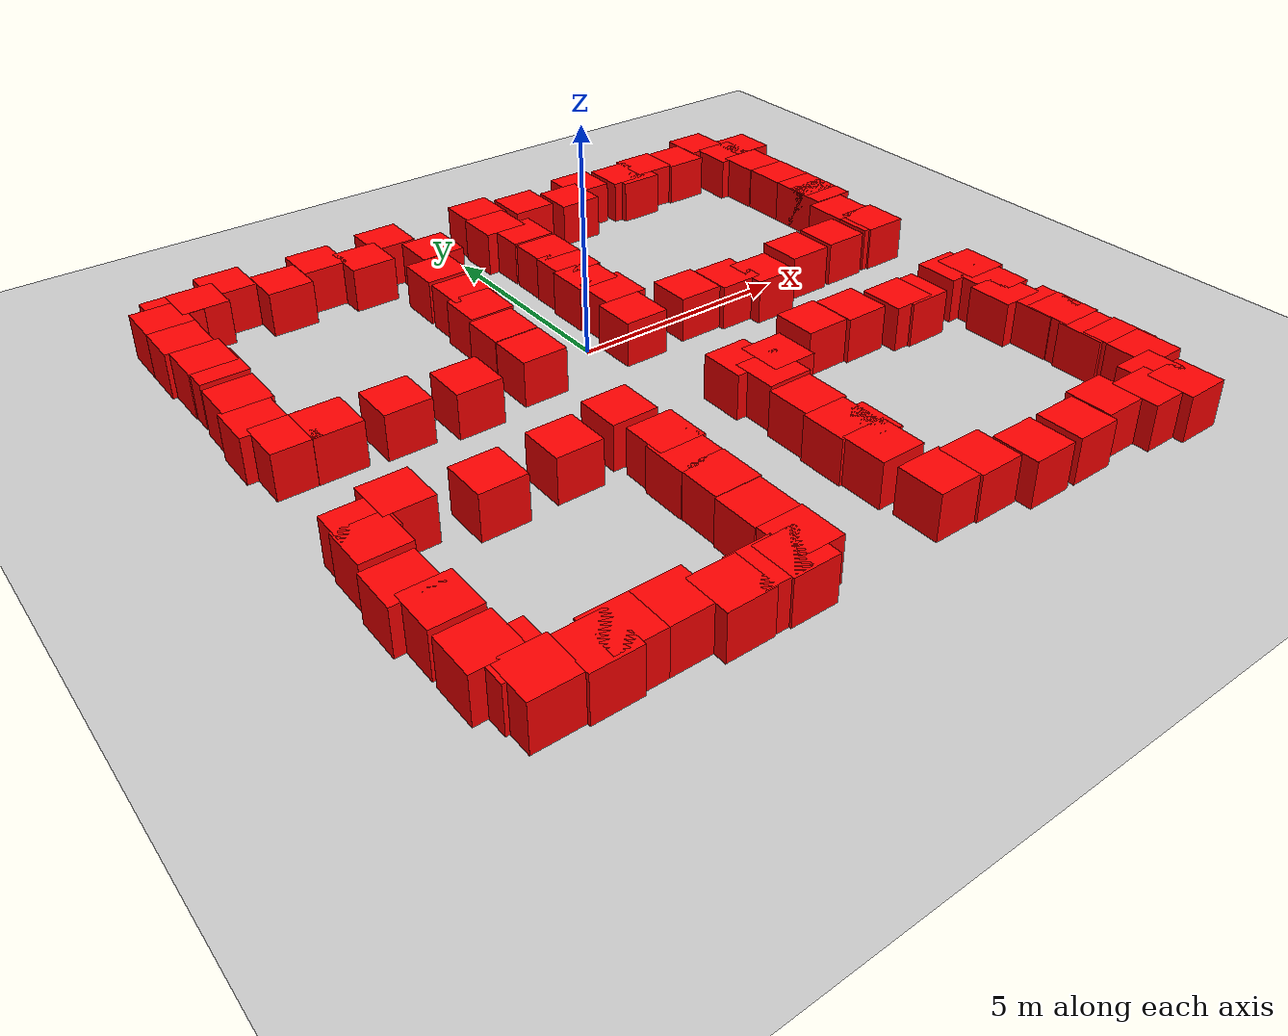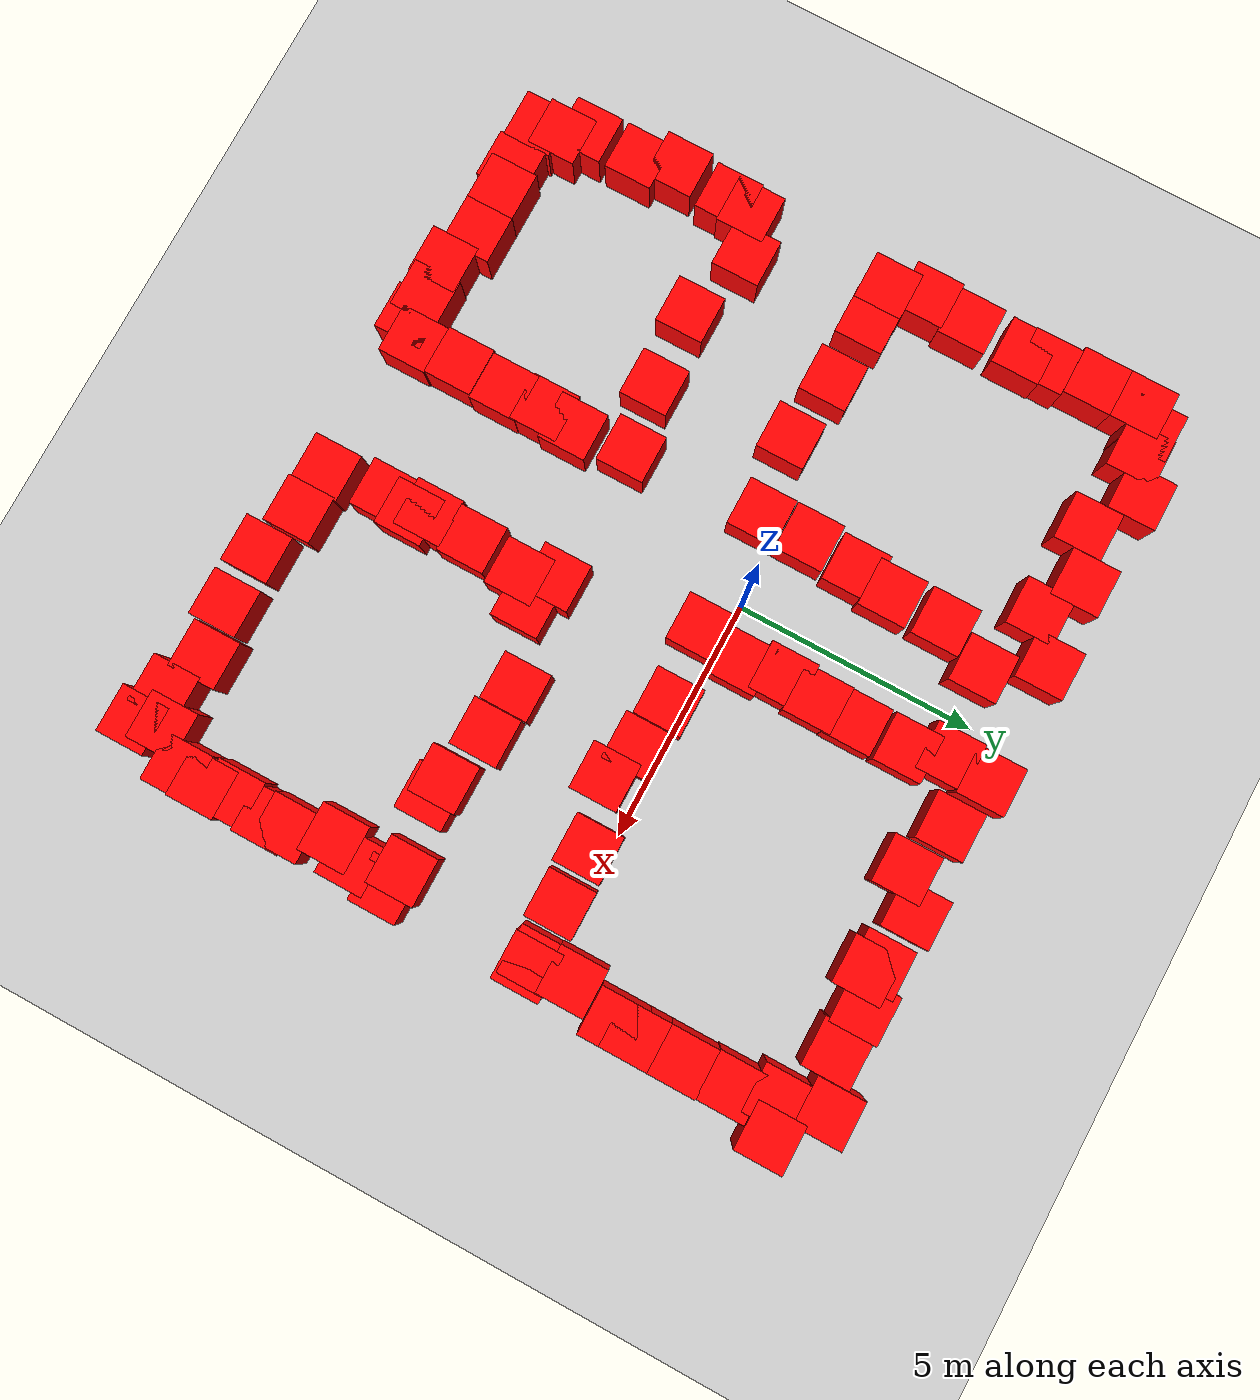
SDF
<sdf version="1.7">
 <world name="default">
  <model name="ground_plane">
   <static>1</static>
   <link name="link">
    <collision name="collision">
     <geometry><plane><normal>0 0 1</normal><size>100 100</size></plane></geometry>
     <surface><friction><ode><mu>100</mu><mu2>50</mu2></ode></friction></surface>
    </collision>
    <visual name="visual">
     <cast_shadows>0</cast_shadows>
     <geometry><plane><normal>0 0 1</normal><size>100 100</size></plane></geometry>
     <material>
      <script><uri>file://media/materials/scripts/gazebo.material</uri><name>Gazebo/Grey</name></script>
     </material>
    </visual>
   </link>
  </model>
  <light name="sun" type="directional">
   <pose>0 0 10 0 -0 0</pose>
   <diffuse>0.8 0.8 0.8 1</diffuse>
   <specular>0.2 0.2 0.2 1</specular>
   <attenuation>
    <range>1000</range>
    <constant>0.9</constant>
    <linear>0.01</linear>
    <quadratic>0.001</quadratic>
   </attenuation>
   <direction>-0.5 0.1 -0.9</direction>
   <spot><inner_angle>0</inner_angle><outer_angle>0</outer_angle><falloff>0</falloff></spot>
  </light>
  <spherical_coordinates>
   <surface_model>EARTH_WGS84</surface_model>
   <latitude_deg>35.1595</latitude_deg>
   <longitude_deg>126.853</longitude_deg>
   <elevation>50</elevation>
   <heading_deg>0</heading_deg>
  </spherical_coordinates>
  <gravity>0 0 -9.8</gravity>
  <magnetic_field>6e-06 2.3e-05 -4.2e-05</magnetic_field>
  <atmosphere type="adiabatic"/>
  <physics type="ode">
   <max_step_size>0.001</max_step_size>
   <real_time_factor>1</real_time_factor>
   <real_time_update_rate>1000</real_time_update_rate>
  </physics>
  <scene><ambient>0.4 0.4 0.4 1</ambient><background>0.7 0.7 0.7 1</background><shadows>1</shadows></scene>
  <audio><device>default</device></audio>
  <model name="unit_box">
   <link name="link">
    <inertial>
     <mass>1</mass>
     <inertia>
      <ixx>0.166667</ixx>
      <ixy>0</ixy>
      <ixz>0</ixz>
      <iyy>0.166667</iyy>
      <iyz>0</iyz>
      <izz>0.166667</izz>
     </inertia>
    </inertial>
    <visual name="visual">
     <geometry><box><size>1 1 1</size></box></geometry>
     <material>
      <script><name>Gazebo/Grey</name><uri>file://media/materials/scripts/gazebo.material</uri></script>
      <shader type="pixel"><normal_map>__default__</normal_map></shader>
      <ambient>1 0 0 0</ambient>
      <diffuse>0.7 0.7 0.7 1</diffuse>
      <specular>0.01 0.01 0.01 1</specular>
      <emissive>0 0 0 1</emissive>
     </material>
    </visual>
    <collision name="collision">
     <geometry><box><size>1 1 1</size></box></geometry>
     <surface>
      <friction>
       <ode><mu>1</mu><mu2>1</mu2><fdir1>0 0 0</fdir1><slip1>0</slip1><slip2>0</slip2></ode>
       <torsional>
        <coefficient>1</coefficient>
        <patch_radius>0</patch_radius>
        <surface_radius>0</surface_radius>
        <use_patch_radius>1</use_patch_radius>
        <ode><slip>0</slip></ode>
       </torsional>
      </friction>
      <bounce><restitution_coefficient>0</restitution_coefficient><threshold>1e+06</threshold></bounce>
      <contact>
       <collide_without_contact>0</collide_without_contact>
       <collide_without_contact_bitmask>1</collide_without_contact_bitmask>
       <collide_bitmask>1</collide_bitmask>
       <ode>
        <soft_cfm>0</soft_cfm>
        <soft_erp>0.2</soft_erp>
        <kp>1e+13</kp>
        <kd>1</kd>
        <max_vel>0.01</max_vel>
        <min_depth>0</min_depth>
       </ode>
       <bullet>
        <split_impulse>1</split_impulse>
        <split_impulse_penetration_threshold>-0.01</split_impulse_penetration_threshold>
        <soft_cfm>0</soft_cfm>
        <soft_erp>0.2</soft_erp>
        <kp>1e+13</kp>
        <kd>1</kd>
       </bullet>
      </contact>
     </surface>
    </collision>
   </link>
   <static>0</static>
   <pose>0.827845 -0.466795 0.5 0 -0 0</pose>
  </model>
  <model name="unit_box_clone">
   <link name="link">
    <inertial>
     <mass>1</mass>
     <inertia>
      <ixx>0.166667</ixx>
      <ixy>0</ixy>
      <ixz>0</ixz>
      <iyy>0.166667</iyy>
      <iyz>0</iyz>
      <izz>0.166667</izz>
     </inertia>
    </inertial>
    <visual name="visual">
     <geometry><box><size>1 1 1</size></box></geometry>
     <material>
      <script><name>Gazebo/Grey</name><uri>file://media/materials/scripts/gazebo.material</uri></script>
      <shader type="pixel"><normal_map>__default__</normal_map></shader>
      <ambient>1 0 0 0</ambient>
      <diffuse>0.7 0.7 0.7 1</diffuse>
      <specular>0.01 0.01 0.01 1</specular>
      <emissive>0 0 0 1</emissive>
     </material>
    </visual>
    <collision name="collision">
     <geometry><box><size>1 1 1</size></box></geometry>
     <surface>
      <friction>
       <ode><mu>1</mu><mu2>1</mu2><fdir1>0 0 0</fdir1><slip1>0</slip1><slip2>0</slip2></ode>
       <torsional>
        <coefficient>1</coefficient>
        <patch_radius>0</patch_radius>
        <surface_radius>0</surface_radius>
        <use_patch_radius>1</use_patch_radius>
        <ode><slip>0</slip></ode>
       </torsional>
      </friction>
      <bounce><restitution_coefficient>0</restitution_coefficient><threshold>1e+06</threshold></bounce>
      <contact>
       <collide_without_contact>0</collide_without_contact>
       <collide_without_contact_bitmask>1</collide_without_contact_bitmask>
       <collide_bitmask>1</collide_bitmask>
       <ode>
        <soft_cfm>0</soft_cfm>
        <soft_erp>0.2</soft_erp>
        <kp>1e+13</kp>
        <kd>1</kd>
        <max_vel>0.01</max_vel>
        <min_depth>0</min_depth>
       </ode>
       <bullet>
        <split_impulse>1</split_impulse>
        <split_impulse_penetration_threshold>-0.01</split_impulse_penetration_threshold>
        <soft_cfm>0</soft_cfm>
        <soft_erp>0.2</soft_erp>
        <kp>1e+13</kp>
        <kd>1</kd>
       </bullet>
      </contact>
     </surface>
    </collision>
   </link>
   <static>0</static>
   <pose>7.86867 -0.323281 0.5 0 -0 0</pose>
  </model>
  <model name="unit_box_clone_clone">
   <link name="link">
    <inertial>
     <mass>1</mass>
     <inertia>
      <ixx>0.166667</ixx>
      <ixy>0</ixy>
      <ixz>0</ixz>
      <iyy>0.166667</iyy>
      <iyz>0</iyz>
      <izz>0.166667</izz>
     </inertia>
    </inertial>
    <visual name="visual">
     <geometry><box><size>1 1 1</size></box></geometry>
     <material>
      <script><name>Gazebo/Grey</name><uri>file://media/materials/scripts/gazebo.material</uri></script>
      <shader type="pixel"><normal_map>__default__</normal_map></shader>
      <ambient>1 0 0 0</ambient>
      <diffuse>0.7 0.7 0.7 1</diffuse>
      <specular>0.01 0.01 0.01 1</specular>
      <emissive>0 0 0 1</emissive>
     </material>
    </visual>
    <collision name="collision">
     <geometry><box><size>1 1 1</size></box></geometry>
     <surface>
      <friction>
       <ode><mu>1</mu><mu2>1</mu2><fdir1>0 0 0</fdir1><slip1>0</slip1><slip2>0</slip2></ode>
       <torsional>
        <coefficient>1</coefficient>
        <patch_radius>0</patch_radius>
        <surface_radius>0</surface_radius>
        <use_patch_radius>1</use_patch_radius>
        <ode><slip>0</slip></ode>
       </torsional>
      </friction>
      <bounce><restitution_coefficient>0</restitution_coefficient><threshold>1e+06</threshold></bounce>
      <contact>
       <collide_without_contact>0</collide_without_contact>
       <collide_without_contact_bitmask>1</collide_without_contact_bitmask>
       <collide_bitmask>1</collide_bitmask>
       <ode>
        <soft_cfm>0</soft_cfm>
        <soft_erp>0.2</soft_erp>
        <kp>1e+13</kp>
        <kd>1</kd>
        <max_vel>0.01</max_vel>
        <min_depth>0</min_depth>
       </ode>
       <bullet>
        <split_impulse>1</split_impulse>
        <split_impulse_penetration_threshold>-0.01</split_impulse_penetration_threshold>
        <soft_cfm>0</soft_cfm>
        <soft_erp>0.2</soft_erp>
        <kp>1e+13</kp>
        <kd>1</kd>
       </bullet>
      </contact>
     </surface>
    </collision>
   </link>
   <static>0</static>
   <pose>7.54908 5.74957 0.5 0 -0 0</pose>
  </model>
  <model name="unit_box_clone_clone_0">
   <link name="link">
    <inertial>
     <mass>1</mass>
     <inertia>
      <ixx>0.166667</ixx>
      <ixy>0</ixy>
      <ixz>0</ixz>
      <iyy>0.166667</iyy>
      <iyz>0</iyz>
      <izz>0.166667</izz>
     </inertia>
    </inertial>
    <visual name="visual">
     <geometry><box><size>1 1 1</size></box></geometry>
     <material>
      <script><name>Gazebo/Grey</name><uri>file://media/materials/scripts/gazebo.material</uri></script>
      <shader type="pixel"><normal_map>__default__</normal_map></shader>
      <ambient>1 0 0 0</ambient>
      <diffuse>0.7 0.7 0.7 1</diffuse>
      <specular>0.01 0.01 0.01 1</specular>
      <emissive>0 0 0 1</emissive>
     </material>
    </visual>
    <collision name="collision">
     <geometry><box><size>1 1 1</size></box></geometry>
     <surface>
      <friction>
       <ode><mu>1</mu><mu2>1</mu2><fdir1>0 0 0</fdir1><slip1>0</slip1><slip2>0</slip2></ode>
       <torsional>
        <coefficient>1</coefficient>
        <patch_radius>0</patch_radius>
        <surface_radius>0</surface_radius>
        <use_patch_radius>1</use_patch_radius>
        <ode><slip>0</slip></ode>
       </torsional>
      </friction>
      <bounce><restitution_coefficient>0</restitution_coefficient><threshold>1e+06</threshold></bounce>
      <contact>
       <collide_without_contact>0</collide_without_contact>
       <collide_without_contact_bitmask>1</collide_without_contact_bitmask>
       <collide_bitmask>1</collide_bitmask>
       <ode>
        <soft_cfm>0</soft_cfm>
        <soft_erp>0.2</soft_erp>
        <kp>1e+13</kp>
        <kd>1</kd>
        <max_vel>0.01</max_vel>
        <min_depth>0</min_depth>
       </ode>
       <bullet>
        <split_impulse>1</split_impulse>
        <split_impulse_penetration_threshold>-0.01</split_impulse_penetration_threshold>
        <soft_cfm>0</soft_cfm>
        <soft_erp>0.2</soft_erp>
        <kp>1e+13</kp>
        <kd>1</kd>
       </bullet>
      </contact>
     </surface>
    </collision>
   </link>
   <static>0</static>
   <pose>0.811864 5.64086 0.5 0 -0 0</pose>
  </model>
  <model name="unit_box_clone_clone_1">
   <link name="link">
    <inertial>
     <mass>1</mass>
     <inertia>
      <ixx>0.166667</ixx>
      <ixy>0</ixy>
      <ixz>0</ixz>
      <iyy>0.166667</iyy>
      <iyz>0</iyz>
      <izz>0.166667</izz>
     </inertia>
    </inertial>
    <visual name="visual">
     <geometry><box><size>1 1 1</size></box></geometry>
     <material>
      <script><name>Gazebo/Grey</name><uri>file://media/materials/scripts/gazebo.material</uri></script>
      <shader type="pixel"><normal_map>__default__</normal_map></shader>
      <ambient>1 0 0 0</ambient>
      <diffuse>0.7 0.7 0.7 1</diffuse>
      <specular>0.01 0.01 0.01 1</specular>
      <emissive>0 0 0 1</emissive>
     </material>
    </visual>
    <collision name="collision">
     <geometry><box><size>1 1 1</size></box></geometry>
     <surface>
      <friction>
       <ode><mu>1</mu><mu2>1</mu2><fdir1>0 0 0</fdir1><slip1>0</slip1><slip2>0</slip2></ode>
       <torsional>
        <coefficient>1</coefficient>
        <patch_radius>0</patch_radius>
        <surface_radius>0</surface_radius>
        <use_patch_radius>1</use_patch_radius>
        <ode><slip>0</slip></ode>
       </torsional>
      </friction>
      <bounce><restitution_coefficient>0</restitution_coefficient><threshold>1e+06</threshold></bounce>
      <contact>
       <collide_without_contact>0</collide_without_contact>
       <collide_without_contact_bitmask>1</collide_without_contact_bitmask>
       <collide_bitmask>1</collide_bitmask>
       <ode>
        <soft_cfm>0</soft_cfm>
        <soft_erp>0.2</soft_erp>
        <kp>1e+13</kp>
        <kd>1</kd>
        <max_vel>0.01</max_vel>
        <min_depth>0</min_depth>
       </ode>
       <bullet>
        <split_impulse>1</split_impulse>
        <split_impulse_penetration_threshold>-0.01</split_impulse_penetration_threshold>
        <soft_cfm>0</soft_cfm>
        <soft_erp>0.2</soft_erp>
        <kp>1e+13</kp>
        <kd>1</kd>
       </bullet>
      </contact>
     </surface>
    </collision>
   </link>
   <static>0</static>
   <pose>-5.37844 5.74394 0.5 0 -0 0</pose>
  </model>
  <model name="unit_box_clone_clone_2">
   <link name="link">
    <inertial>
     <mass>1</mass>
     <inertia>
      <ixx>0.166667</ixx>
      <ixy>0</ixy>
      <ixz>0</ixz>
      <iyy>0.166667</iyy>
      <iyz>0</iyz>
      <izz>0.166667</izz>
     </inertia>
    </inertial>
    <visual name="visual">
     <geometry><box><size>1 1 1</size></box></geometry>
     <material>
      <script><name>Gazebo/Grey</name><uri>file://media/materials/scripts/gazebo.material</uri></script>
      <shader type="pixel"><normal_map>__default__</normal_map></shader>
      <ambient>1 0 0 0</ambient>
      <diffuse>0.7 0.7 0.7 1</diffuse>
      <specular>0.01 0.01 0.01 1</specular>
      <emissive>0 0 0 1</emissive>
     </material>
    </visual>
    <collision name="collision">
     <geometry><box><size>1 1 1</size></box></geometry>
     <surface>
      <friction>
       <ode><mu>1</mu><mu2>1</mu2><fdir1>0 0 0</fdir1><slip1>0</slip1><slip2>0</slip2></ode>
       <torsional>
        <coefficient>1</coefficient>
        <patch_radius>0</patch_radius>
        <surface_radius>0</surface_radius>
        <use_patch_radius>1</use_patch_radius>
        <ode><slip>0</slip></ode>
       </torsional>
      </friction>
      <bounce><restitution_coefficient>0</restitution_coefficient><threshold>1e+06</threshold></bounce>
      <contact>
       <collide_without_contact>0</collide_without_contact>
       <collide_without_contact_bitmask>1</collide_without_contact_bitmask>
       <collide_bitmask>1</collide_bitmask>
       <ode>
        <soft_cfm>0</soft_cfm>
        <soft_erp>0.2</soft_erp>
        <kp>1e+13</kp>
        <kd>1</kd>
        <max_vel>0.01</max_vel>
        <min_depth>0</min_depth>
       </ode>
       <bullet>
        <split_impulse>1</split_impulse>
        <split_impulse_penetration_threshold>-0.01</split_impulse_penetration_threshold>
        <soft_cfm>0</soft_cfm>
        <soft_erp>0.2</soft_erp>
        <kp>1e+13</kp>
        <kd>1</kd>
       </bullet>
      </contact>
     </surface>
    </collision>
   </link>
   <static>0</static>
   <pose>-1.64328 5.63469 0.5 0 -0 0</pose>
  </model>
  <model name="unit_box_clone_clone_3">
   <link name="link">
    <inertial>
     <mass>1</mass>
     <inertia>
      <ixx>0.166667</ixx>
      <ixy>0</ixy>
      <ixz>0</ixz>
      <iyy>0.166667</iyy>
      <iyz>0</iyz>
      <izz>0.166667</izz>
     </inertia>
    </inertial>
    <visual name="visual">
     <geometry><box><size>1 1 1</size></box></geometry>
     <material>
      <script><name>Gazebo/Grey</name><uri>file://media/materials/scripts/gazebo.material</uri></script>
      <shader type="pixel"><normal_map>__default__</normal_map></shader>
      <ambient>1 0 0 0</ambient>
      <diffuse>0.7 0.7 0.7 1</diffuse>
      <specular>0.01 0.01 0.01 1</specular>
      <emissive>0 0 0 1</emissive>
     </material>
    </visual>
    <collision name="collision">
     <geometry><box><size>1 1 1</size></box></geometry>
     <surface>
      <friction>
       <ode><mu>1</mu><mu2>1</mu2><fdir1>0 0 0</fdir1><slip1>0</slip1><slip2>0</slip2></ode>
       <torsional>
        <coefficient>1</coefficient>
        <patch_radius>0</patch_radius>
        <surface_radius>0</surface_radius>
        <use_patch_radius>1</use_patch_radius>
        <ode><slip>0</slip></ode>
       </torsional>
      </friction>
      <bounce><restitution_coefficient>0</restitution_coefficient><threshold>1e+06</threshold></bounce>
      <contact>
       <collide_without_contact>0</collide_without_contact>
       <collide_without_contact_bitmask>1</collide_without_contact_bitmask>
       <collide_bitmask>1</collide_bitmask>
       <ode>
        <soft_cfm>0</soft_cfm>
        <soft_erp>0.2</soft_erp>
        <kp>1e+13</kp>
        <kd>1</kd>
        <max_vel>0.01</max_vel>
        <min_depth>0</min_depth>
       </ode>
       <bullet>
        <split_impulse>1</split_impulse>
        <split_impulse_penetration_threshold>-0.01</split_impulse_penetration_threshold>
        <soft_cfm>0</soft_cfm>
        <soft_erp>0.2</soft_erp>
        <kp>1e+13</kp>
        <kd>1</kd>
       </bullet>
      </contact>
     </surface>
    </collision>
   </link>
   <static>0</static>
   <pose>-1.6664 -0.488777 0.5 0 -0 0</pose>
  </model>
  <model name="unit_box_clone_clone_4">
   <link name="link">
    <inertial>
     <mass>1</mass>
     <inertia>
      <ixx>0.166667</ixx>
      <ixy>0</ixy>
      <ixz>0</ixz>
      <iyy>0.166667</iyy>
      <iyz>0</iyz>
      <izz>0.166667</izz>
     </inertia>
    </inertial>
    <visual name="visual">
     <geometry><box><size>1 1 1</size></box></geometry>
     <material>
      <script><name>Gazebo/Grey</name><uri>file://media/materials/scripts/gazebo.material</uri></script>
      <shader type="pixel"><normal_map>__default__</normal_map></shader>
      <ambient>1 0 0 0</ambient>
      <diffuse>0.7 0.7 0.7 1</diffuse>
      <specular>0.01 0.01 0.01 1</specular>
      <emissive>0 0 0 1</emissive>
     </material>
    </visual>
    <collision name="collision">
     <geometry><box><size>1 1 1</size></box></geometry>
     <surface>
      <friction>
       <ode><mu>1</mu><mu2>1</mu2><fdir1>0 0 0</fdir1><slip1>0</slip1><slip2>0</slip2></ode>
       <torsional>
        <coefficient>1</coefficient>
        <patch_radius>0</patch_radius>
        <surface_radius>0</surface_radius>
        <use_patch_radius>1</use_patch_radius>
        <ode><slip>0</slip></ode>
       </torsional>
      </friction>
      <bounce><restitution_coefficient>0</restitution_coefficient><threshold>1e+06</threshold></bounce>
      <contact>
       <collide_without_contact>0</collide_without_contact>
       <collide_without_contact_bitmask>1</collide_without_contact_bitmask>
       <collide_bitmask>1</collide_bitmask>
       <ode>
        <soft_cfm>0</soft_cfm>
        <soft_erp>0.2</soft_erp>
        <kp>1e+13</kp>
        <kd>1</kd>
        <max_vel>0.01</max_vel>
        <min_depth>0</min_depth>
       </ode>
       <bullet>
        <split_impulse>1</split_impulse>
        <split_impulse_penetration_threshold>-0.01</split_impulse_penetration_threshold>
        <soft_cfm>0</soft_cfm>
        <soft_erp>0.2</soft_erp>
        <kp>1e+13</kp>
        <kd>1</kd>
       </bullet>
      </contact>
     </surface>
    </collision>
   </link>
   <static>0</static>
   <pose>-5.98599 -0.419497 0.5 0 -0 0</pose>
  </model>
  <model name="unit_box_clone_clone_5">
   <link name="link">
    <inertial>
     <mass>1</mass>
     <inertia>
      <ixx>0.166667</ixx>
      <ixy>0</ixy>
      <ixz>0</ixz>
      <iyy>0.166667</iyy>
      <iyz>0</iyz>
      <izz>0.166667</izz>
     </inertia>
    </inertial>
    <visual name="visual">
     <geometry><box><size>1 1 1</size></box></geometry>
     <material>
      <script><name>Gazebo/Grey</name><uri>file://media/materials/scripts/gazebo.material</uri></script>
      <shader type="pixel"><normal_map>__default__</normal_map></shader>
      <ambient>1 0 0 0</ambient>
      <diffuse>0.7 0.7 0.7 1</diffuse>
      <specular>0.01 0.01 0.01 1</specular>
      <emissive>0 0 0 1</emissive>
     </material>
    </visual>
    <collision name="collision">
     <geometry><box><size>1 1 1</size></box></geometry>
     <surface>
      <friction>
       <ode><mu>1</mu><mu2>1</mu2><fdir1>0 0 0</fdir1><slip1>0</slip1><slip2>0</slip2></ode>
       <torsional>
        <coefficient>1</coefficient>
        <patch_radius>0</patch_radius>
        <surface_radius>0</surface_radius>
        <use_patch_radius>1</use_patch_radius>
        <ode><slip>0</slip></ode>
       </torsional>
      </friction>
      <bounce><restitution_coefficient>0</restitution_coefficient><threshold>1e+06</threshold></bounce>
      <contact>
       <collide_without_contact>0</collide_without_contact>
       <collide_without_contact_bitmask>1</collide_without_contact_bitmask>
       <collide_bitmask>1</collide_bitmask>
       <ode>
        <soft_cfm>0</soft_cfm>
        <soft_erp>0.2</soft_erp>
        <kp>1e+13</kp>
        <kd>1</kd>
        <max_vel>0.01</max_vel>
        <min_depth>0</min_depth>
       </ode>
       <bullet>
        <split_impulse>1</split_impulse>
        <split_impulse_penetration_threshold>-0.01</split_impulse_penetration_threshold>
        <soft_cfm>0</soft_cfm>
        <soft_erp>0.2</soft_erp>
        <kp>1e+13</kp>
        <kd>1</kd>
       </bullet>
      </contact>
     </surface>
    </collision>
   </link>
   <static>0</static>
   <pose>-6.06718 -3.15279 0.5 0 -0 0</pose>
  </model>
  <model name="unit_box_clone_clone_6">
   <link name="link">
    <inertial>
     <mass>1</mass>
     <inertia>
      <ixx>0.166667</ixx>
      <ixy>0</ixy>
      <ixz>0</ixz>
      <iyy>0.166667</iyy>
      <iyz>0</iyz>
      <izz>0.166667</izz>
     </inertia>
    </inertial>
    <visual name="visual">
     <geometry><box><size>1 1 1</size></box></geometry>
     <material>
      <script><name>Gazebo/Grey</name><uri>file://media/materials/scripts/gazebo.material</uri></script>
      <shader type="pixel"><normal_map>__default__</normal_map></shader>
      <ambient>1 0 0 0</ambient>
      <diffuse>0.7 0.7 0.7 1</diffuse>
      <specular>0.01 0.01 0.01 1</specular>
      <emissive>0 0 0 1</emissive>
     </material>
    </visual>
    <collision name="collision">
     <geometry><box><size>1 1 1</size></box></geometry>
     <surface>
      <friction>
       <ode><mu>1</mu><mu2>1</mu2><fdir1>0 0 0</fdir1><slip1>0</slip1><slip2>0</slip2></ode>
       <torsional>
        <coefficient>1</coefficient>
        <patch_radius>0</patch_radius>
        <surface_radius>0</surface_radius>
        <use_patch_radius>1</use_patch_radius>
        <ode><slip>0</slip></ode>
       </torsional>
      </friction>
      <bounce><restitution_coefficient>0</restitution_coefficient><threshold>1e+06</threshold></bounce>
      <contact>
       <collide_without_contact>0</collide_without_contact>
       <collide_without_contact_bitmask>1</collide_without_contact_bitmask>
       <collide_bitmask>1</collide_bitmask>
       <ode>
        <soft_cfm>0</soft_cfm>
        <soft_erp>0.2</soft_erp>
        <kp>1e+13</kp>
        <kd>1</kd>
        <max_vel>0.01</max_vel>
        <min_depth>0</min_depth>
       </ode>
       <bullet>
        <split_impulse>1</split_impulse>
        <split_impulse_penetration_threshold>-0.01</split_impulse_penetration_threshold>
        <soft_cfm>0</soft_cfm>
        <soft_erp>0.2</soft_erp>
        <kp>1e+13</kp>
        <kd>1</kd>
       </bullet>
      </contact>
     </surface>
    </collision>
   </link>
   <static>0</static>
   <pose>-1.57543 -3.27153 0.5 0 -0 0</pose>
  </model>
  <model name="unit_box_clone_clone_7">
   <link name="link">
    <inertial>
     <mass>1</mass>
     <inertia>
      <ixx>0.166667</ixx>
      <ixy>0</ixy>
      <ixz>0</ixz>
      <iyy>0.166667</iyy>
      <iyz>0</iyz>
      <izz>0.166667</izz>
     </inertia>
    </inertial>
    <visual name="visual">
     <geometry><box><size>1 1 1</size></box></geometry>
     <material>
      <script><name>Gazebo/Grey</name><uri>file://media/materials/scripts/gazebo.material</uri></script>
      <shader type="pixel"><normal_map>__default__</normal_map></shader>
      <ambient>1 0 0 0</ambient>
      <diffuse>0.7 0.7 0.7 1</diffuse>
      <specular>0.01 0.01 0.01 1</specular>
      <emissive>0 0 0 1</emissive>
     </material>
    </visual>
    <collision name="collision">
     <geometry><box><size>1 1 1</size></box></geometry>
     <surface>
      <friction>
       <ode><mu>1</mu><mu2>1</mu2><fdir1>0 0 0</fdir1><slip1>0</slip1><slip2>0</slip2></ode>
       <torsional>
        <coefficient>1</coefficient>
        <patch_radius>0</patch_radius>
        <surface_radius>0</surface_radius>
        <use_patch_radius>1</use_patch_radius>
        <ode><slip>0</slip></ode>
       </torsional>
      </friction>
      <bounce><restitution_coefficient>0</restitution_coefficient><threshold>1e+06</threshold></bounce>
      <contact>
       <collide_without_contact>0</collide_without_contact>
       <collide_without_contact_bitmask>1</collide_without_contact_bitmask>
       <collide_bitmask>1</collide_bitmask>
       <ode>
        <soft_cfm>0</soft_cfm>
        <soft_erp>0.2</soft_erp>
        <kp>1e+13</kp>
        <kd>1</kd>
        <max_vel>0.01</max_vel>
        <min_depth>0</min_depth>
       </ode>
       <bullet>
        <split_impulse>1</split_impulse>
        <split_impulse_penetration_threshold>-0.01</split_impulse_penetration_threshold>
        <soft_cfm>0</soft_cfm>
        <soft_erp>0.2</soft_erp>
        <kp>1e+13</kp>
        <kd>1</kd>
       </bullet>
      </contact>
     </surface>
    </collision>
   </link>
   <static>0</static>
   <pose>1.29425 -3.3393 0.5 0 -0 0</pose>
  </model>
  <model name="unit_box_clone_clone_8">
   <link name="link">
    <inertial>
     <mass>1</mass>
     <inertia>
      <ixx>0.166667</ixx>
      <ixy>0</ixy>
      <ixz>0</ixz>
      <iyy>0.166667</iyy>
      <iyz>0</iyz>
      <izz>0.166667</izz>
     </inertia>
    </inertial>
    <visual name="visual">
     <geometry><box><size>1 1 1</size></box></geometry>
     <material>
      <script><name>Gazebo/Grey</name><uri>file://media/materials/scripts/gazebo.material</uri></script>
      <shader type="pixel"><normal_map>__default__</normal_map></shader>
      <ambient>1 0 0 0</ambient>
      <diffuse>0.7 0.7 0.7 1</diffuse>
      <specular>0.01 0.01 0.01 1</specular>
      <emissive>0 0 0 1</emissive>
     </material>
    </visual>
    <collision name="collision">
     <geometry><box><size>1 1 1</size></box></geometry>
     <surface>
      <friction>
       <ode><mu>1</mu><mu2>1</mu2><fdir1>0 0 0</fdir1><slip1>0</slip1><slip2>0</slip2></ode>
       <torsional>
        <coefficient>1</coefficient>
        <patch_radius>0</patch_radius>
        <surface_radius>0</surface_radius>
        <use_patch_radius>1</use_patch_radius>
        <ode><slip>0</slip></ode>
       </torsional>
      </friction>
      <bounce><restitution_coefficient>0</restitution_coefficient><threshold>1e+06</threshold></bounce>
      <contact>
       <collide_without_contact>0</collide_without_contact>
       <collide_without_contact_bitmask>1</collide_without_contact_bitmask>
       <collide_bitmask>1</collide_bitmask>
       <ode>
        <soft_cfm>0</soft_cfm>
        <soft_erp>0.2</soft_erp>
        <kp>1e+13</kp>
        <kd>1</kd>
        <max_vel>0.01</max_vel>
        <min_depth>0</min_depth>
       </ode>
       <bullet>
        <split_impulse>1</split_impulse>
        <split_impulse_penetration_threshold>-0.01</split_impulse_penetration_threshold>
        <soft_cfm>0</soft_cfm>
        <soft_erp>0.2</soft_erp>
        <kp>1e+13</kp>
        <kd>1</kd>
       </bullet>
      </contact>
     </surface>
    </collision>
   </link>
   <static>0</static>
   <pose>7.88438 -3.32843 0.5 0 -0 0</pose>
  </model>
  <model name="unit_box_clone_clone_9">
   <link name="link">
    <inertial>
     <mass>1</mass>
     <inertia>
      <ixx>0.166667</ixx>
      <ixy>0</ixy>
      <ixz>0</ixz>
      <iyy>0.166667</iyy>
      <iyz>0</iyz>
      <izz>0.166667</izz>
     </inertia>
    </inertial>
    <visual name="visual">
     <geometry><box><size>1 1 1</size></box></geometry>
     <material>
      <script><name>Gazebo/Grey</name><uri>file://media/materials/scripts/gazebo.material</uri></script>
      <shader type="pixel"><normal_map>__default__</normal_map></shader>
      <ambient>1 0 0 0</ambient>
      <diffuse>0.7 0.7 0.7 1</diffuse>
      <specular>0.01 0.01 0.01 1</specular>
      <emissive>0 0 0 1</emissive>
     </material>
    </visual>
    <collision name="collision">
     <geometry><box><size>1 1 1</size></box></geometry>
     <surface>
      <friction>
       <ode><mu>1</mu><mu2>1</mu2><fdir1>0 0 0</fdir1><slip1>0</slip1><slip2>0</slip2></ode>
       <torsional>
        <coefficient>1</coefficient>
        <patch_radius>0</patch_radius>
        <surface_radius>0</surface_radius>
        <use_patch_radius>1</use_patch_radius>
        <ode><slip>0</slip></ode>
       </torsional>
      </friction>
      <bounce><restitution_coefficient>0</restitution_coefficient><threshold>1e+06</threshold></bounce>
      <contact>
       <collide_without_contact>0</collide_without_contact>
       <collide_without_contact_bitmask>1</collide_without_contact_bitmask>
       <collide_bitmask>1</collide_bitmask>
       <ode>
        <soft_cfm>0</soft_cfm>
        <soft_erp>0.2</soft_erp>
        <kp>1e+13</kp>
        <kd>1</kd>
        <max_vel>0.01</max_vel>
        <min_depth>0</min_depth>
       </ode>
       <bullet>
        <split_impulse>1</split_impulse>
        <split_impulse_penetration_threshold>-0.01</split_impulse_penetration_threshold>
        <soft_cfm>0</soft_cfm>
        <soft_erp>0.2</soft_erp>
        <kp>1e+13</kp>
        <kd>1</kd>
       </bullet>
      </contact>
     </surface>
    </collision>
   </link>
   <static>0</static>
   <pose>1.41007 -5.09495 0.5 0 -0 0</pose>
  </model>
  <model name="unit_box_clone_clone_10">
   <link name="link">
    <inertial>
     <mass>1</mass>
     <inertia>
      <ixx>0.166667</ixx>
      <ixy>0</ixy>
      <ixz>0</ixz>
      <iyy>0.166667</iyy>
      <iyz>0</iyz>
      <izz>0.166667</izz>
     </inertia>
    </inertial>
    <visual name="visual">
     <geometry><box><size>1 1 1</size></box></geometry>
     <material>
      <script><name>Gazebo/Grey</name><uri>file://media/materials/scripts/gazebo.material</uri></script>
      <shader type="pixel"><normal_map>__default__</normal_map></shader>
      <ambient>1 0 0 0</ambient>
      <diffuse>0.7 0.7 0.7 1</diffuse>
      <specular>0.01 0.01 0.01 1</specular>
      <emissive>0 0 0 1</emissive>
     </material>
    </visual>
    <collision name="collision">
     <geometry><box><size>1 1 1</size></box></geometry>
     <surface>
      <friction>
       <ode><mu>1</mu><mu2>1</mu2><fdir1>0 0 0</fdir1><slip1>0</slip1><slip2>0</slip2></ode>
       <torsional>
        <coefficient>1</coefficient>
        <patch_radius>0</patch_radius>
        <surface_radius>0</surface_radius>
        <use_patch_radius>1</use_patch_radius>
        <ode><slip>0</slip></ode>
       </torsional>
      </friction>
      <bounce><restitution_coefficient>0</restitution_coefficient><threshold>1e+06</threshold></bounce>
      <contact>
       <collide_without_contact>0</collide_without_contact>
       <collide_without_contact_bitmask>1</collide_without_contact_bitmask>
       <collide_bitmask>1</collide_bitmask>
       <ode>
        <soft_cfm>0</soft_cfm>
        <soft_erp>0.2</soft_erp>
        <kp>1e+13</kp>
        <kd>1</kd>
        <max_vel>0.01</max_vel>
        <min_depth>0</min_depth>
       </ode>
       <bullet>
        <split_impulse>1</split_impulse>
        <split_impulse_penetration_threshold>-0.01</split_impulse_penetration_threshold>
        <soft_cfm>0</soft_cfm>
        <soft_erp>0.2</soft_erp>
        <kp>1e+13</kp>
        <kd>1</kd>
       </bullet>
      </contact>
     </surface>
    </collision>
   </link>
   <static>0</static>
   <pose>1.40868 -7 0.5 0 -0 0</pose>
  </model>
  <model name="unit_box_clone_clone_11">
   <link name="link">
    <inertial>
     <mass>1</mass>
     <inertia>
      <ixx>0.166667</ixx>
      <ixy>0</ixy>
      <ixz>0</ixz>
      <iyy>0.166667</iyy>
      <iyz>0</iyz>
      <izz>0.166667</izz>
     </inertia>
    </inertial>
    <visual name="visual">
     <geometry><box><size>1 1 1</size></box></geometry>
     <material>
      <script><name>Gazebo/Grey</name><uri>file://media/materials/scripts/gazebo.material</uri></script>
      <shader type="pixel"><normal_map>__default__</normal_map></shader>
      <ambient>1 0 0 0</ambient>
      <diffuse>0.7 0.7 0.7 1</diffuse>
      <specular>0.01 0.01 0.01 1</specular>
      <emissive>0 0 0 1</emissive>
     </material>
    </visual>
    <collision name="collision">
     <geometry><box><size>1 1 1</size></box></geometry>
     <surface>
      <friction>
       <ode><mu>1</mu><mu2>1</mu2><fdir1>0 0 0</fdir1><slip1>0</slip1><slip2>0</slip2></ode>
       <torsional>
        <coefficient>1</coefficient>
        <patch_radius>0</patch_radius>
        <surface_radius>0</surface_radius>
        <use_patch_radius>1</use_patch_radius>
        <ode><slip>0</slip></ode>
       </torsional>
      </friction>
      <bounce><restitution_coefficient>0</restitution_coefficient><threshold>1e+06</threshold></bounce>
      <contact>
       <collide_without_contact>0</collide_without_contact>
       <collide_without_contact_bitmask>1</collide_without_contact_bitmask>
       <collide_bitmask>1</collide_bitmask>
       <ode>
        <soft_cfm>0</soft_cfm>
        <soft_erp>0.2</soft_erp>
        <kp>1e+13</kp>
        <kd>1</kd>
        <max_vel>0.01</max_vel>
        <min_depth>0</min_depth>
       </ode>
       <bullet>
        <split_impulse>1</split_impulse>
        <split_impulse_penetration_threshold>-0.01</split_impulse_penetration_threshold>
        <soft_cfm>0</soft_cfm>
        <soft_erp>0.2</soft_erp>
        <kp>1e+13</kp>
        <kd>1</kd>
       </bullet>
      </contact>
     </surface>
    </collision>
   </link>
   <static>0</static>
   <pose>-1.49355 -5.11821 0.5 0 -0 0</pose>
  </model>
  <model name="unit_box_clone_clone_12">
   <link name="link">
    <inertial>
     <mass>1</mass>
     <inertia>
      <ixx>0.166667</ixx>
      <ixy>0</ixy>
      <ixz>0</ixz>
      <iyy>0.166667</iyy>
      <iyz>0</iyz>
      <izz>0.166667</izz>
     </inertia>
    </inertial>
    <visual name="visual">
     <geometry><box><size>1 1 1</size></box></geometry>
     <material>
      <script><name>Gazebo/Grey</name><uri>file://media/materials/scripts/gazebo.material</uri></script>
      <shader type="pixel"><normal_map>__default__</normal_map></shader>
      <ambient>1 0 0 0</ambient>
      <diffuse>0.7 0.7 0.7 1</diffuse>
      <specular>0.01 0.01 0.01 1</specular>
      <emissive>0 0 0 1</emissive>
     </material>
    </visual>
    <collision name="collision">
     <geometry><box><size>1 1 1</size></box></geometry>
     <surface>
      <friction>
       <ode><mu>1</mu><mu2>1</mu2><fdir1>0 0 0</fdir1><slip1>0</slip1><slip2>0</slip2></ode>
       <torsional>
        <coefficient>1</coefficient>
        <patch_radius>0</patch_radius>
        <surface_radius>0</surface_radius>
        <use_patch_radius>1</use_patch_radius>
        <ode><slip>0</slip></ode>
       </torsional>
      </friction>
      <bounce><restitution_coefficient>0</restitution_coefficient><threshold>1e+06</threshold></bounce>
      <contact>
       <collide_without_contact>0</collide_without_contact>
       <collide_without_contact_bitmask>1</collide_without_contact_bitmask>
       <collide_bitmask>1</collide_bitmask>
       <ode>
        <soft_cfm>0</soft_cfm>
        <soft_erp>0.2</soft_erp>
        <kp>1e+13</kp>
        <kd>1</kd>
        <max_vel>0.01</max_vel>
        <min_depth>0</min_depth>
       </ode>
       <bullet>
        <split_impulse>1</split_impulse>
        <split_impulse_penetration_threshold>-0.01</split_impulse_penetration_threshold>
        <soft_cfm>0</soft_cfm>
        <soft_erp>0.2</soft_erp>
        <kp>1e+13</kp>
        <kd>1</kd>
       </bullet>
      </contact>
     </surface>
    </collision>
   </link>
   <static>0</static>
   <pose>-1.51313 -7.01038 0.5 0 -0 0</pose>
  </model>
  <model name="unit_box_clone_clone_13">
   <link name="link">
    <inertial>
     <mass>1</mass>
     <inertia>
      <ixx>0.166667</ixx>
      <ixy>0</ixy>
      <ixz>0</ixz>
      <iyy>0.166667</iyy>
      <iyz>0</iyz>
      <izz>0.166667</izz>
     </inertia>
    </inertial>
    <visual name="visual">
     <geometry><box><size>1 1 1</size></box></geometry>
     <material>
      <script><name>Gazebo/Grey</name><uri>file://media/materials/scripts/gazebo.material</uri></script>
      <shader type="pixel"><normal_map>__default__</normal_map></shader>
      <ambient>1 0 0 0</ambient>
      <diffuse>0.7 0.7 0.7 1</diffuse>
      <specular>0.01 0.01 0.01 1</specular>
      <emissive>0 0 0 1</emissive>
     </material>
    </visual>
    <collision name="collision">
     <geometry><box><size>1 1 1</size></box></geometry>
     <surface>
      <friction>
       <ode><mu>1</mu><mu2>1</mu2><fdir1>0 0 0</fdir1><slip1>0</slip1><slip2>0</slip2></ode>
       <torsional>
        <coefficient>1</coefficient>
        <patch_radius>0</patch_radius>
        <surface_radius>0</surface_radius>
        <use_patch_radius>1</use_patch_radius>
        <ode><slip>0</slip></ode>
       </torsional>
      </friction>
      <bounce><restitution_coefficient>0</restitution_coefficient><threshold>1e+06</threshold></bounce>
      <contact>
       <collide_without_contact>0</collide_without_contact>
       <collide_without_contact_bitmask>1</collide_without_contact_bitmask>
       <collide_bitmask>1</collide_bitmask>
       <ode>
        <soft_cfm>0</soft_cfm>
        <soft_erp>0.2</soft_erp>
        <kp>1e+13</kp>
        <kd>1</kd>
        <max_vel>0.01</max_vel>
        <min_depth>0</min_depth>
       </ode>
       <bullet>
        <split_impulse>1</split_impulse>
        <split_impulse_penetration_threshold>-0.01</split_impulse_penetration_threshold>
        <soft_cfm>0</soft_cfm>
        <soft_erp>0.2</soft_erp>
        <kp>1e+13</kp>
        <kd>1</kd>
       </bullet>
      </contact>
     </surface>
    </collision>
   </link>
   <static>0</static>
   <pose>-2.93788 -3.49827 0.5 0 -0 0</pose>
  </model>
  <model name="unit_box_clone_clone_14">
   <link name="link">
    <inertial>
     <mass>1</mass>
     <inertia>
      <ixx>0.166667</ixx>
      <ixy>0</ixy>
      <ixz>0</ixz>
      <iyy>0.166667</iyy>
      <iyz>0</iyz>
      <izz>0.166667</izz>
     </inertia>
    </inertial>
    <visual name="visual">
     <geometry><box><size>1 1 1</size></box></geometry>
     <material>
      <script><name>Gazebo/Grey</name><uri>file://media/materials/scripts/gazebo.material</uri></script>
      <shader type="pixel"><normal_map>__default__</normal_map></shader>
      <ambient>1 0 0 0</ambient>
      <diffuse>0.7 0.7 0.7 1</diffuse>
      <specular>0.01 0.01 0.01 1</specular>
      <emissive>0 0 0 1</emissive>
     </material>
    </visual>
    <collision name="collision">
     <geometry><box><size>1 1 1</size></box></geometry>
     <surface>
      <friction>
       <ode><mu>1</mu><mu2>1</mu2><fdir1>0 0 0</fdir1><slip1>0</slip1><slip2>0</slip2></ode>
       <torsional>
        <coefficient>1</coefficient>
        <patch_radius>0</patch_radius>
        <surface_radius>0</surface_radius>
        <use_patch_radius>1</use_patch_radius>
        <ode><slip>0</slip></ode>
       </torsional>
      </friction>
      <bounce><restitution_coefficient>0</restitution_coefficient><threshold>1e+06</threshold></bounce>
      <contact>
       <collide_without_contact>0</collide_without_contact>
       <collide_without_contact_bitmask>1</collide_without_contact_bitmask>
       <collide_bitmask>1</collide_bitmask>
       <ode>
        <soft_cfm>0</soft_cfm>
        <soft_erp>0.2</soft_erp>
        <kp>1e+13</kp>
        <kd>1</kd>
        <max_vel>0.01</max_vel>
        <min_depth>0</min_depth>
       </ode>
       <bullet>
        <split_impulse>1</split_impulse>
        <split_impulse_penetration_threshold>-0.01</split_impulse_penetration_threshold>
        <soft_cfm>0</soft_cfm>
        <soft_erp>0.2</soft_erp>
        <kp>1e+13</kp>
        <kd>1</kd>
       </bullet>
      </contact>
     </surface>
    </collision>
   </link>
   <static>0</static>
   <pose>-4.54136 -3.57601 0.5 0 -0 0</pose>
  </model>
  <model name="unit_box_clone_clone_15">
   <link name="link">
    <inertial>
     <mass>1</mass>
     <inertia>
      <ixx>0.166667</ixx>
      <ixy>0</ixy>
      <ixz>0</ixz>
      <iyy>0.166667</iyy>
      <iyz>0</iyz>
      <izz>0.166667</izz>
     </inertia>
    </inertial>
    <visual name="visual">
     <geometry><box><size>1 1 1</size></box></geometry>
     <material>
      <script><name>Gazebo/Grey</name><uri>file://media/materials/scripts/gazebo.material</uri></script>
      <shader type="pixel"><normal_map>__default__</normal_map></shader>
      <ambient>1 0 0 0</ambient>
      <diffuse>0.7 0.7 0.7 1</diffuse>
      <specular>0.01 0.01 0.01 1</specular>
      <emissive>0 0 0 1</emissive>
     </material>
    </visual>
    <collision name="collision">
     <geometry><box><size>1 1 1</size></box></geometry>
     <surface>
      <friction>
       <ode><mu>1</mu><mu2>1</mu2><fdir1>0 0 0</fdir1><slip1>0</slip1><slip2>0</slip2></ode>
       <torsional>
        <coefficient>1</coefficient>
        <patch_radius>0</patch_radius>
        <surface_radius>0</surface_radius>
        <use_patch_radius>1</use_patch_radius>
        <ode><slip>0</slip></ode>
       </torsional>
      </friction>
      <bounce><restitution_coefficient>0</restitution_coefficient><threshold>1e+06</threshold></bounce>
      <contact>
       <collide_without_contact>0</collide_without_contact>
       <collide_without_contact_bitmask>1</collide_without_contact_bitmask>
       <collide_bitmask>1</collide_bitmask>
       <ode>
        <soft_cfm>0</soft_cfm>
        <soft_erp>0.2</soft_erp>
        <kp>1e+13</kp>
        <kd>1</kd>
        <max_vel>0.01</max_vel>
        <min_depth>0</min_depth>
       </ode>
       <bullet>
        <split_impulse>1</split_impulse>
        <split_impulse_penetration_threshold>-0.01</split_impulse_penetration_threshold>
        <soft_cfm>0</soft_cfm>
        <soft_erp>0.2</soft_erp>
        <kp>1e+13</kp>
        <kd>1</kd>
       </bullet>
      </contact>
     </surface>
    </collision>
   </link>
   <static>0</static>
   <pose>-3.25657 -0.697342 0.5 0 -0 0</pose>
  </model>
  <model name="unit_box_clone_clone_16">
   <link name="link">
    <inertial>
     <mass>1</mass>
     <inertia>
      <ixx>0.166667</ixx>
      <ixy>0</ixy>
      <ixz>0</ixz>
      <iyy>0.166667</iyy>
      <iyz>0</iyz>
      <izz>0.166667</izz>
     </inertia>
    </inertial>
    <visual name="visual">
     <geometry><box><size>1 1 1</size></box></geometry>
     <material>
      <script><name>Gazebo/Grey</name><uri>file://media/materials/scripts/gazebo.material</uri></script>
      <shader type="pixel"><normal_map>__default__</normal_map></shader>
      <ambient>1 0 0 0</ambient>
      <diffuse>0.7 0.7 0.7 1</diffuse>
      <specular>0.01 0.01 0.01 1</specular>
      <emissive>0 0 0 1</emissive>
     </material>
    </visual>
    <collision name="collision">
     <geometry><box><size>1 1 1</size></box></geometry>
     <surface>
      <friction>
       <ode><mu>1</mu><mu2>1</mu2><fdir1>0 0 0</fdir1><slip1>0</slip1><slip2>0</slip2></ode>
       <torsional>
        <coefficient>1</coefficient>
        <patch_radius>0</patch_radius>
        <surface_radius>0</surface_radius>
        <use_patch_radius>1</use_patch_radius>
        <ode><slip>0</slip></ode>
       </torsional>
      </friction>
      <bounce><restitution_coefficient>0</restitution_coefficient><threshold>1e+06</threshold></bounce>
      <contact>
       <collide_without_contact>0</collide_without_contact>
       <collide_without_contact_bitmask>1</collide_without_contact_bitmask>
       <collide_bitmask>1</collide_bitmask>
       <ode>
        <soft_cfm>0</soft_cfm>
        <soft_erp>0.2</soft_erp>
        <kp>1e+13</kp>
        <kd>1</kd>
        <max_vel>0.01</max_vel>
        <min_depth>0</min_depth>
       </ode>
       <bullet>
        <split_impulse>1</split_impulse>
        <split_impulse_penetration_threshold>-0.01</split_impulse_penetration_threshold>
        <soft_cfm>0</soft_cfm>
        <soft_erp>0.2</soft_erp>
        <kp>1e+13</kp>
        <kd>1</kd>
       </bullet>
      </contact>
     </surface>
    </collision>
   </link>
   <static>0</static>
   <pose>-4.6488 -0.507954 0.5 0 -0 0</pose>
  </model>
  <model name="unit_box_clone_clone_17">
   <link name="link">
    <inertial>
     <mass>1</mass>
     <inertia>
      <ixx>0.166667</ixx>
      <ixy>0</ixy>
      <ixz>0</ixz>
      <iyy>0.166667</iyy>
      <iyz>0</iyz>
      <izz>0.166667</izz>
     </inertia>
    </inertial>
    <visual name="visual">
     <geometry><box><size>1 1 1</size></box></geometry>
     <material>
      <script><name>Gazebo/Grey</name><uri>file://media/materials/scripts/gazebo.material</uri></script>
      <shader type="pixel"><normal_map>__default__</normal_map></shader>
      <ambient>1 0 0 0</ambient>
      <diffuse>0.7 0.7 0.7 1</diffuse>
      <specular>0.01 0.01 0.01 1</specular>
      <emissive>0 0 0 1</emissive>
     </material>
    </visual>
    <collision name="collision">
     <geometry><box><size>1 1 1</size></box></geometry>
     <surface>
      <friction>
       <ode><mu>1</mu><mu2>1</mu2><fdir1>0 0 0</fdir1><slip1>0</slip1><slip2>0</slip2></ode>
       <torsional>
        <coefficient>1</coefficient>
        <patch_radius>0</patch_radius>
        <surface_radius>0</surface_radius>
        <use_patch_radius>1</use_patch_radius>
        <ode><slip>0</slip></ode>
       </torsional>
      </friction>
      <bounce><restitution_coefficient>0</restitution_coefficient><threshold>1e+06</threshold></bounce>
      <contact>
       <collide_without_contact>0</collide_without_contact>
       <collide_without_contact_bitmask>1</collide_without_contact_bitmask>
       <collide_bitmask>1</collide_bitmask>
       <ode>
        <soft_cfm>0</soft_cfm>
        <soft_erp>0.2</soft_erp>
        <kp>1e+13</kp>
        <kd>1</kd>
        <max_vel>0.01</max_vel>
        <min_depth>0</min_depth>
       </ode>
       <bullet>
        <split_impulse>1</split_impulse>
        <split_impulse_penetration_threshold>-0.01</split_impulse_penetration_threshold>
        <soft_cfm>0</soft_cfm>
        <soft_erp>0.2</soft_erp>
        <kp>1e+13</kp>
        <kd>1</kd>
       </bullet>
      </contact>
     </surface>
    </collision>
   </link>
   <static>0</static>
   <pose>3.37113 -0.462348 0.5 0 -0 0</pose>
  </model>
  <model name="unit_box_clone_clone_18">
   <link name="link">
    <inertial>
     <mass>1</mass>
     <inertia>
      <ixx>0.166667</ixx>
      <ixy>0</ixy>
      <ixz>0</ixz>
      <iyy>0.166667</iyy>
      <iyz>0</iyz>
      <izz>0.166667</izz>
     </inertia>
    </inertial>
    <visual name="visual">
     <geometry><box><size>1 1 1</size></box></geometry>
     <material>
      <script><name>Gazebo/Grey</name><uri>file://media/materials/scripts/gazebo.material</uri></script>
      <shader type="pixel"><normal_map>__default__</normal_map></shader>
      <ambient>1 0 0 0</ambient>
      <diffuse>0.7 0.7 0.7 1</diffuse>
      <specular>0.01 0.01 0.01 1</specular>
      <emissive>0 0 0 1</emissive>
     </material>
    </visual>
    <collision name="collision">
     <geometry><box><size>1 1 1</size></box></geometry>
     <surface>
      <friction>
       <ode><mu>1</mu><mu2>1</mu2><fdir1>0 0 0</fdir1><slip1>0</slip1><slip2>0</slip2></ode>
       <torsional>
        <coefficient>1</coefficient>
        <patch_radius>0</patch_radius>
        <surface_radius>0</surface_radius>
        <use_patch_radius>1</use_patch_radius>
        <ode><slip>0</slip></ode>
       </torsional>
      </friction>
      <bounce><restitution_coefficient>0</restitution_coefficient><threshold>1e+06</threshold></bounce>
      <contact>
       <collide_without_contact>0</collide_without_contact>
       <collide_without_contact_bitmask>1</collide_without_contact_bitmask>
       <collide_bitmask>1</collide_bitmask>
       <ode>
        <soft_cfm>0</soft_cfm>
        <soft_erp>0.2</soft_erp>
        <kp>1e+13</kp>
        <kd>1</kd>
        <max_vel>0.01</max_vel>
        <min_depth>0</min_depth>
       </ode>
       <bullet>
        <split_impulse>1</split_impulse>
        <split_impulse_penetration_threshold>-0.01</split_impulse_penetration_threshold>
        <soft_cfm>0</soft_cfm>
        <soft_erp>0.2</soft_erp>
        <kp>1e+13</kp>
        <kd>1</kd>
       </bullet>
      </contact>
     </surface>
    </collision>
   </link>
   <static>0</static>
   <pose>5.46734 -0.362794 0.5 0 -0 0</pose>
  </model>
  <model name="unit_box_clone_clone_19">
   <link name="link">
    <inertial>
     <mass>1</mass>
     <inertia>
      <ixx>0.166667</ixx>
      <ixy>0</ixy>
      <ixz>0</ixz>
      <iyy>0.166667</iyy>
      <iyz>0</iyz>
      <izz>0.166667</izz>
     </inertia>
    </inertial>
    <visual name="visual">
     <geometry><box><size>1 1 1</size></box></geometry>
     <material>
      <script><name>Gazebo/Grey</name><uri>file://media/materials/scripts/gazebo.material</uri></script>
      <shader type="pixel"><normal_map>__default__</normal_map></shader>
      <ambient>1 0 0 0</ambient>
      <diffuse>0.7 0.7 0.7 1</diffuse>
      <specular>0.01 0.01 0.01 1</specular>
      <emissive>0 0 0 1</emissive>
     </material>
    </visual>
    <collision name="collision">
     <geometry><box><size>1 1 1</size></box></geometry>
     <surface>
      <friction>
       <ode><mu>1</mu><mu2>1</mu2><fdir1>0 0 0</fdir1><slip1>0</slip1><slip2>0</slip2></ode>
       <torsional>
        <coefficient>1</coefficient>
        <patch_radius>0</patch_radius>
        <surface_radius>0</surface_radius>
        <use_patch_radius>1</use_patch_radius>
        <ode><slip>0</slip></ode>
       </torsional>
      </friction>
      <bounce><restitution_coefficient>0</restitution_coefficient><threshold>1e+06</threshold></bounce>
      <contact>
       <collide_without_contact>0</collide_without_contact>
       <collide_without_contact_bitmask>1</collide_without_contact_bitmask>
       <collide_bitmask>1</collide_bitmask>
       <ode>
        <soft_cfm>0</soft_cfm>
        <soft_erp>0.2</soft_erp>
        <kp>1e+13</kp>
        <kd>1</kd>
        <max_vel>0.01</max_vel>
        <min_depth>0</min_depth>
       </ode>
       <bullet>
        <split_impulse>1</split_impulse>
        <split_impulse_penetration_threshold>-0.01</split_impulse_penetration_threshold>
        <soft_cfm>0</soft_cfm>
        <soft_erp>0.2</soft_erp>
        <kp>1e+13</kp>
        <kd>1</kd>
       </bullet>
      </contact>
     </surface>
    </collision>
   </link>
   <static>0</static>
   <pose>3.47377 -3 0.5 0 -0 0</pose>
  </model>
  <model name="unit_box_clone_clone_20">
   <link name="link">
    <inertial>
     <mass>1</mass>
     <inertia>
      <ixx>0.166667</ixx>
      <ixy>0</ixy>
      <ixz>0</ixz>
      <iyy>0.166667</iyy>
      <iyz>0</iyz>
      <izz>0.166667</izz>
     </inertia>
    </inertial>
    <visual name="visual">
     <geometry><box><size>1 1 1</size></box></geometry>
     <material>
      <script><name>Gazebo/Grey</name><uri>file://media/materials/scripts/gazebo.material</uri></script>
      <shader type="pixel"><normal_map>__default__</normal_map></shader>
      <ambient>1 0 0 0</ambient>
      <diffuse>0.7 0.7 0.7 1</diffuse>
      <specular>0.01 0.01 0.01 1</specular>
      <emissive>0 0 0 1</emissive>
     </material>
    </visual>
    <collision name="collision">
     <geometry><box><size>1 1 1</size></box></geometry>
     <surface>
      <friction>
       <ode><mu>1</mu><mu2>1</mu2><fdir1>0 0 0</fdir1><slip1>0</slip1><slip2>0</slip2></ode>
       <torsional>
        <coefficient>1</coefficient>
        <patch_radius>0</patch_radius>
        <surface_radius>0</surface_radius>
        <use_patch_radius>1</use_patch_radius>
        <ode><slip>0</slip></ode>
       </torsional>
      </friction>
      <bounce><restitution_coefficient>0</restitution_coefficient><threshold>1e+06</threshold></bounce>
      <contact>
       <collide_without_contact>0</collide_without_contact>
       <collide_without_contact_bitmask>1</collide_without_contact_bitmask>
       <collide_bitmask>1</collide_bitmask>
       <ode>
        <soft_cfm>0</soft_cfm>
        <soft_erp>0.2</soft_erp>
        <kp>1e+13</kp>
        <kd>1</kd>
        <max_vel>0.01</max_vel>
        <min_depth>0</min_depth>
       </ode>
       <bullet>
        <split_impulse>1</split_impulse>
        <split_impulse_penetration_threshold>-0.01</split_impulse_penetration_threshold>
        <soft_cfm>0</soft_cfm>
        <soft_erp>0.2</soft_erp>
        <kp>1e+13</kp>
        <kd>1</kd>
       </bullet>
      </contact>
     </surface>
    </collision>
   </link>
   <static>0</static>
   <pose>5.61056 -3.34646 0.5 0 -0 0</pose>
  </model>
  <model name="unit_box_clone_clone_21">
   <link name="link">
    <inertial>
     <mass>1</mass>
     <inertia>
      <ixx>0.166667</ixx>
      <ixy>0</ixy>
      <ixz>0</ixz>
      <iyy>0.166667</iyy>
      <iyz>0</iyz>
      <izz>0.166667</izz>
     </inertia>
    </inertial>
    <visual name="visual">
     <geometry><box><size>1 1 1</size></box></geometry>
     <material>
      <script><name>Gazebo/Grey</name><uri>file://media/materials/scripts/gazebo.material</uri></script>
      <shader type="pixel"><normal_map>__default__</normal_map></shader>
      <ambient>1 0 0 0</ambient>
      <diffuse>0.7 0.7 0.7 1</diffuse>
      <specular>0.01 0.01 0.01 1</specular>
      <emissive>0 0 0 1</emissive>
     </material>
    </visual>
    <collision name="collision">
     <geometry><box><size>1 1 1</size></box></geometry>
     <surface>
      <friction>
       <ode><mu>1</mu><mu2>1</mu2><fdir1>0 0 0</fdir1><slip1>0</slip1><slip2>0</slip2></ode>
       <torsional>
        <coefficient>1</coefficient>
        <patch_radius>0</patch_radius>
        <surface_radius>0</surface_radius>
        <use_patch_radius>1</use_patch_radius>
        <ode><slip>0</slip></ode>
       </torsional>
      </friction>
      <bounce><restitution_coefficient>0</restitution_coefficient><threshold>1e+06</threshold></bounce>
      <contact>
       <collide_without_contact>0</collide_without_contact>
       <collide_without_contact_bitmask>1</collide_without_contact_bitmask>
       <collide_bitmask>1</collide_bitmask>
       <ode>
        <soft_cfm>0</soft_cfm>
        <soft_erp>0.2</soft_erp>
        <kp>1e+13</kp>
        <kd>1</kd>
        <max_vel>0.01</max_vel>
        <min_depth>0</min_depth>
       </ode>
       <bullet>
        <split_impulse>1</split_impulse>
        <split_impulse_penetration_threshold>-0.01</split_impulse_penetration_threshold>
        <soft_cfm>0</soft_cfm>
        <soft_erp>0.2</soft_erp>
        <kp>1e+13</kp>
        <kd>1</kd>
       </bullet>
      </contact>
     </surface>
    </collision>
   </link>
   <static>0</static>
   <pose>0.913254 1.33199 0.5 0 -0 0</pose>
  </model>
  <model name="unit_box_clone_clone_22">
   <link name="link">
    <inertial>
     <mass>1</mass>
     <inertia>
      <ixx>0.166667</ixx>
      <ixy>0</ixy>
      <ixz>0</ixz>
      <iyy>0.166667</iyy>
      <iyz>0</iyz>
      <izz>0.166667</izz>
     </inertia>
    </inertial>
    <visual name="visual">
     <geometry><box><size>1 1 1</size></box></geometry>
     <material>
      <script><name>Gazebo/Grey</name><uri>file://media/materials/scripts/gazebo.material</uri></script>
      <shader type="pixel"><normal_map>__default__</normal_map></shader>
      <ambient>1 0 0 0</ambient>
      <diffuse>0.7 0.7 0.7 1</diffuse>
      <specular>0.01 0.01 0.01 1</specular>
      <emissive>0 0 0 1</emissive>
     </material>
    </visual>
    <collision name="collision">
     <geometry><box><size>1 1 1</size></box></geometry>
     <surface>
      <friction>
       <ode><mu>1</mu><mu2>1</mu2><fdir1>0 0 0</fdir1><slip1>0</slip1><slip2>0</slip2></ode>
       <torsional>
        <coefficient>1</coefficient>
        <patch_radius>0</patch_radius>
        <surface_radius>0</surface_radius>
        <use_patch_radius>1</use_patch_radius>
        <ode><slip>0</slip></ode>
       </torsional>
      </friction>
      <bounce><restitution_coefficient>0</restitution_coefficient><threshold>1e+06</threshold></bounce>
      <contact>
       <collide_without_contact>0</collide_without_contact>
       <collide_without_contact_bitmask>1</collide_without_contact_bitmask>
       <collide_bitmask>1</collide_bitmask>
       <ode>
        <soft_cfm>0</soft_cfm>
        <soft_erp>0.2</soft_erp>
        <kp>1e+13</kp>
        <kd>1</kd>
        <max_vel>0.01</max_vel>
        <min_depth>0</min_depth>
       </ode>
       <bullet>
        <split_impulse>1</split_impulse>
        <split_impulse_penetration_threshold>-0.01</split_impulse_penetration_threshold>
        <soft_cfm>0</soft_cfm>
        <soft_erp>0.2</soft_erp>
        <kp>1e+13</kp>
        <kd>1</kd>
       </bullet>
      </contact>
     </surface>
    </collision>
   </link>
   <static>0</static>
   <pose>1.00322 2.93506 0.5 0 -0 0</pose>
  </model>
  <model name="unit_box_clone_clone_23">
   <link name="link">
    <inertial>
     <mass>1</mass>
     <inertia>
      <ixx>0.166667</ixx>
      <ixy>0</ixy>
      <ixz>0</ixz>
      <iyy>0.166667</iyy>
      <iyz>0</iyz>
      <izz>0.166667</izz>
     </inertia>
    </inertial>
    <visual name="visual">
     <geometry><box><size>1 1 1</size></box></geometry>
     <material>
      <script><name>Gazebo/Grey</name><uri>file://media/materials/scripts/gazebo.material</uri></script>
      <shader type="pixel"><normal_map>__default__</normal_map></shader>
      <ambient>1 0 0 0</ambient>
      <diffuse>0.7 0.7 0.7 1</diffuse>
      <specular>0.01 0.01 0.01 1</specular>
      <emissive>0 0 0 1</emissive>
     </material>
    </visual>
    <collision name="collision">
     <geometry><box><size>1 1 1</size></box></geometry>
     <surface>
      <friction>
       <ode><mu>1</mu><mu2>1</mu2><fdir1>0 0 0</fdir1><slip1>0</slip1><slip2>0</slip2></ode>
       <torsional>
        <coefficient>1</coefficient>
        <patch_radius>0</patch_radius>
        <surface_radius>0</surface_radius>
        <use_patch_radius>1</use_patch_radius>
        <ode><slip>0</slip></ode>
       </torsional>
      </friction>
      <bounce><restitution_coefficient>0</restitution_coefficient><threshold>1e+06</threshold></bounce>
      <contact>
       <collide_without_contact>0</collide_without_contact>
       <collide_without_contact_bitmask>1</collide_without_contact_bitmask>
       <collide_bitmask>1</collide_bitmask>
       <ode>
        <soft_cfm>0</soft_cfm>
        <soft_erp>0.2</soft_erp>
        <kp>1e+13</kp>
        <kd>1</kd>
        <max_vel>0.01</max_vel>
        <min_depth>0</min_depth>
       </ode>
       <bullet>
        <split_impulse>1</split_impulse>
        <split_impulse_penetration_threshold>-0.01</split_impulse_penetration_threshold>
        <soft_cfm>0</soft_cfm>
        <soft_erp>0.2</soft_erp>
        <kp>1e+13</kp>
        <kd>1</kd>
       </bullet>
      </contact>
     </surface>
    </collision>
   </link>
   <static>0</static>
   <pose>-1.56953 1.58784 0.5 0 -0 0</pose>
  </model>
  <model name="unit_box_clone_clone_24">
   <link name="link">
    <inertial>
     <mass>1</mass>
     <inertia>
      <ixx>0.166667</ixx>
      <ixy>0</ixy>
      <ixz>0</ixz>
      <iyy>0.166667</iyy>
      <iyz>0</iyz>
      <izz>0.166667</izz>
     </inertia>
    </inertial>
    <visual name="visual">
     <geometry><box><size>1 1 1</size></box></geometry>
     <material>
      <script><name>Gazebo/Grey</name><uri>file://media/materials/scripts/gazebo.material</uri></script>
      <shader type="pixel"><normal_map>__default__</normal_map></shader>
      <ambient>1 0 0 0</ambient>
      <diffuse>0.7 0.7 0.7 1</diffuse>
      <specular>0.01 0.01 0.01 1</specular>
      <emissive>0 0 0 1</emissive>
     </material>
    </visual>
    <collision name="collision">
     <geometry><box><size>1 1 1</size></box></geometry>
     <surface>
      <friction>
       <ode><mu>1</mu><mu2>1</mu2><fdir1>0 0 0</fdir1><slip1>0</slip1><slip2>0</slip2></ode>
       <torsional>
        <coefficient>1</coefficient>
        <patch_radius>0</patch_radius>
        <surface_radius>0</surface_radius>
        <use_patch_radius>1</use_patch_radius>
        <ode><slip>0</slip></ode>
       </torsional>
      </friction>
      <bounce><restitution_coefficient>0</restitution_coefficient><threshold>1e+06</threshold></bounce>
      <contact>
       <collide_without_contact>0</collide_without_contact>
       <collide_without_contact_bitmask>1</collide_without_contact_bitmask>
       <collide_bitmask>1</collide_bitmask>
       <ode>
        <soft_cfm>0</soft_cfm>
        <soft_erp>0.2</soft_erp>
        <kp>1e+13</kp>
        <kd>1</kd>
        <max_vel>0.01</max_vel>
        <min_depth>0</min_depth>
       </ode>
       <bullet>
        <split_impulse>1</split_impulse>
        <split_impulse_penetration_threshold>-0.01</split_impulse_penetration_threshold>
        <soft_cfm>0</soft_cfm>
        <soft_erp>0.2</soft_erp>
        <kp>1e+13</kp>
        <kd>1</kd>
       </bullet>
      </contact>
     </surface>
    </collision>
   </link>
   <static>0</static>
   <pose>-1.45165 3.5424 0.5 0 -0 0</pose>
  </model>
  <model name="unit_box_clone_clone_25">
   <link name="link">
    <inertial>
     <mass>1</mass>
     <inertia>
      <ixx>0.166667</ixx>
      <ixy>0</ixy>
      <ixz>0</ixz>
      <iyy>0.166667</iyy>
      <iyz>0</iyz>
      <izz>0.166667</izz>
     </inertia>
    </inertial>
    <visual name="visual">
     <geometry><box><size>1 1 1</size></box></geometry>
     <material>
      <script><name>Gazebo/Grey</name><uri>file://media/materials/scripts/gazebo.material</uri></script>
      <shader type="pixel"><normal_map>__default__</normal_map></shader>
      <ambient>1 0 0 0</ambient>
      <diffuse>0.7 0.7 0.7 1</diffuse>
      <specular>0.01 0.01 0.01 1</specular>
      <emissive>0 0 0 1</emissive>
     </material>
    </visual>
    <collision name="collision">
     <geometry><box><size>1 1 1</size></box></geometry>
     <surface>
      <friction>
       <ode><mu>1</mu><mu2>1</mu2><fdir1>0 0 0</fdir1><slip1>0</slip1><slip2>0</slip2></ode>
       <torsional>
        <coefficient>1</coefficient>
        <patch_radius>0</patch_radius>
        <surface_radius>0</surface_radius>
        <use_patch_radius>1</use_patch_radius>
        <ode><slip>0</slip></ode>
       </torsional>
      </friction>
      <bounce><restitution_coefficient>0</restitution_coefficient><threshold>1e+06</threshold></bounce>
      <contact>
       <collide_without_contact>0</collide_without_contact>
       <collide_without_contact_bitmask>1</collide_without_contact_bitmask>
       <collide_bitmask>1</collide_bitmask>
       <ode>
        <soft_cfm>0</soft_cfm>
        <soft_erp>0.2</soft_erp>
        <kp>1e+13</kp>
        <kd>1</kd>
        <max_vel>0.01</max_vel>
        <min_depth>0</min_depth>
       </ode>
       <bullet>
        <split_impulse>1</split_impulse>
        <split_impulse_penetration_threshold>-0.01</split_impulse_penetration_threshold>
        <soft_cfm>0</soft_cfm>
        <soft_erp>0.2</soft_erp>
        <kp>1e+13</kp>
        <kd>1</kd>
       </bullet>
      </contact>
     </surface>
    </collision>
   </link>
   <static>0</static>
   <pose>-3.3651 5.52839 0.5 0 -0 0</pose>
  </model>
  <model name="unit_box_clone_clone_26">
   <link name="link">
    <inertial>
     <mass>1</mass>
     <inertia>
      <ixx>0.166667</ixx>
      <ixy>0</ixy>
      <ixz>0</ixz>
      <iyy>0.166667</iyy>
      <iyz>0</iyz>
      <izz>0.166667</izz>
     </inertia>
    </inertial>
    <visual name="visual">
     <geometry><box><size>1 1 1</size></box></geometry>
     <material>
      <script><name>Gazebo/Grey</name><uri>file://media/materials/scripts/gazebo.material</uri></script>
      <shader type="pixel"><normal_map>__default__</normal_map></shader>
      <ambient>1 0 0 0</ambient>
      <diffuse>0.7 0.7 0.7 1</diffuse>
      <specular>0.01 0.01 0.01 1</specular>
      <emissive>0 0 0 1</emissive>
     </material>
    </visual>
    <collision name="collision">
     <geometry><box><size>1 1 1</size></box></geometry>
     <surface>
      <friction>
       <ode><mu>1</mu><mu2>1</mu2><fdir1>0 0 0</fdir1><slip1>0</slip1><slip2>0</slip2></ode>
       <torsional>
        <coefficient>1</coefficient>
        <patch_radius>0</patch_radius>
        <surface_radius>0</surface_radius>
        <use_patch_radius>1</use_patch_radius>
        <ode><slip>0</slip></ode>
       </torsional>
      </friction>
      <bounce><restitution_coefficient>0</restitution_coefficient><threshold>1e+06</threshold></bounce>
      <contact>
       <collide_without_contact>0</collide_without_contact>
       <collide_without_contact_bitmask>1</collide_without_contact_bitmask>
       <collide_bitmask>1</collide_bitmask>
       <ode>
        <soft_cfm>0</soft_cfm>
        <soft_erp>0.2</soft_erp>
        <kp>1e+13</kp>
        <kd>1</kd>
        <max_vel>0.01</max_vel>
        <min_depth>0</min_depth>
       </ode>
       <bullet>
        <split_impulse>1</split_impulse>
        <split_impulse_penetration_threshold>-0.01</split_impulse_penetration_threshold>
        <soft_cfm>0</soft_cfm>
        <soft_erp>0.2</soft_erp>
        <kp>1e+13</kp>
        <kd>1</kd>
       </bullet>
      </contact>
     </surface>
    </collision>
   </link>
   <static>0</static>
   <pose>3.64321 5.51426 0.5 0 -0 0</pose>
  </model>
  <model name="unit_box_clone_clone_27">
   <link name="link">
    <inertial>
     <mass>1</mass>
     <inertia>
      <ixx>0.166667</ixx>
      <ixy>0</ixy>
      <ixz>0</ixz>
      <iyy>0.166667</iyy>
      <iyz>0</iyz>
      <izz>0.166667</izz>
     </inertia>
    </inertial>
    <visual name="visual">
     <geometry><box><size>1 1 1</size></box></geometry>
     <material>
      <script><name>Gazebo/Grey</name><uri>file://media/materials/scripts/gazebo.material</uri></script>
      <shader type="pixel"><normal_map>__default__</normal_map></shader>
      <ambient>1 0 0 0</ambient>
      <diffuse>0.7 0.7 0.7 1</diffuse>
      <specular>0.01 0.01 0.01 1</specular>
      <emissive>0 0 0 1</emissive>
     </material>
    </visual>
    <collision name="collision">
     <geometry><box><size>1 1 1</size></box></geometry>
     <surface>
      <friction>
       <ode><mu>1</mu><mu2>1</mu2><fdir1>0 0 0</fdir1><slip1>0</slip1><slip2>0</slip2></ode>
       <torsional>
        <coefficient>1</coefficient>
        <patch_radius>0</patch_radius>
        <surface_radius>0</surface_radius>
        <use_patch_radius>1</use_patch_radius>
        <ode><slip>0</slip></ode>
       </torsional>
      </friction>
      <bounce><restitution_coefficient>0</restitution_coefficient><threshold>1e+06</threshold></bounce>
      <contact>
       <collide_without_contact>0</collide_without_contact>
       <collide_without_contact_bitmask>1</collide_without_contact_bitmask>
       <collide_bitmask>1</collide_bitmask>
       <ode>
        <soft_cfm>0</soft_cfm>
        <soft_erp>0.2</soft_erp>
        <kp>1e+13</kp>
        <kd>1</kd>
        <max_vel>0.01</max_vel>
        <min_depth>0</min_depth>
       </ode>
       <bullet>
        <split_impulse>1</split_impulse>
        <split_impulse_penetration_threshold>-0.01</split_impulse_penetration_threshold>
        <soft_cfm>0</soft_cfm>
        <soft_erp>0.2</soft_erp>
        <kp>1e+13</kp>
        <kd>1</kd>
       </bullet>
      </contact>
     </surface>
    </collision>
   </link>
   <static>0</static>
   <pose>5.61051 5.46702 0.5 0 -0 0</pose>
  </model>
  <model name="unit_box_clone_clone_28">
   <link name="link">
    <inertial>
     <mass>1</mass>
     <inertia>
      <ixx>0.166667</ixx>
      <ixy>0</ixy>
      <ixz>0</ixz>
      <iyy>0.166667</iyy>
      <iyz>0</iyz>
      <izz>0.166667</izz>
     </inertia>
    </inertial>
    <visual name="visual">
     <geometry><box><size>1 1 1</size></box></geometry>
     <material>
      <script><name>Gazebo/Grey</name><uri>file://media/materials/scripts/gazebo.material</uri></script>
      <shader type="pixel"><normal_map>__default__</normal_map></shader>
      <ambient>1 0 0 0</ambient>
      <diffuse>0.7 0.7 0.7 1</diffuse>
      <specular>0.01 0.01 0.01 1</specular>
      <emissive>0 0 0 1</emissive>
     </material>
    </visual>
    <collision name="collision">
     <geometry><box><size>1 1 1</size></box></geometry>
     <surface>
      <friction>
       <ode><mu>1</mu><mu2>1</mu2><fdir1>0 0 0</fdir1><slip1>0</slip1><slip2>0</slip2></ode>
       <torsional>
        <coefficient>1</coefficient>
        <patch_radius>0</patch_radius>
        <surface_radius>0</surface_radius>
        <use_patch_radius>1</use_patch_radius>
        <ode><slip>0</slip></ode>
       </torsional>
      </friction>
      <bounce><restitution_coefficient>0</restitution_coefficient><threshold>1e+06</threshold></bounce>
      <contact>
       <collide_without_contact>0</collide_without_contact>
       <collide_without_contact_bitmask>1</collide_without_contact_bitmask>
       <collide_bitmask>1</collide_bitmask>
       <ode>
        <soft_cfm>0</soft_cfm>
        <soft_erp>0.2</soft_erp>
        <kp>1e+13</kp>
        <kd>1</kd>
        <max_vel>0.01</max_vel>
        <min_depth>0</min_depth>
       </ode>
       <bullet>
        <split_impulse>1</split_impulse>
        <split_impulse_penetration_threshold>-0.01</split_impulse_penetration_threshold>
        <soft_cfm>0</soft_cfm>
        <soft_erp>0.2</soft_erp>
        <kp>1e+13</kp>
        <kd>1</kd>
       </bullet>
      </contact>
     </surface>
    </collision>
   </link>
   <static>0</static>
   <pose>7.9782 3.98725 0.5 0 -0 0</pose>
  </model>
  <model name="unit_box_clone_clone_29">
   <link name="link">
    <inertial>
     <mass>1</mass>
     <inertia>
      <ixx>0.166667</ixx>
      <ixy>0</ixy>
      <ixz>0</ixz>
      <iyy>0.166667</iyy>
      <iyz>0</iyz>
      <izz>0.166667</izz>
     </inertia>
    </inertial>
    <visual name="visual">
     <geometry><box><size>1 1 1</size></box></geometry>
     <material>
      <script><name>Gazebo/Grey</name><uri>file://media/materials/scripts/gazebo.material</uri></script>
      <shader type="pixel"><normal_map>__default__</normal_map></shader>
      <ambient>1 0 0 0</ambient>
      <diffuse>0.7 0.7 0.7 1</diffuse>
      <specular>0.01 0.01 0.01 1</specular>
      <emissive>0 0 0 1</emissive>
     </material>
    </visual>
    <collision name="collision">
     <geometry><box><size>1 1 1</size></box></geometry>
     <surface>
      <friction>
       <ode><mu>1</mu><mu2>1</mu2><fdir1>0 0 0</fdir1><slip1>0</slip1><slip2>0</slip2></ode>
       <torsional>
        <coefficient>1</coefficient>
        <patch_radius>0</patch_radius>
        <surface_radius>0</surface_radius>
        <use_patch_radius>1</use_patch_radius>
        <ode><slip>0</slip></ode>
       </torsional>
      </friction>
      <bounce><restitution_coefficient>0</restitution_coefficient><threshold>1e+06</threshold></bounce>
      <contact>
       <collide_without_contact>0</collide_without_contact>
       <collide_without_contact_bitmask>1</collide_without_contact_bitmask>
       <collide_bitmask>1</collide_bitmask>
       <ode>
        <soft_cfm>0</soft_cfm>
        <soft_erp>0.2</soft_erp>
        <kp>1e+13</kp>
        <kd>1</kd>
        <max_vel>0.01</max_vel>
        <min_depth>0</min_depth>
       </ode>
       <bullet>
        <split_impulse>1</split_impulse>
        <split_impulse_penetration_threshold>-0.01</split_impulse_penetration_threshold>
        <soft_cfm>0</soft_cfm>
        <soft_erp>0.2</soft_erp>
        <kp>1e+13</kp>
        <kd>1</kd>
       </bullet>
      </contact>
     </surface>
    </collision>
   </link>
   <static>0</static>
   <pose>8 3 0.5 0 -0 0</pose>
  </model>
  <model name="unit_box_clone_clone_30">
   <link name="link">
    <inertial>
     <mass>1</mass>
     <inertia>
      <ixx>0.166667</ixx>
      <ixy>0</ixy>
      <ixz>0</ixz>
      <iyy>0.166667</iyy>
      <iyz>0</iyz>
      <izz>0.166667</izz>
     </inertia>
    </inertial>
    <visual name="visual">
     <geometry><box><size>1 1 1</size></box></geometry>
     <material>
      <script><name>Gazebo/Grey</name><uri>file://media/materials/scripts/gazebo.material</uri></script>
      <shader type="pixel"><normal_map>__default__</normal_map></shader>
      <ambient>1 0 0 0</ambient>
      <diffuse>0.7 0.7 0.7 1</diffuse>
      <specular>0.01 0.01 0.01 1</specular>
      <emissive>0 0 0 1</emissive>
     </material>
    </visual>
    <collision name="collision">
     <geometry><box><size>1 1 1</size></box></geometry>
     <surface>
      <friction>
       <ode><mu>1</mu><mu2>1</mu2><fdir1>0 0 0</fdir1><slip1>0</slip1><slip2>0</slip2></ode>
       <torsional>
        <coefficient>1</coefficient>
        <patch_radius>0</patch_radius>
        <surface_radius>0</surface_radius>
        <use_patch_radius>1</use_patch_radius>
        <ode><slip>0</slip></ode>
       </torsional>
      </friction>
      <bounce><restitution_coefficient>0</restitution_coefficient><threshold>1e+06</threshold></bounce>
      <contact>
       <collide_without_contact>0</collide_without_contact>
       <collide_without_contact_bitmask>1</collide_without_contact_bitmask>
       <collide_bitmask>1</collide_bitmask>
       <ode>
        <soft_cfm>0</soft_cfm>
        <soft_erp>0.2</soft_erp>
        <kp>1e+13</kp>
        <kd>1</kd>
        <max_vel>0.01</max_vel>
        <min_depth>0</min_depth>
       </ode>
       <bullet>
        <split_impulse>1</split_impulse>
        <split_impulse_penetration_threshold>-0.01</split_impulse_penetration_threshold>
        <soft_cfm>0</soft_cfm>
        <soft_erp>0.2</soft_erp>
        <kp>1e+13</kp>
        <kd>1</kd>
       </bullet>
      </contact>
     </surface>
    </collision>
   </link>
   <static>0</static>
   <pose>8 1.54814 0.5 0 -0 0</pose>
  </model>
  <model name="unit_box_clone_clone_31">
   <link name="link">
    <inertial>
     <mass>1</mass>
     <inertia>
      <ixx>0.166667</ixx>
      <ixy>0</ixy>
      <ixz>0</ixz>
      <iyy>0.166667</iyy>
      <iyz>0</iyz>
      <izz>0.166667</izz>
     </inertia>
    </inertial>
    <visual name="visual">
     <geometry><box><size>1 1 1</size></box></geometry>
     <material>
      <script><name>Gazebo/Grey</name><uri>file://media/materials/scripts/gazebo.material</uri></script>
      <shader type="pixel"><normal_map>__default__</normal_map></shader>
      <ambient>1 0 0 0</ambient>
      <diffuse>0.7 0.7 0.7 1</diffuse>
      <specular>0.01 0.01 0.01 1</specular>
      <emissive>0 0 0 1</emissive>
     </material>
    </visual>
    <collision name="collision">
     <geometry><box><size>1 1 1</size></box></geometry>
     <surface>
      <friction>
       <ode><mu>1</mu><mu2>1</mu2><fdir1>0 0 0</fdir1><slip1>0</slip1><slip2>0</slip2></ode>
       <torsional>
        <coefficient>1</coefficient>
        <patch_radius>0</patch_radius>
        <surface_radius>0</surface_radius>
        <use_patch_radius>1</use_patch_radius>
        <ode><slip>0</slip></ode>
       </torsional>
      </friction>
      <bounce><restitution_coefficient>0</restitution_coefficient><threshold>1e+06</threshold></bounce>
      <contact>
       <collide_without_contact>0</collide_without_contact>
       <collide_without_contact_bitmask>1</collide_without_contact_bitmask>
       <collide_bitmask>1</collide_bitmask>
       <ode>
        <soft_cfm>0</soft_cfm>
        <soft_erp>0.2</soft_erp>
        <kp>1e+13</kp>
        <kd>1</kd>
        <max_vel>0.01</max_vel>
        <min_depth>0</min_depth>
       </ode>
       <bullet>
        <split_impulse>1</split_impulse>
        <split_impulse_penetration_threshold>-0.01</split_impulse_penetration_threshold>
        <soft_cfm>0</soft_cfm>
        <soft_erp>0.2</soft_erp>
        <kp>1e+13</kp>
        <kd>1</kd>
       </bullet>
      </contact>
     </surface>
    </collision>
   </link>
   <static>0</static>
   <pose>8 2 0.5 0 -0 0</pose>
  </model>
  <model name="unit_box_clone_clone_32">
   <link name="link">
    <inertial>
     <mass>1</mass>
     <inertia>
      <ixx>0.166667</ixx>
      <ixy>0</ixy>
      <ixz>0</ixz>
      <iyy>0.166667</iyy>
      <iyz>0</iyz>
      <izz>0.166667</izz>
     </inertia>
    </inertial>
    <visual name="visual">
     <geometry><box><size>1 1 1</size></box></geometry>
     <material>
      <script><name>Gazebo/Grey</name><uri>file://media/materials/scripts/gazebo.material</uri></script>
      <shader type="pixel"><normal_map>__default__</normal_map></shader>
      <ambient>1 0 0 0</ambient>
      <diffuse>0.7 0.7 0.7 1</diffuse>
      <specular>0.01 0.01 0.01 1</specular>
      <emissive>0 0 0 1</emissive>
     </material>
    </visual>
    <collision name="collision">
     <geometry><box><size>1 1 1</size></box></geometry>
     <surface>
      <friction>
       <ode><mu>1</mu><mu2>1</mu2><fdir1>0 0 0</fdir1><slip1>0</slip1><slip2>0</slip2></ode>
       <torsional>
        <coefficient>1</coefficient>
        <patch_radius>0</patch_radius>
        <surface_radius>0</surface_radius>
        <use_patch_radius>1</use_patch_radius>
        <ode><slip>0</slip></ode>
       </torsional>
      </friction>
      <bounce><restitution_coefficient>0</restitution_coefficient><threshold>1e+06</threshold></bounce>
      <contact>
       <collide_without_contact>0</collide_without_contact>
       <collide_without_contact_bitmask>1</collide_without_contact_bitmask>
       <collide_bitmask>1</collide_bitmask>
       <ode>
        <soft_cfm>0</soft_cfm>
        <soft_erp>0.2</soft_erp>
        <kp>1e+13</kp>
        <kd>1</kd>
        <max_vel>0.01</max_vel>
        <min_depth>0</min_depth>
       </ode>
       <bullet>
        <split_impulse>1</split_impulse>
        <split_impulse_penetration_threshold>-0.01</split_impulse_penetration_threshold>
        <soft_cfm>0</soft_cfm>
        <soft_erp>0.2</soft_erp>
        <kp>1e+13</kp>
        <kd>1</kd>
       </bullet>
      </contact>
     </surface>
    </collision>
   </link>
   <static>0</static>
   <pose>7.71213 0.525027 0.5 0 -0 0</pose>
  </model>
  <model name="unit_box_clone_clone_33">
   <link name="link">
    <inertial>
     <mass>1</mass>
     <inertia>
      <ixx>0.166667</ixx>
      <ixy>0</ixy>
      <ixz>0</ixz>
      <iyy>0.166667</iyy>
      <iyz>0</iyz>
      <izz>0.166667</izz>
     </inertia>
    </inertial>
    <visual name="visual">
     <geometry><box><size>1 1 1</size></box></geometry>
     <material>
      <script><name>Gazebo/Grey</name><uri>file://media/materials/scripts/gazebo.material</uri></script>
      <shader type="pixel"><normal_map>__default__</normal_map></shader>
      <ambient>1 0 0 0</ambient>
      <diffuse>0.7 0.7 0.7 1</diffuse>
      <specular>0.01 0.01 0.01 1</specular>
      <emissive>0 0 0 1</emissive>
     </material>
    </visual>
    <collision name="collision">
     <geometry><box><size>1 1 1</size></box></geometry>
     <surface>
      <friction>
       <ode><mu>1</mu><mu2>1</mu2><fdir1>0 0 0</fdir1><slip1>0</slip1><slip2>0</slip2></ode>
       <torsional>
        <coefficient>1</coefficient>
        <patch_radius>0</patch_radius>
        <surface_radius>0</surface_radius>
        <use_patch_radius>1</use_patch_radius>
        <ode><slip>0</slip></ode>
       </torsional>
      </friction>
      <bounce><restitution_coefficient>0</restitution_coefficient><threshold>1e+06</threshold></bounce>
      <contact>
       <collide_without_contact>0</collide_without_contact>
       <collide_without_contact_bitmask>1</collide_without_contact_bitmask>
       <collide_bitmask>1</collide_bitmask>
       <ode>
        <soft_cfm>0</soft_cfm>
        <soft_erp>0.2</soft_erp>
        <kp>1e+13</kp>
        <kd>1</kd>
        <max_vel>0.01</max_vel>
        <min_depth>0</min_depth>
       </ode>
       <bullet>
        <split_impulse>1</split_impulse>
        <split_impulse_penetration_threshold>-0.01</split_impulse_penetration_threshold>
        <soft_cfm>0</soft_cfm>
        <soft_erp>0.2</soft_erp>
        <kp>1e+13</kp>
        <kd>1</kd>
       </bullet>
      </contact>
     </surface>
    </collision>
   </link>
   <static>0</static>
   <pose>7.72473 -0.278843 0.5 0 -0 0</pose>
  </model>
  <model name="unit_box_clone_clone_34">
   <link name="link">
    <inertial>
     <mass>1</mass>
     <inertia>
      <ixx>0.166667</ixx>
      <ixy>0</ixy>
      <ixz>0</ixz>
      <iyy>0.166667</iyy>
      <iyz>0</iyz>
      <izz>0.166667</izz>
     </inertia>
    </inertial>
    <visual name="visual">
     <geometry><box><size>1 1 1</size></box></geometry>
     <material>
      <script><name>Gazebo/Grey</name><uri>file://media/materials/scripts/gazebo.material</uri></script>
      <shader type="pixel"><normal_map>__default__</normal_map></shader>
      <ambient>1 0 0 0</ambient>
      <diffuse>0.7 0.7 0.7 1</diffuse>
      <specular>0.01 0.01 0.01 1</specular>
      <emissive>0 0 0 1</emissive>
     </material>
    </visual>
    <collision name="collision">
     <geometry><box><size>1 1 1</size></box></geometry>
     <surface>
      <friction>
       <ode><mu>1</mu><mu2>1</mu2><fdir1>0 0 0</fdir1><slip1>0</slip1><slip2>0</slip2></ode>
       <torsional>
        <coefficient>1</coefficient>
        <patch_radius>0</patch_radius>
        <surface_radius>0</surface_radius>
        <use_patch_radius>1</use_patch_radius>
        <ode><slip>0</slip></ode>
       </torsional>
      </friction>
      <bounce><restitution_coefficient>0</restitution_coefficient><threshold>1e+06</threshold></bounce>
      <contact>
       <collide_without_contact>0</collide_without_contact>
       <collide_without_contact_bitmask>1</collide_without_contact_bitmask>
       <collide_bitmask>1</collide_bitmask>
       <ode>
        <soft_cfm>0</soft_cfm>
        <soft_erp>0.2</soft_erp>
        <kp>1e+13</kp>
        <kd>1</kd>
        <max_vel>0.01</max_vel>
        <min_depth>0</min_depth>
       </ode>
       <bullet>
        <split_impulse>1</split_impulse>
        <split_impulse_penetration_threshold>-0.01</split_impulse_penetration_threshold>
        <soft_cfm>0</soft_cfm>
        <soft_erp>0.2</soft_erp>
        <kp>1e+13</kp>
        <kd>1</kd>
       </bullet>
      </contact>
     </surface>
    </collision>
   </link>
   <static>0</static>
   <pose>6.5942 -0.337367 0.5 0 -0 0</pose>
  </model>
  <model name="unit_box_clone_clone_35">
   <link name="link">
    <inertial>
     <mass>1</mass>
     <inertia>
      <ixx>0.166667</ixx>
      <ixy>0</ixy>
      <ixz>0</ixz>
      <iyy>0.166667</iyy>
      <iyz>0</iyz>
      <izz>0.166667</izz>
     </inertia>
    </inertial>
    <visual name="visual">
     <geometry><box><size>1 1 1</size></box></geometry>
     <material>
      <script><name>Gazebo/Grey</name><uri>file://media/materials/scripts/gazebo.material</uri></script>
      <shader type="pixel"><normal_map>__default__</normal_map></shader>
      <ambient>1 0 0 0</ambient>
      <diffuse>0.7 0.7 0.7 1</diffuse>
      <specular>0.01 0.01 0.01 1</specular>
      <emissive>0 0 0 1</emissive>
     </material>
    </visual>
    <collision name="collision">
     <geometry><box><size>1 1 1</size></box></geometry>
     <surface>
      <friction>
       <ode><mu>1</mu><mu2>1</mu2><fdir1>0 0 0</fdir1><slip1>0</slip1><slip2>0</slip2></ode>
       <torsional>
        <coefficient>1</coefficient>
        <patch_radius>0</patch_radius>
        <surface_radius>0</surface_radius>
        <use_patch_radius>1</use_patch_radius>
        <ode><slip>0</slip></ode>
       </torsional>
      </friction>
      <bounce><restitution_coefficient>0</restitution_coefficient><threshold>1e+06</threshold></bounce>
      <contact>
       <collide_without_contact>0</collide_without_contact>
       <collide_without_contact_bitmask>1</collide_without_contact_bitmask>
       <collide_bitmask>1</collide_bitmask>
       <ode>
        <soft_cfm>0</soft_cfm>
        <soft_erp>0.2</soft_erp>
        <kp>1e+13</kp>
        <kd>1</kd>
        <max_vel>0.01</max_vel>
        <min_depth>0</min_depth>
       </ode>
       <bullet>
        <split_impulse>1</split_impulse>
        <split_impulse_penetration_threshold>-0.01</split_impulse_penetration_threshold>
        <soft_cfm>0</soft_cfm>
        <soft_erp>0.2</soft_erp>
        <kp>1e+13</kp>
        <kd>1</kd>
       </bullet>
      </contact>
     </surface>
    </collision>
   </link>
   <static>0</static>
   <pose>4.14663 -0.725697 0.5 0 -0 0</pose>
  </model>
  <model name="unit_box_clone_clone_36">
   <link name="link">
    <inertial>
     <mass>1</mass>
     <inertia>
      <ixx>0.166667</ixx>
      <ixy>0</ixy>
      <ixz>0</ixz>
      <iyy>0.166667</iyy>
      <iyz>0</iyz>
      <izz>0.166667</izz>
     </inertia>
    </inertial>
    <visual name="visual">
     <geometry><box><size>1 1 1</size></box></geometry>
     <material>
      <script><name>Gazebo/Grey</name><uri>file://media/materials/scripts/gazebo.material</uri></script>
      <shader type="pixel"><normal_map>__default__</normal_map></shader>
      <ambient>1 0 0 0</ambient>
      <diffuse>0.7 0.7 0.7 1</diffuse>
      <specular>0.01 0.01 0.01 1</specular>
      <emissive>0 0 0 1</emissive>
     </material>
    </visual>
    <collision name="collision">
     <geometry><box><size>1 1 1</size></box></geometry>
     <surface>
      <friction>
       <ode><mu>1</mu><mu2>1</mu2><fdir1>0 0 0</fdir1><slip1>0</slip1><slip2>0</slip2></ode>
       <torsional>
        <coefficient>1</coefficient>
        <patch_radius>0</patch_radius>
        <surface_radius>0</surface_radius>
        <use_patch_radius>1</use_patch_radius>
        <ode><slip>0</slip></ode>
       </torsional>
      </friction>
      <bounce><restitution_coefficient>0</restitution_coefficient><threshold>1e+06</threshold></bounce>
      <contact>
       <collide_without_contact>0</collide_without_contact>
       <collide_without_contact_bitmask>1</collide_without_contact_bitmask>
       <collide_bitmask>1</collide_bitmask>
       <ode>
        <soft_cfm>0</soft_cfm>
        <soft_erp>0.2</soft_erp>
        <kp>1e+13</kp>
        <kd>1</kd>
        <max_vel>0.01</max_vel>
        <min_depth>0</min_depth>
       </ode>
       <bullet>
        <split_impulse>1</split_impulse>
        <split_impulse_penetration_threshold>-0.01</split_impulse_penetration_threshold>
        <soft_cfm>0</soft_cfm>
        <soft_erp>0.2</soft_erp>
        <kp>1e+13</kp>
        <kd>1</kd>
       </bullet>
      </contact>
     </surface>
    </collision>
   </link>
   <static>0</static>
   <pose>2.35585 -0.340167 0.5 0 -0 0</pose>
  </model>
  <model name="unit_box_clone_clone_37">
   <link name="link">
    <inertial>
     <mass>1</mass>
     <inertia>
      <ixx>0.166667</ixx>
      <ixy>0</ixy>
      <ixz>0</ixz>
      <iyy>0.166667</iyy>
      <iyz>0</iyz>
      <izz>0.166667</izz>
     </inertia>
    </inertial>
    <visual name="visual">
     <geometry><box><size>1 1 1</size></box></geometry>
     <material>
      <script><name>Gazebo/Grey</name><uri>file://media/materials/scripts/gazebo.material</uri></script>
      <shader type="pixel"><normal_map>__default__</normal_map></shader>
      <ambient>1 0 0 0</ambient>
      <diffuse>0.7 0.7 0.7 1</diffuse>
      <specular>0.01 0.01 0.01 1</specular>
      <emissive>0 0 0 1</emissive>
     </material>
    </visual>
    <collision name="collision">
     <geometry><box><size>1 1 1</size></box></geometry>
     <surface>
      <friction>
       <ode><mu>1</mu><mu2>1</mu2><fdir1>0 0 0</fdir1><slip1>0</slip1><slip2>0</slip2></ode>
       <torsional>
        <coefficient>1</coefficient>
        <patch_radius>0</patch_radius>
        <surface_radius>0</surface_radius>
        <use_patch_radius>1</use_patch_radius>
        <ode><slip>0</slip></ode>
       </torsional>
      </friction>
      <bounce><restitution_coefficient>0</restitution_coefficient><threshold>1e+06</threshold></bounce>
      <contact>
       <collide_without_contact>0</collide_without_contact>
       <collide_without_contact_bitmask>1</collide_without_contact_bitmask>
       <collide_bitmask>1</collide_bitmask>
       <ode>
        <soft_cfm>0</soft_cfm>
        <soft_erp>0.2</soft_erp>
        <kp>1e+13</kp>
        <kd>1</kd>
        <max_vel>0.01</max_vel>
        <min_depth>0</min_depth>
       </ode>
       <bullet>
        <split_impulse>1</split_impulse>
        <split_impulse_penetration_threshold>-0.01</split_impulse_penetration_threshold>
        <soft_cfm>0</soft_cfm>
        <soft_erp>0.2</soft_erp>
        <kp>1e+13</kp>
        <kd>1</kd>
       </bullet>
      </contact>
     </surface>
    </collision>
   </link>
   <static>0</static>
   <pose>1.02713 0.517106 0.5 0 -0 0</pose>
  </model>
  <model name="unit_box_clone_clone_38">
   <link name="link">
    <inertial>
     <mass>1</mass>
     <inertia>
      <ixx>0.166667</ixx>
      <ixy>0</ixy>
      <ixz>0</ixz>
      <iyy>0.166667</iyy>
      <iyz>0</iyz>
      <izz>0.166667</izz>
     </inertia>
    </inertial>
    <visual name="visual">
     <geometry><box><size>1 1 1</size></box></geometry>
     <material>
      <script><name>Gazebo/Grey</name><uri>file://media/materials/scripts/gazebo.material</uri></script>
      <shader type="pixel"><normal_map>__default__</normal_map></shader>
      <ambient>1 0 0 0</ambient>
      <diffuse>0.7 0.7 0.7 1</diffuse>
      <specular>0.01 0.01 0.01 1</specular>
      <emissive>0 0 0 1</emissive>
     </material>
    </visual>
    <collision name="collision">
     <geometry><box><size>1 1 1</size></box></geometry>
     <surface>
      <friction>
       <ode><mu>1</mu><mu2>1</mu2><fdir1>0 0 0</fdir1><slip1>0</slip1><slip2>0</slip2></ode>
       <torsional>
        <coefficient>1</coefficient>
        <patch_radius>0</patch_radius>
        <surface_radius>0</surface_radius>
        <use_patch_radius>1</use_patch_radius>
        <ode><slip>0</slip></ode>
       </torsional>
      </friction>
      <bounce><restitution_coefficient>0</restitution_coefficient><threshold>1e+06</threshold></bounce>
      <contact>
       <collide_without_contact>0</collide_without_contact>
       <collide_without_contact_bitmask>1</collide_without_contact_bitmask>
       <collide_bitmask>1</collide_bitmask>
       <ode>
        <soft_cfm>0</soft_cfm>
        <soft_erp>0.2</soft_erp>
        <kp>1e+13</kp>
        <kd>1</kd>
        <max_vel>0.01</max_vel>
        <min_depth>0</min_depth>
       </ode>
       <bullet>
        <split_impulse>1</split_impulse>
        <split_impulse_penetration_threshold>-0.01</split_impulse_penetration_threshold>
        <soft_cfm>0</soft_cfm>
        <soft_erp>0.2</soft_erp>
        <kp>1e+13</kp>
        <kd>1</kd>
       </bullet>
      </contact>
     </surface>
    </collision>
   </link>
   <static>0</static>
   <pose>0.98682 2.09643 0.5 0 -0 0</pose>
  </model>
  <model name="unit_box_clone_clone_39">
   <link name="link">
    <inertial>
     <mass>1</mass>
     <inertia>
      <ixx>0.166667</ixx>
      <ixy>0</ixy>
      <ixz>0</ixz>
      <iyy>0.166667</iyy>
      <iyz>0</iyz>
      <izz>0.166667</izz>
     </inertia>
    </inertial>
    <visual name="visual">
     <geometry><box><size>1 1 1</size></box></geometry>
     <material>
      <script><name>Gazebo/Grey</name><uri>file://media/materials/scripts/gazebo.material</uri></script>
      <shader type="pixel"><normal_map>__default__</normal_map></shader>
      <ambient>1 0 0 0</ambient>
      <diffuse>0.7 0.7 0.7 1</diffuse>
      <specular>0.01 0.01 0.01 1</specular>
      <emissive>0 0 0 1</emissive>
     </material>
    </visual>
    <collision name="collision">
     <geometry><box><size>1 1 1</size></box></geometry>
     <surface>
      <friction>
       <ode><mu>1</mu><mu2>1</mu2><fdir1>0 0 0</fdir1><slip1>0</slip1><slip2>0</slip2></ode>
       <torsional>
        <coefficient>1</coefficient>
        <patch_radius>0</patch_radius>
        <surface_radius>0</surface_radius>
        <use_patch_radius>1</use_patch_radius>
        <ode><slip>0</slip></ode>
       </torsional>
      </friction>
      <bounce><restitution_coefficient>0</restitution_coefficient><threshold>1e+06</threshold></bounce>
      <contact>
       <collide_without_contact>0</collide_without_contact>
       <collide_without_contact_bitmask>1</collide_without_contact_bitmask>
       <collide_bitmask>1</collide_bitmask>
       <ode>
        <soft_cfm>0</soft_cfm>
        <soft_erp>0.2</soft_erp>
        <kp>1e+13</kp>
        <kd>1</kd>
        <max_vel>0.01</max_vel>
        <min_depth>0</min_depth>
       </ode>
       <bullet>
        <split_impulse>1</split_impulse>
        <split_impulse_penetration_threshold>-0.01</split_impulse_penetration_threshold>
        <soft_cfm>0</soft_cfm>
        <soft_erp>0.2</soft_erp>
        <kp>1e+13</kp>
        <kd>1</kd>
       </bullet>
      </contact>
     </surface>
    </collision>
   </link>
   <static>0</static>
   <pose>1 4 0.5 0 -0 0</pose>
  </model>
  <model name="unit_box_clone_clone_40">
   <link name="link">
    <inertial>
     <mass>1</mass>
     <inertia>
      <ixx>0.166667</ixx>
      <ixy>0</ixy>
      <ixz>0</ixz>
      <iyy>0.166667</iyy>
      <iyz>0</iyz>
      <izz>0.166667</izz>
     </inertia>
    </inertial>
    <visual name="visual">
     <geometry><box><size>1 1 1</size></box></geometry>
     <material>
      <script><name>Gazebo/Grey</name><uri>file://media/materials/scripts/gazebo.material</uri></script>
      <shader type="pixel"><normal_map>__default__</normal_map></shader>
      <ambient>1 0 0 0</ambient>
      <diffuse>0.7 0.7 0.7 1</diffuse>
      <specular>0.01 0.01 0.01 1</specular>
      <emissive>0 0 0 1</emissive>
     </material>
    </visual>
    <collision name="collision">
     <geometry><box><size>1 1 1</size></box></geometry>
     <surface>
      <friction>
       <ode><mu>1</mu><mu2>1</mu2><fdir1>0 0 0</fdir1><slip1>0</slip1><slip2>0</slip2></ode>
       <torsional>
        <coefficient>1</coefficient>
        <patch_radius>0</patch_radius>
        <surface_radius>0</surface_radius>
        <use_patch_radius>1</use_patch_radius>
        <ode><slip>0</slip></ode>
       </torsional>
      </friction>
      <bounce><restitution_coefficient>0</restitution_coefficient><threshold>1e+06</threshold></bounce>
      <contact>
       <collide_without_contact>0</collide_without_contact>
       <collide_without_contact_bitmask>1</collide_without_contact_bitmask>
       <collide_bitmask>1</collide_bitmask>
       <ode>
        <soft_cfm>0</soft_cfm>
        <soft_erp>0.2</soft_erp>
        <kp>1e+13</kp>
        <kd>1</kd>
        <max_vel>0.01</max_vel>
        <min_depth>0</min_depth>
       </ode>
       <bullet>
        <split_impulse>1</split_impulse>
        <split_impulse_penetration_threshold>-0.01</split_impulse_penetration_threshold>
        <soft_cfm>0</soft_cfm>
        <soft_erp>0.2</soft_erp>
        <kp>1e+13</kp>
        <kd>1</kd>
       </bullet>
      </contact>
     </surface>
    </collision>
   </link>
   <static>0</static>
   <pose>0.759846 4.76681 0.5 0 -0 0</pose>
  </model>
  <model name="unit_box_clone_clone_41">
   <link name="link">
    <inertial>
     <mass>1</mass>
     <inertia>
      <ixx>0.166667</ixx>
      <ixy>0</ixy>
      <ixz>0</ixz>
      <iyy>0.166667</iyy>
      <iyz>0</iyz>
      <izz>0.166667</izz>
     </inertia>
    </inertial>
    <visual name="visual">
     <geometry><box><size>1 1 1</size></box></geometry>
     <material>
      <script><name>Gazebo/Grey</name><uri>file://media/materials/scripts/gazebo.material</uri></script>
      <shader type="pixel"><normal_map>__default__</normal_map></shader>
      <ambient>1 0 0 0</ambient>
      <diffuse>0.7 0.7 0.7 1</diffuse>
      <specular>0.01 0.01 0.01 1</specular>
      <emissive>0 0 0 1</emissive>
     </material>
    </visual>
    <collision name="collision">
     <geometry><box><size>1 1 1</size></box></geometry>
     <surface>
      <friction>
       <ode><mu>1</mu><mu2>1</mu2><fdir1>0 0 0</fdir1><slip1>0</slip1><slip2>0</slip2></ode>
       <torsional>
        <coefficient>1</coefficient>
        <patch_radius>0</patch_radius>
        <surface_radius>0</surface_radius>
        <use_patch_radius>1</use_patch_radius>
        <ode><slip>0</slip></ode>
       </torsional>
      </friction>
      <bounce><restitution_coefficient>0</restitution_coefficient><threshold>1e+06</threshold></bounce>
      <contact>
       <collide_without_contact>0</collide_without_contact>
       <collide_without_contact_bitmask>1</collide_without_contact_bitmask>
       <collide_bitmask>1</collide_bitmask>
       <ode>
        <soft_cfm>0</soft_cfm>
        <soft_erp>0.2</soft_erp>
        <kp>1e+13</kp>
        <kd>1</kd>
        <max_vel>0.01</max_vel>
        <min_depth>0</min_depth>
       </ode>
       <bullet>
        <split_impulse>1</split_impulse>
        <split_impulse_penetration_threshold>-0.01</split_impulse_penetration_threshold>
        <soft_cfm>0</soft_cfm>
        <soft_erp>0.2</soft_erp>
        <kp>1e+13</kp>
        <kd>1</kd>
       </bullet>
      </contact>
     </surface>
    </collision>
   </link>
   <static>0</static>
   <pose>1.91372 5.34467 0.5 0 -0 0</pose>
  </model>
  <model name="unit_box_clone_clone_42">
   <link name="link">
    <inertial>
     <mass>1</mass>
     <inertia>
      <ixx>0.166667</ixx>
      <ixy>0</ixy>
      <ixz>0</ixz>
      <iyy>0.166667</iyy>
      <iyz>0</iyz>
      <izz>0.166667</izz>
     </inertia>
    </inertial>
    <visual name="visual">
     <geometry><box><size>1 1 1</size></box></geometry>
     <material>
      <script><name>Gazebo/Grey</name><uri>file://media/materials/scripts/gazebo.material</uri></script>
      <shader type="pixel"><normal_map>__default__</normal_map></shader>
      <ambient>1 0 0 0</ambient>
      <diffuse>0.7 0.7 0.7 1</diffuse>
      <specular>0.01 0.01 0.01 1</specular>
      <emissive>0 0 0 1</emissive>
     </material>
    </visual>
    <collision name="collision">
     <geometry><box><size>1 1 1</size></box></geometry>
     <surface>
      <friction>
       <ode><mu>1</mu><mu2>1</mu2><fdir1>0 0 0</fdir1><slip1>0</slip1><slip2>0</slip2></ode>
       <torsional>
        <coefficient>1</coefficient>
        <patch_radius>0</patch_radius>
        <surface_radius>0</surface_radius>
        <use_patch_radius>1</use_patch_radius>
        <ode><slip>0</slip></ode>
       </torsional>
      </friction>
      <bounce><restitution_coefficient>0</restitution_coefficient><threshold>1e+06</threshold></bounce>
      <contact>
       <collide_without_contact>0</collide_without_contact>
       <collide_without_contact_bitmask>1</collide_without_contact_bitmask>
       <collide_bitmask>1</collide_bitmask>
       <ode>
        <soft_cfm>0</soft_cfm>
        <soft_erp>0.2</soft_erp>
        <kp>1e+13</kp>
        <kd>1</kd>
        <max_vel>0.01</max_vel>
        <min_depth>0</min_depth>
       </ode>
       <bullet>
        <split_impulse>1</split_impulse>
        <split_impulse_penetration_threshold>-0.01</split_impulse_penetration_threshold>
        <soft_cfm>0</soft_cfm>
        <soft_erp>0.2</soft_erp>
        <kp>1e+13</kp>
        <kd>1</kd>
       </bullet>
      </contact>
     </surface>
    </collision>
   </link>
   <static>0</static>
   <pose>3 5 0.5 0 -0 0</pose>
  </model>
  <model name="unit_box_clone_clone_43">
   <link name="link">
    <inertial>
     <mass>1</mass>
     <inertia>
      <ixx>0.166667</ixx>
      <ixy>0</ixy>
      <ixz>0</ixz>
      <iyy>0.166667</iyy>
      <iyz>0</iyz>
      <izz>0.166667</izz>
     </inertia>
    </inertial>
    <visual name="visual">
     <geometry><box><size>1 1 1</size></box></geometry>
     <material>
      <script><name>Gazebo/Grey</name><uri>file://media/materials/scripts/gazebo.material</uri></script>
      <shader type="pixel"><normal_map>__default__</normal_map></shader>
      <ambient>1 0 0 0</ambient>
      <diffuse>0.7 0.7 0.7 1</diffuse>
      <specular>0.01 0.01 0.01 1</specular>
      <emissive>0 0 0 1</emissive>
     </material>
    </visual>
    <collision name="collision">
     <geometry><box><size>1 1 1</size></box></geometry>
     <surface>
      <friction>
       <ode><mu>1</mu><mu2>1</mu2><fdir1>0 0 0</fdir1><slip1>0</slip1><slip2>0</slip2></ode>
       <torsional>
        <coefficient>1</coefficient>
        <patch_radius>0</patch_radius>
        <surface_radius>0</surface_radius>
        <use_patch_radius>1</use_patch_radius>
        <ode><slip>0</slip></ode>
       </torsional>
      </friction>
      <bounce><restitution_coefficient>0</restitution_coefficient><threshold>1e+06</threshold></bounce>
      <contact>
       <collide_without_contact>0</collide_without_contact>
       <collide_without_contact_bitmask>1</collide_without_contact_bitmask>
       <collide_bitmask>1</collide_bitmask>
       <ode>
        <soft_cfm>0</soft_cfm>
        <soft_erp>0.2</soft_erp>
        <kp>1e+13</kp>
        <kd>1</kd>
        <max_vel>0.01</max_vel>
        <min_depth>0</min_depth>
       </ode>
       <bullet>
        <split_impulse>1</split_impulse>
        <split_impulse_penetration_threshold>-0.01</split_impulse_penetration_threshold>
        <soft_cfm>0</soft_cfm>
        <soft_erp>0.2</soft_erp>
        <kp>1e+13</kp>
        <kd>1</kd>
       </bullet>
      </contact>
     </surface>
    </collision>
   </link>
   <static>0</static>
   <pose>4.96868 5.19912 0.5 0 -0 0</pose>
  </model>
  <model name="unit_box_clone_clone_44">
   <link name="link">
    <inertial>
     <mass>1</mass>
     <inertia>
      <ixx>0.166667</ixx>
      <ixy>0</ixy>
      <ixz>0</ixz>
      <iyy>0.166667</iyy>
      <iyz>0</iyz>
      <izz>0.166667</izz>
     </inertia>
    </inertial>
    <visual name="visual">
     <geometry><box><size>1 1 1</size></box></geometry>
     <material>
      <script><name>Gazebo/Grey</name><uri>file://media/materials/scripts/gazebo.material</uri></script>
      <shader type="pixel"><normal_map>__default__</normal_map></shader>
      <ambient>1 0 0 0</ambient>
      <diffuse>0.7 0.7 0.7 1</diffuse>
      <specular>0.01 0.01 0.01 1</specular>
      <emissive>0 0 0 1</emissive>
     </material>
    </visual>
    <collision name="collision">
     <geometry><box><size>1 1 1</size></box></geometry>
     <surface>
      <friction>
       <ode><mu>1</mu><mu2>1</mu2><fdir1>0 0 0</fdir1><slip1>0</slip1><slip2>0</slip2></ode>
       <torsional>
        <coefficient>1</coefficient>
        <patch_radius>0</patch_radius>
        <surface_radius>0</surface_radius>
        <use_patch_radius>1</use_patch_radius>
        <ode><slip>0</slip></ode>
       </torsional>
      </friction>
      <bounce><restitution_coefficient>0</restitution_coefficient><threshold>1e+06</threshold></bounce>
      <contact>
       <collide_without_contact>0</collide_without_contact>
       <collide_without_contact_bitmask>1</collide_without_contact_bitmask>
       <collide_bitmask>1</collide_bitmask>
       <ode>
        <soft_cfm>0</soft_cfm>
        <soft_erp>0.2</soft_erp>
        <kp>1e+13</kp>
        <kd>1</kd>
        <max_vel>0.01</max_vel>
        <min_depth>0</min_depth>
       </ode>
       <bullet>
        <split_impulse>1</split_impulse>
        <split_impulse_penetration_threshold>-0.01</split_impulse_penetration_threshold>
        <soft_cfm>0</soft_cfm>
        <soft_erp>0.2</soft_erp>
        <kp>1e+13</kp>
        <kd>1</kd>
       </bullet>
      </contact>
     </surface>
    </collision>
   </link>
   <static>0</static>
   <pose>4.75783 5.34832 0.5 0 -0 0</pose>
  </model>
  <model name="unit_box_clone_clone_45">
   <link name="link">
    <inertial>
     <mass>1</mass>
     <inertia>
      <ixx>0.166667</ixx>
      <ixy>0</ixy>
      <ixz>0</ixz>
      <iyy>0.166667</iyy>
      <iyz>0</iyz>
      <izz>0.166667</izz>
     </inertia>
    </inertial>
    <visual name="visual">
     <geometry><box><size>1 1 1</size></box></geometry>
     <material>
      <script><name>Gazebo/Grey</name><uri>file://media/materials/scripts/gazebo.material</uri></script>
      <shader type="pixel"><normal_map>__default__</normal_map></shader>
      <ambient>1 0 0 0</ambient>
      <diffuse>0.7 0.7 0.7 1</diffuse>
      <specular>0.01 0.01 0.01 1</specular>
      <emissive>0 0 0 1</emissive>
     </material>
    </visual>
    <collision name="collision">
     <geometry><box><size>1 1 1</size></box></geometry>
     <surface>
      <friction>
       <ode><mu>1</mu><mu2>1</mu2><fdir1>0 0 0</fdir1><slip1>0</slip1><slip2>0</slip2></ode>
       <torsional>
        <coefficient>1</coefficient>
        <patch_radius>0</patch_radius>
        <surface_radius>0</surface_radius>
        <use_patch_radius>1</use_patch_radius>
        <ode><slip>0</slip></ode>
       </torsional>
      </friction>
      <bounce><restitution_coefficient>0</restitution_coefficient><threshold>1e+06</threshold></bounce>
      <contact>
       <collide_without_contact>0</collide_without_contact>
       <collide_without_contact_bitmask>1</collide_without_contact_bitmask>
       <collide_bitmask>1</collide_bitmask>
       <ode>
        <soft_cfm>0</soft_cfm>
        <soft_erp>0.2</soft_erp>
        <kp>1e+13</kp>
        <kd>1</kd>
        <max_vel>0.01</max_vel>
        <min_depth>0</min_depth>
       </ode>
       <bullet>
        <split_impulse>1</split_impulse>
        <split_impulse_penetration_threshold>-0.01</split_impulse_penetration_threshold>
        <soft_cfm>0</soft_cfm>
        <soft_erp>0.2</soft_erp>
        <kp>1e+13</kp>
        <kd>1</kd>
       </bullet>
      </contact>
     </surface>
    </collision>
   </link>
   <static>0</static>
   <pose>6.53965 5.3828 0.5 0 -0 0</pose>
  </model>
  <model name="unit_box_clone_clone_46">
   <link name="link">
    <inertial>
     <mass>1</mass>
     <inertia>
      <ixx>0.166667</ixx>
      <ixy>0</ixy>
      <ixz>0</ixz>
      <iyy>0.166667</iyy>
      <iyz>0</iyz>
      <izz>0.166667</izz>
     </inertia>
    </inertial>
    <visual name="visual">
     <geometry><box><size>1 1 1</size></box></geometry>
     <material>
      <script><name>Gazebo/Grey</name><uri>file://media/materials/scripts/gazebo.material</uri></script>
      <shader type="pixel"><normal_map>__default__</normal_map></shader>
      <ambient>1 0 0 0</ambient>
      <diffuse>0.7 0.7 0.7 1</diffuse>
      <specular>0.01 0.01 0.01 1</specular>
      <emissive>0 0 0 1</emissive>
     </material>
    </visual>
    <collision name="collision">
     <geometry><box><size>1 1 1</size></box></geometry>
     <surface>
      <friction>
       <ode><mu>1</mu><mu2>1</mu2><fdir1>0 0 0</fdir1><slip1>0</slip1><slip2>0</slip2></ode>
       <torsional>
        <coefficient>1</coefficient>
        <patch_radius>0</patch_radius>
        <surface_radius>0</surface_radius>
        <use_patch_radius>1</use_patch_radius>
        <ode><slip>0</slip></ode>
       </torsional>
      </friction>
      <bounce><restitution_coefficient>0</restitution_coefficient><threshold>1e+06</threshold></bounce>
      <contact>
       <collide_without_contact>0</collide_without_contact>
       <collide_without_contact_bitmask>1</collide_without_contact_bitmask>
       <collide_bitmask>1</collide_bitmask>
       <ode>
        <soft_cfm>0</soft_cfm>
        <soft_erp>0.2</soft_erp>
        <kp>1e+13</kp>
        <kd>1</kd>
        <max_vel>0.01</max_vel>
        <min_depth>0</min_depth>
       </ode>
       <bullet>
        <split_impulse>1</split_impulse>
        <split_impulse_penetration_threshold>-0.01</split_impulse_penetration_threshold>
        <soft_cfm>0</soft_cfm>
        <soft_erp>0.2</soft_erp>
        <kp>1e+13</kp>
        <kd>1</kd>
       </bullet>
      </contact>
     </surface>
    </collision>
   </link>
   <static>0</static>
   <pose>8.4314 5 0.5 0 -0 0</pose>
  </model>
  <model name="unit_box_clone_clone_47">
   <link name="link">
    <inertial>
     <mass>1</mass>
     <inertia>
      <ixx>0.166667</ixx>
      <ixy>0</ixy>
      <ixz>0</ixz>
      <iyy>0.166667</iyy>
      <iyz>0</iyz>
      <izz>0.166667</izz>
     </inertia>
    </inertial>
    <visual name="visual">
     <geometry><box><size>1 1 1</size></box></geometry>
     <material>
      <script><name>Gazebo/Grey</name><uri>file://media/materials/scripts/gazebo.material</uri></script>
      <shader type="pixel"><normal_map>__default__</normal_map></shader>
      <ambient>1 0 0 0</ambient>
      <diffuse>0.7 0.7 0.7 1</diffuse>
      <specular>0.01 0.01 0.01 1</specular>
      <emissive>0 0 0 1</emissive>
     </material>
    </visual>
    <collision name="collision">
     <geometry><box><size>1 1 1</size></box></geometry>
     <surface>
      <friction>
       <ode><mu>1</mu><mu2>1</mu2><fdir1>0 0 0</fdir1><slip1>0</slip1><slip2>0</slip2></ode>
       <torsional>
        <coefficient>1</coefficient>
        <patch_radius>0</patch_radius>
        <surface_radius>0</surface_radius>
        <use_patch_radius>1</use_patch_radius>
        <ode><slip>0</slip></ode>
       </torsional>
      </friction>
      <bounce><restitution_coefficient>0</restitution_coefficient><threshold>1e+06</threshold></bounce>
      <contact>
       <collide_without_contact>0</collide_without_contact>
       <collide_without_contact_bitmask>1</collide_without_contact_bitmask>
       <collide_bitmask>1</collide_bitmask>
       <ode>
        <soft_cfm>0</soft_cfm>
        <soft_erp>0.2</soft_erp>
        <kp>1e+13</kp>
        <kd>1</kd>
        <max_vel>0.01</max_vel>
        <min_depth>0</min_depth>
       </ode>
       <bullet>
        <split_impulse>1</split_impulse>
        <split_impulse_penetration_threshold>-0.01</split_impulse_penetration_threshold>
        <soft_cfm>0</soft_cfm>
        <soft_erp>0.2</soft_erp>
        <kp>1e+13</kp>
        <kd>1</kd>
       </bullet>
      </contact>
     </surface>
    </collision>
   </link>
   <static>0</static>
   <pose>7.77652 4.81648 0.5 0 -0 0</pose>
  </model>
  <model name="unit_box_clone_clone_48">
   <link name="link">
    <inertial>
     <mass>1</mass>
     <inertia>
      <ixx>0.166667</ixx>
      <ixy>0</ixy>
      <ixz>0</ixz>
      <iyy>0.166667</iyy>
      <iyz>0</iyz>
      <izz>0.166667</izz>
     </inertia>
    </inertial>
    <visual name="visual">
     <geometry><box><size>1 1 1</size></box></geometry>
     <material>
      <script><name>Gazebo/Grey</name><uri>file://media/materials/scripts/gazebo.material</uri></script>
      <shader type="pixel"><normal_map>__default__</normal_map></shader>
      <ambient>1 0 0 0</ambient>
      <diffuse>0.7 0.7 0.7 1</diffuse>
      <specular>0.01 0.01 0.01 1</specular>
      <emissive>0 0 0 1</emissive>
     </material>
    </visual>
    <collision name="collision">
     <geometry><box><size>1 1 1</size></box></geometry>
     <surface>
      <friction>
       <ode><mu>1</mu><mu2>1</mu2><fdir1>0 0 0</fdir1><slip1>0</slip1><slip2>0</slip2></ode>
       <torsional>
        <coefficient>1</coefficient>
        <patch_radius>0</patch_radius>
        <surface_radius>0</surface_radius>
        <use_patch_radius>1</use_patch_radius>
        <ode><slip>0</slip></ode>
       </torsional>
      </friction>
      <bounce><restitution_coefficient>0</restitution_coefficient><threshold>1e+06</threshold></bounce>
      <contact>
       <collide_without_contact>0</collide_without_contact>
       <collide_without_contact_bitmask>1</collide_without_contact_bitmask>
       <collide_bitmask>1</collide_bitmask>
       <ode>
        <soft_cfm>0</soft_cfm>
        <soft_erp>0.2</soft_erp>
        <kp>1e+13</kp>
        <kd>1</kd>
        <max_vel>0.01</max_vel>
        <min_depth>0</min_depth>
       </ode>
       <bullet>
        <split_impulse>1</split_impulse>
        <split_impulse_penetration_threshold>-0.01</split_impulse_penetration_threshold>
        <soft_cfm>0</soft_cfm>
        <soft_erp>0.2</soft_erp>
        <kp>1e+13</kp>
        <kd>1</kd>
       </bullet>
      </contact>
     </surface>
    </collision>
   </link>
   <static>0</static>
   <pose>7.45295 -3.19537 0.5 0 -0 0</pose>
  </model>
  <model name="unit_box_clone_clone_49">
   <link name="link">
    <inertial>
     <mass>1</mass>
     <inertia>
      <ixx>0.166667</ixx>
      <ixy>0</ixy>
      <ixz>0</ixz>
      <iyy>0.166667</iyy>
      <iyz>0</iyz>
      <izz>0.166667</izz>
     </inertia>
    </inertial>
    <visual name="visual">
     <geometry><box><size>1 1 1</size></box></geometry>
     <material>
      <script><name>Gazebo/Grey</name><uri>file://media/materials/scripts/gazebo.material</uri></script>
      <shader type="pixel"><normal_map>__default__</normal_map></shader>
      <ambient>1 0 0 0</ambient>
      <diffuse>0.7 0.7 0.7 1</diffuse>
      <specular>0.01 0.01 0.01 1</specular>
      <emissive>0 0 0 1</emissive>
     </material>
    </visual>
    <collision name="collision">
     <geometry><box><size>1 1 1</size></box></geometry>
     <surface>
      <friction>
       <ode><mu>1</mu><mu2>1</mu2><fdir1>0 0 0</fdir1><slip1>0</slip1><slip2>0</slip2></ode>
       <torsional>
        <coefficient>1</coefficient>
        <patch_radius>0</patch_radius>
        <surface_radius>0</surface_radius>
        <use_patch_radius>1</use_patch_radius>
        <ode><slip>0</slip></ode>
       </torsional>
      </friction>
      <bounce><restitution_coefficient>0</restitution_coefficient><threshold>1e+06</threshold></bounce>
      <contact>
       <collide_without_contact>0</collide_without_contact>
       <collide_without_contact_bitmask>1</collide_without_contact_bitmask>
       <collide_bitmask>1</collide_bitmask>
       <ode>
        <soft_cfm>0</soft_cfm>
        <soft_erp>0.2</soft_erp>
        <kp>1e+13</kp>
        <kd>1</kd>
        <max_vel>0.01</max_vel>
        <min_depth>0</min_depth>
       </ode>
       <bullet>
        <split_impulse>1</split_impulse>
        <split_impulse_penetration_threshold>-0.01</split_impulse_penetration_threshold>
        <soft_cfm>0</soft_cfm>
        <soft_erp>0.2</soft_erp>
        <kp>1e+13</kp>
        <kd>1</kd>
       </bullet>
      </contact>
     </surface>
    </collision>
   </link>
   <static>0</static>
   <pose>6 -3.41082 0.5 0 -0 0</pose>
  </model>
  <model name="unit_box_clone_clone_50">
   <link name="link">
    <inertial>
     <mass>1</mass>
     <inertia>
      <ixx>0.166667</ixx>
      <ixy>0</ixy>
      <ixz>0</ixz>
      <iyy>0.166667</iyy>
      <iyz>0</iyz>
      <izz>0.166667</izz>
     </inertia>
    </inertial>
    <visual name="visual">
     <geometry><box><size>1 1 1</size></box></geometry>
     <material>
      <script><name>Gazebo/Grey</name><uri>file://media/materials/scripts/gazebo.material</uri></script>
      <shader type="pixel"><normal_map>__default__</normal_map></shader>
      <ambient>1 0 0 0</ambient>
      <diffuse>0.7 0.7 0.7 1</diffuse>
      <specular>0.01 0.01 0.01 1</specular>
      <emissive>0 0 0 1</emissive>
     </material>
    </visual>
    <collision name="collision">
     <geometry><box><size>1 1 1</size></box></geometry>
     <surface>
      <friction>
       <ode><mu>1</mu><mu2>1</mu2><fdir1>0 0 0</fdir1><slip1>0</slip1><slip2>0</slip2></ode>
       <torsional>
        <coefficient>1</coefficient>
        <patch_radius>0</patch_radius>
        <surface_radius>0</surface_radius>
        <use_patch_radius>1</use_patch_radius>
        <ode><slip>0</slip></ode>
       </torsional>
      </friction>
      <bounce><restitution_coefficient>0</restitution_coefficient><threshold>1e+06</threshold></bounce>
      <contact>
       <collide_without_contact>0</collide_without_contact>
       <collide_without_contact_bitmask>1</collide_without_contact_bitmask>
       <collide_bitmask>1</collide_bitmask>
       <ode>
        <soft_cfm>0</soft_cfm>
        <soft_erp>0.2</soft_erp>
        <kp>1e+13</kp>
        <kd>1</kd>
        <max_vel>0.01</max_vel>
        <min_depth>0</min_depth>
       </ode>
       <bullet>
        <split_impulse>1</split_impulse>
        <split_impulse_penetration_threshold>-0.01</split_impulse_penetration_threshold>
        <soft_cfm>0</soft_cfm>
        <soft_erp>0.2</soft_erp>
        <kp>1e+13</kp>
        <kd>1</kd>
       </bullet>
      </contact>
     </surface>
    </collision>
   </link>
   <static>0</static>
   <pose>4.48764 -3.08742 0.5 0 -0 0</pose>
  </model>
  <model name="unit_box_clone_clone_51">
   <link name="link">
    <inertial>
     <mass>1</mass>
     <inertia>
      <ixx>0.166667</ixx>
      <ixy>0</ixy>
      <ixz>0</ixz>
      <iyy>0.166667</iyy>
      <iyz>0</iyz>
      <izz>0.166667</izz>
     </inertia>
    </inertial>
    <visual name="visual">
     <geometry><box><size>1 1 1</size></box></geometry>
     <material>
      <script><name>Gazebo/Grey</name><uri>file://media/materials/scripts/gazebo.material</uri></script>
      <shader type="pixel"><normal_map>__default__</normal_map></shader>
      <ambient>1 0 0 0</ambient>
      <diffuse>0.7 0.7 0.7 1</diffuse>
      <specular>0.01 0.01 0.01 1</specular>
      <emissive>0 0 0 1</emissive>
     </material>
    </visual>
    <collision name="collision">
     <geometry><box><size>1 1 1</size></box></geometry>
     <surface>
      <friction>
       <ode><mu>1</mu><mu2>1</mu2><fdir1>0 0 0</fdir1><slip1>0</slip1><slip2>0</slip2></ode>
       <torsional>
        <coefficient>1</coefficient>
        <patch_radius>0</patch_radius>
        <surface_radius>0</surface_radius>
        <use_patch_radius>1</use_patch_radius>
        <ode><slip>0</slip></ode>
       </torsional>
      </friction>
      <bounce><restitution_coefficient>0</restitution_coefficient><threshold>1e+06</threshold></bounce>
      <contact>
       <collide_without_contact>0</collide_without_contact>
       <collide_without_contact_bitmask>1</collide_without_contact_bitmask>
       <collide_bitmask>1</collide_bitmask>
       <ode>
        <soft_cfm>0</soft_cfm>
        <soft_erp>0.2</soft_erp>
        <kp>1e+13</kp>
        <kd>1</kd>
        <max_vel>0.01</max_vel>
        <min_depth>0</min_depth>
       </ode>
       <bullet>
        <split_impulse>1</split_impulse>
        <split_impulse_penetration_threshold>-0.01</split_impulse_penetration_threshold>
        <soft_cfm>0</soft_cfm>
        <soft_erp>0.2</soft_erp>
        <kp>1e+13</kp>
        <kd>1</kd>
       </bullet>
      </contact>
     </surface>
    </collision>
   </link>
   <static>0</static>
   <pose>2.00682 -3.59543 0.5 0 -0 0</pose>
  </model>
  <model name="unit_box_clone_clone_52">
   <link name="link">
    <inertial>
     <mass>1</mass>
     <inertia>
      <ixx>0.166667</ixx>
      <ixy>0</ixy>
      <ixz>0</ixz>
      <iyy>0.166667</iyy>
      <iyz>0</iyz>
      <izz>0.166667</izz>
     </inertia>
    </inertial>
    <visual name="visual">
     <geometry><box><size>1 1 1</size></box></geometry>
     <material>
      <script><name>Gazebo/Grey</name><uri>file://media/materials/scripts/gazebo.material</uri></script>
      <shader type="pixel"><normal_map>__default__</normal_map></shader>
      <ambient>1 0 0 0</ambient>
      <diffuse>0.7 0.7 0.7 1</diffuse>
      <specular>0.01 0.01 0.01 1</specular>
      <emissive>0 0 0 1</emissive>
     </material>
    </visual>
    <collision name="collision">
     <geometry><box><size>1 1 1</size></box></geometry>
     <surface>
      <friction>
       <ode><mu>1</mu><mu2>1</mu2><fdir1>0 0 0</fdir1><slip1>0</slip1><slip2>0</slip2></ode>
       <torsional>
        <coefficient>1</coefficient>
        <patch_radius>0</patch_radius>
        <surface_radius>0</surface_radius>
        <use_patch_radius>1</use_patch_radius>
        <ode><slip>0</slip></ode>
       </torsional>
      </friction>
      <bounce><restitution_coefficient>0</restitution_coefficient><threshold>1e+06</threshold></bounce>
      <contact>
       <collide_without_contact>0</collide_without_contact>
       <collide_without_contact_bitmask>1</collide_without_contact_bitmask>
       <collide_bitmask>1</collide_bitmask>
       <ode>
        <soft_cfm>0</soft_cfm>
        <soft_erp>0.2</soft_erp>
        <kp>1e+13</kp>
        <kd>1</kd>
        <max_vel>0.01</max_vel>
        <min_depth>0</min_depth>
       </ode>
       <bullet>
        <split_impulse>1</split_impulse>
        <split_impulse_penetration_threshold>-0.01</split_impulse_penetration_threshold>
        <soft_cfm>0</soft_cfm>
        <soft_erp>0.2</soft_erp>
        <kp>1e+13</kp>
        <kd>1</kd>
       </bullet>
      </contact>
     </surface>
    </collision>
   </link>
   <static>0</static>
   <pose>-6.78403 -0.413254 0.5 0 -0 0</pose>
  </model>
  <model name="unit_box_clone_clone_53">
   <link name="link">
    <inertial>
     <mass>1</mass>
     <inertia>
      <ixx>0.166667</ixx>
      <ixy>0</ixy>
      <ixz>0</ixz>
      <iyy>0.166667</iyy>
      <iyz>0</iyz>
      <izz>0.166667</izz>
     </inertia>
    </inertial>
    <visual name="visual">
     <geometry><box><size>1 1 1</size></box></geometry>
     <material>
      <script><name>Gazebo/Grey</name><uri>file://media/materials/scripts/gazebo.material</uri></script>
      <shader type="pixel"><normal_map>__default__</normal_map></shader>
      <ambient>1 0 0 0</ambient>
      <diffuse>0.7 0.7 0.7 1</diffuse>
      <specular>0.01 0.01 0.01 1</specular>
      <emissive>0 0 0 1</emissive>
     </material>
    </visual>
    <collision name="collision">
     <geometry><box><size>1 1 1</size></box></geometry>
     <surface>
      <friction>
       <ode><mu>1</mu><mu2>1</mu2><fdir1>0 0 0</fdir1><slip1>0</slip1><slip2>0</slip2></ode>
       <torsional>
        <coefficient>1</coefficient>
        <patch_radius>0</patch_radius>
        <surface_radius>0</surface_radius>
        <use_patch_radius>1</use_patch_radius>
        <ode><slip>0</slip></ode>
       </torsional>
      </friction>
      <bounce><restitution_coefficient>0</restitution_coefficient><threshold>1e+06</threshold></bounce>
      <contact>
       <collide_without_contact>0</collide_without_contact>
       <collide_without_contact_bitmask>1</collide_without_contact_bitmask>
       <collide_bitmask>1</collide_bitmask>
       <ode>
        <soft_cfm>0</soft_cfm>
        <soft_erp>0.2</soft_erp>
        <kp>1e+13</kp>
        <kd>1</kd>
        <max_vel>0.01</max_vel>
        <min_depth>0</min_depth>
       </ode>
       <bullet>
        <split_impulse>1</split_impulse>
        <split_impulse_penetration_threshold>-0.01</split_impulse_penetration_threshold>
        <soft_cfm>0</soft_cfm>
        <soft_erp>0.2</soft_erp>
        <kp>1e+13</kp>
        <kd>1</kd>
       </bullet>
      </contact>
     </surface>
    </collision>
   </link>
   <static>0</static>
   <pose>-7.00404 0.374459 0.5 0 -0 0</pose>
  </model>
  <model name="unit_box_clone_clone_54">
   <link name="link">
    <inertial>
     <mass>1</mass>
     <inertia>
      <ixx>0.166667</ixx>
      <ixy>0</ixy>
      <ixz>0</ixz>
      <iyy>0.166667</iyy>
      <iyz>0</iyz>
      <izz>0.166667</izz>
     </inertia>
    </inertial>
    <visual name="visual">
     <geometry><box><size>1 1 1</size></box></geometry>
     <material>
      <script><name>Gazebo/Grey</name><uri>file://media/materials/scripts/gazebo.material</uri></script>
      <shader type="pixel"><normal_map>__default__</normal_map></shader>
      <ambient>1 0 0 0</ambient>
      <diffuse>0.7 0.7 0.7 1</diffuse>
      <specular>0.01 0.01 0.01 1</specular>
      <emissive>0 0 0 1</emissive>
     </material>
    </visual>
    <collision name="collision">
     <geometry><box><size>1 1 1</size></box></geometry>
     <surface>
      <friction>
       <ode><mu>1</mu><mu2>1</mu2><fdir1>0 0 0</fdir1><slip1>0</slip1><slip2>0</slip2></ode>
       <torsional>
        <coefficient>1</coefficient>
        <patch_radius>0</patch_radius>
        <surface_radius>0</surface_radius>
        <use_patch_radius>1</use_patch_radius>
        <ode><slip>0</slip></ode>
       </torsional>
      </friction>
      <bounce><restitution_coefficient>0</restitution_coefficient><threshold>1e+06</threshold></bounce>
      <contact>
       <collide_without_contact>0</collide_without_contact>
       <collide_without_contact_bitmask>1</collide_without_contact_bitmask>
       <collide_bitmask>1</collide_bitmask>
       <ode>
        <soft_cfm>0</soft_cfm>
        <soft_erp>0.2</soft_erp>
        <kp>1e+13</kp>
        <kd>1</kd>
        <max_vel>0.01</max_vel>
        <min_depth>0</min_depth>
       </ode>
       <bullet>
        <split_impulse>1</split_impulse>
        <split_impulse_penetration_threshold>-0.01</split_impulse_penetration_threshold>
        <soft_cfm>0</soft_cfm>
        <soft_erp>0.2</soft_erp>
        <kp>1e+13</kp>
        <kd>1</kd>
       </bullet>
      </contact>
     </surface>
    </collision>
   </link>
   <static>0</static>
   <pose>-6.92168 1.32894 0.5 0 -0 0</pose>
  </model>
  <model name="unit_box_clone_clone_55">
   <link name="link">
    <inertial>
     <mass>1</mass>
     <inertia>
      <ixx>0.166667</ixx>
      <ixy>0</ixy>
      <ixz>0</ixz>
      <iyy>0.166667</iyy>
      <iyz>0</iyz>
      <izz>0.166667</izz>
     </inertia>
    </inertial>
    <visual name="visual">
     <geometry><box><size>1 1 1</size></box></geometry>
     <material>
      <script><name>Gazebo/Grey</name><uri>file://media/materials/scripts/gazebo.material</uri></script>
      <shader type="pixel"><normal_map>__default__</normal_map></shader>
      <ambient>1 0 0 0</ambient>
      <diffuse>0.7 0.7 0.7 1</diffuse>
      <specular>0.01 0.01 0.01 1</specular>
      <emissive>0 0 0 1</emissive>
     </material>
    </visual>
    <collision name="collision">
     <geometry><box><size>1 1 1</size></box></geometry>
     <surface>
      <friction>
       <ode><mu>1</mu><mu2>1</mu2><fdir1>0 0 0</fdir1><slip1>0</slip1><slip2>0</slip2></ode>
       <torsional>
        <coefficient>1</coefficient>
        <patch_radius>0</patch_radius>
        <surface_radius>0</surface_radius>
        <use_patch_radius>1</use_patch_radius>
        <ode><slip>0</slip></ode>
       </torsional>
      </friction>
      <bounce><restitution_coefficient>0</restitution_coefficient><threshold>1e+06</threshold></bounce>
      <contact>
       <collide_without_contact>0</collide_without_contact>
       <collide_without_contact_bitmask>1</collide_without_contact_bitmask>
       <collide_bitmask>1</collide_bitmask>
       <ode>
        <soft_cfm>0</soft_cfm>
        <soft_erp>0.2</soft_erp>
        <kp>1e+13</kp>
        <kd>1</kd>
        <max_vel>0.01</max_vel>
        <min_depth>0</min_depth>
       </ode>
       <bullet>
        <split_impulse>1</split_impulse>
        <split_impulse_penetration_threshold>-0.01</split_impulse_penetration_threshold>
        <soft_cfm>0</soft_cfm>
        <soft_erp>0.2</soft_erp>
        <kp>1e+13</kp>
        <kd>1</kd>
       </bullet>
      </contact>
     </surface>
    </collision>
   </link>
   <static>0</static>
   <pose>-6.88313 2.51413 0.5 0 -0 0</pose>
  </model>
  <model name="unit_box_clone_clone_56">
   <link name="link">
    <inertial>
     <mass>1</mass>
     <inertia>
      <ixx>0.166667</ixx>
      <ixy>0</ixy>
      <ixz>0</ixz>
      <iyy>0.166667</iyy>
      <iyz>0</iyz>
      <izz>0.166667</izz>
     </inertia>
    </inertial>
    <visual name="visual">
     <geometry><box><size>1 1 1</size></box></geometry>
     <material>
      <script><name>Gazebo/Grey</name><uri>file://media/materials/scripts/gazebo.material</uri></script>
      <shader type="pixel"><normal_map>__default__</normal_map></shader>
      <ambient>1 0 0 0</ambient>
      <diffuse>0.7 0.7 0.7 1</diffuse>
      <specular>0.01 0.01 0.01 1</specular>
      <emissive>0 0 0 1</emissive>
     </material>
    </visual>
    <collision name="collision">
     <geometry><box><size>1 1 1</size></box></geometry>
     <surface>
      <friction>
       <ode><mu>1</mu><mu2>1</mu2><fdir1>0 0 0</fdir1><slip1>0</slip1><slip2>0</slip2></ode>
       <torsional>
        <coefficient>1</coefficient>
        <patch_radius>0</patch_radius>
        <surface_radius>0</surface_radius>
        <use_patch_radius>1</use_patch_radius>
        <ode><slip>0</slip></ode>
       </torsional>
      </friction>
      <bounce><restitution_coefficient>0</restitution_coefficient><threshold>1e+06</threshold></bounce>
      <contact>
       <collide_without_contact>0</collide_without_contact>
       <collide_without_contact_bitmask>1</collide_without_contact_bitmask>
       <collide_bitmask>1</collide_bitmask>
       <ode>
        <soft_cfm>0</soft_cfm>
        <soft_erp>0.2</soft_erp>
        <kp>1e+13</kp>
        <kd>1</kd>
        <max_vel>0.01</max_vel>
        <min_depth>0</min_depth>
       </ode>
       <bullet>
        <split_impulse>1</split_impulse>
        <split_impulse_penetration_threshold>-0.01</split_impulse_penetration_threshold>
        <soft_cfm>0</soft_cfm>
        <soft_erp>0.2</soft_erp>
        <kp>1e+13</kp>
        <kd>1</kd>
       </bullet>
      </contact>
     </surface>
    </collision>
   </link>
   <static>0</static>
   <pose>-7 4 0.5 0 -0 0</pose>
  </model>
  <model name="unit_box_clone_clone_57">
   <link name="link">
    <inertial>
     <mass>1</mass>
     <inertia>
      <ixx>0.166667</ixx>
      <ixy>0</ixy>
      <ixz>0</ixz>
      <iyy>0.166667</iyy>
      <iyz>0</iyz>
      <izz>0.166667</izz>
     </inertia>
    </inertial>
    <visual name="visual">
     <geometry><box><size>1 1 1</size></box></geometry>
     <material>
      <script><name>Gazebo/Grey</name><uri>file://media/materials/scripts/gazebo.material</uri></script>
      <shader type="pixel"><normal_map>__default__</normal_map></shader>
      <ambient>1 0 0 0</ambient>
      <diffuse>0.7 0.7 0.7 1</diffuse>
      <specular>0.01 0.01 0.01 1</specular>
      <emissive>0 0 0 1</emissive>
     </material>
    </visual>
    <collision name="collision">
     <geometry><box><size>1 1 1</size></box></geometry>
     <surface>
      <friction>
       <ode><mu>1</mu><mu2>1</mu2><fdir1>0 0 0</fdir1><slip1>0</slip1><slip2>0</slip2></ode>
       <torsional>
        <coefficient>1</coefficient>
        <patch_radius>0</patch_radius>
        <surface_radius>0</surface_radius>
        <use_patch_radius>1</use_patch_radius>
        <ode><slip>0</slip></ode>
       </torsional>
      </friction>
      <bounce><restitution_coefficient>0</restitution_coefficient><threshold>1e+06</threshold></bounce>
      <contact>
       <collide_without_contact>0</collide_without_contact>
       <collide_without_contact_bitmask>1</collide_without_contact_bitmask>
       <collide_bitmask>1</collide_bitmask>
       <ode>
        <soft_cfm>0</soft_cfm>
        <soft_erp>0.2</soft_erp>
        <kp>1e+13</kp>
        <kd>1</kd>
        <max_vel>0.01</max_vel>
        <min_depth>0</min_depth>
       </ode>
       <bullet>
        <split_impulse>1</split_impulse>
        <split_impulse_penetration_threshold>-0.01</split_impulse_penetration_threshold>
        <soft_cfm>0</soft_cfm>
        <soft_erp>0.2</soft_erp>
        <kp>1e+13</kp>
        <kd>1</kd>
       </bullet>
      </contact>
     </surface>
    </collision>
   </link>
   <static>0</static>
   <pose>-6.90562 2.99939 0.5 0 -0 0</pose>
  </model>
  <model name="unit_box_clone_clone_58">
   <link name="link">
    <inertial>
     <mass>1</mass>
     <inertia>
      <ixx>0.166667</ixx>
      <ixy>0</ixy>
      <ixz>0</ixz>
      <iyy>0.166667</iyy>
      <iyz>0</iyz>
      <izz>0.166667</izz>
     </inertia>
    </inertial>
    <visual name="visual">
     <geometry><box><size>1 1 1</size></box></geometry>
     <material>
      <script><name>Gazebo/Grey</name><uri>file://media/materials/scripts/gazebo.material</uri></script>
      <shader type="pixel"><normal_map>__default__</normal_map></shader>
      <ambient>1 0 0 0</ambient>
      <diffuse>0.7 0.7 0.7 1</diffuse>
      <specular>0.01 0.01 0.01 1</specular>
      <emissive>0 0 0 1</emissive>
     </material>
    </visual>
    <collision name="collision">
     <geometry><box><size>1 1 1</size></box></geometry>
     <surface>
      <friction>
       <ode><mu>1</mu><mu2>1</mu2><fdir1>0 0 0</fdir1><slip1>0</slip1><slip2>0</slip2></ode>
       <torsional>
        <coefficient>1</coefficient>
        <patch_radius>0</patch_radius>
        <surface_radius>0</surface_radius>
        <use_patch_radius>1</use_patch_radius>
        <ode><slip>0</slip></ode>
       </torsional>
      </friction>
      <bounce><restitution_coefficient>0</restitution_coefficient><threshold>1e+06</threshold></bounce>
      <contact>
       <collide_without_contact>0</collide_without_contact>
       <collide_without_contact_bitmask>1</collide_without_contact_bitmask>
       <collide_bitmask>1</collide_bitmask>
       <ode>
        <soft_cfm>0</soft_cfm>
        <soft_erp>0.2</soft_erp>
        <kp>1e+13</kp>
        <kd>1</kd>
        <max_vel>0.01</max_vel>
        <min_depth>0</min_depth>
       </ode>
       <bullet>
        <split_impulse>1</split_impulse>
        <split_impulse_penetration_threshold>-0.01</split_impulse_penetration_threshold>
        <soft_cfm>0</soft_cfm>
        <soft_erp>0.2</soft_erp>
        <kp>1e+13</kp>
        <kd>1</kd>
       </bullet>
      </contact>
     </surface>
    </collision>
   </link>
   <static>0</static>
   <pose>-7 5 0.5 0 -0 0</pose>
  </model>
  <model name="unit_box_clone_clone_59">
   <link name="link">
    <inertial>
     <mass>1</mass>
     <inertia>
      <ixx>0.166667</ixx>
      <ixy>0</ixy>
      <ixz>0</ixz>
      <iyy>0.166667</iyy>
      <iyz>0</iyz>
      <izz>0.166667</izz>
     </inertia>
    </inertial>
    <visual name="visual">
     <geometry><box><size>1 1 1</size></box></geometry>
     <material>
      <script><name>Gazebo/Grey</name><uri>file://media/materials/scripts/gazebo.material</uri></script>
      <shader type="pixel"><normal_map>__default__</normal_map></shader>
      <ambient>1 0 0 0</ambient>
      <diffuse>0.7 0.7 0.7 1</diffuse>
      <specular>0.01 0.01 0.01 1</specular>
      <emissive>0 0 0 1</emissive>
     </material>
    </visual>
    <collision name="collision">
     <geometry><box><size>1 1 1</size></box></geometry>
     <surface>
      <friction>
       <ode><mu>1</mu><mu2>1</mu2><fdir1>0 0 0</fdir1><slip1>0</slip1><slip2>0</slip2></ode>
       <torsional>
        <coefficient>1</coefficient>
        <patch_radius>0</patch_radius>
        <surface_radius>0</surface_radius>
        <use_patch_radius>1</use_patch_radius>
        <ode><slip>0</slip></ode>
       </torsional>
      </friction>
      <bounce><restitution_coefficient>0</restitution_coefficient><threshold>1e+06</threshold></bounce>
      <contact>
       <collide_without_contact>0</collide_without_contact>
       <collide_without_contact_bitmask>1</collide_without_contact_bitmask>
       <collide_bitmask>1</collide_bitmask>
       <ode>
        <soft_cfm>0</soft_cfm>
        <soft_erp>0.2</soft_erp>
        <kp>1e+13</kp>
        <kd>1</kd>
        <max_vel>0.01</max_vel>
        <min_depth>0</min_depth>
       </ode>
       <bullet>
        <split_impulse>1</split_impulse>
        <split_impulse_penetration_threshold>-0.01</split_impulse_penetration_threshold>
        <soft_cfm>0</soft_cfm>
        <soft_erp>0.2</soft_erp>
        <kp>1e+13</kp>
        <kd>1</kd>
       </bullet>
      </contact>
     </surface>
    </collision>
   </link>
   <static>0</static>
   <pose>-6.67116 5.33772 0.5 0 -0 0</pose>
  </model>
  <model name="unit_box_clone_clone_60">
   <link name="link">
    <inertial>
     <mass>1</mass>
     <inertia>
      <ixx>0.166667</ixx>
      <ixy>0</ixy>
      <ixz>0</ixz>
      <iyy>0.166667</iyy>
      <iyz>0</iyz>
      <izz>0.166667</izz>
     </inertia>
    </inertial>
    <visual name="visual">
     <geometry><box><size>1 1 1</size></box></geometry>
     <material>
      <script><name>Gazebo/Grey</name><uri>file://media/materials/scripts/gazebo.material</uri></script>
      <shader type="pixel"><normal_map>__default__</normal_map></shader>
      <ambient>1 0 0 0</ambient>
      <diffuse>0.7 0.7 0.7 1</diffuse>
      <specular>0.01 0.01 0.01 1</specular>
      <emissive>0 0 0 1</emissive>
     </material>
    </visual>
    <collision name="collision">
     <geometry><box><size>1 1 1</size></box></geometry>
     <surface>
      <friction>
       <ode><mu>1</mu><mu2>1</mu2><fdir1>0 0 0</fdir1><slip1>0</slip1><slip2>0</slip2></ode>
       <torsional>
        <coefficient>1</coefficient>
        <patch_radius>0</patch_radius>
        <surface_radius>0</surface_radius>
        <use_patch_radius>1</use_patch_radius>
        <ode><slip>0</slip></ode>
       </torsional>
      </friction>
      <bounce><restitution_coefficient>0</restitution_coefficient><threshold>1e+06</threshold></bounce>
      <contact>
       <collide_without_contact>0</collide_without_contact>
       <collide_without_contact_bitmask>1</collide_without_contact_bitmask>
       <collide_bitmask>1</collide_bitmask>
       <ode>
        <soft_cfm>0</soft_cfm>
        <soft_erp>0.2</soft_erp>
        <kp>1e+13</kp>
        <kd>1</kd>
        <max_vel>0.01</max_vel>
        <min_depth>0</min_depth>
       </ode>
       <bullet>
        <split_impulse>1</split_impulse>
        <split_impulse_penetration_threshold>-0.01</split_impulse_penetration_threshold>
        <soft_cfm>0</soft_cfm>
        <soft_erp>0.2</soft_erp>
        <kp>1e+13</kp>
        <kd>1</kd>
       </bullet>
      </contact>
     </surface>
    </collision>
   </link>
   <static>0</static>
   <pose>-6.12161 5.35303 0.5 0 -0 0</pose>
  </model>
  <model name="unit_box_clone_clone_61">
   <link name="link">
    <inertial>
     <mass>1</mass>
     <inertia>
      <ixx>0.166667</ixx>
      <ixy>0</ixy>
      <ixz>0</ixz>
      <iyy>0.166667</iyy>
      <iyz>0</iyz>
      <izz>0.166667</izz>
     </inertia>
    </inertial>
    <visual name="visual">
     <geometry><box><size>1 1 1</size></box></geometry>
     <material>
      <script><name>Gazebo/Grey</name><uri>file://media/materials/scripts/gazebo.material</uri></script>
      <shader type="pixel"><normal_map>__default__</normal_map></shader>
      <ambient>1 0 0 0</ambient>
      <diffuse>0.7 0.7 0.7 1</diffuse>
      <specular>0.01 0.01 0.01 1</specular>
      <emissive>0 0 0 1</emissive>
     </material>
    </visual>
    <collision name="collision">
     <geometry><box><size>1 1 1</size></box></geometry>
     <surface>
      <friction>
       <ode><mu>1</mu><mu2>1</mu2><fdir1>0 0 0</fdir1><slip1>0</slip1><slip2>0</slip2></ode>
       <torsional>
        <coefficient>1</coefficient>
        <patch_radius>0</patch_radius>
        <surface_radius>0</surface_radius>
        <use_patch_radius>1</use_patch_radius>
        <ode><slip>0</slip></ode>
       </torsional>
      </friction>
      <bounce><restitution_coefficient>0</restitution_coefficient><threshold>1e+06</threshold></bounce>
      <contact>
       <collide_without_contact>0</collide_without_contact>
       <collide_without_contact_bitmask>1</collide_without_contact_bitmask>
       <collide_bitmask>1</collide_bitmask>
       <ode>
        <soft_cfm>0</soft_cfm>
        <soft_erp>0.2</soft_erp>
        <kp>1e+13</kp>
        <kd>1</kd>
        <max_vel>0.01</max_vel>
        <min_depth>0</min_depth>
       </ode>
       <bullet>
        <split_impulse>1</split_impulse>
        <split_impulse_penetration_threshold>-0.01</split_impulse_penetration_threshold>
        <soft_cfm>0</soft_cfm>
        <soft_erp>0.2</soft_erp>
        <kp>1e+13</kp>
        <kd>1</kd>
       </bullet>
      </contact>
     </surface>
    </collision>
   </link>
   <static>0</static>
   <pose>-4.37034 5.09841 0.5 0 -0 0</pose>
  </model>
  <model name="unit_box_clone_clone_62">
   <link name="link">
    <inertial>
     <mass>1</mass>
     <inertia>
      <ixx>0.166667</ixx>
      <ixy>0</ixy>
      <ixz>0</ixz>
      <iyy>0.166667</iyy>
      <iyz>0</iyz>
      <izz>0.166667</izz>
     </inertia>
    </inertial>
    <visual name="visual">
     <geometry><box><size>1 1 1</size></box></geometry>
     <material>
      <script><name>Gazebo/Grey</name><uri>file://media/materials/scripts/gazebo.material</uri></script>
      <shader type="pixel"><normal_map>__default__</normal_map></shader>
      <ambient>1 0 0 0</ambient>
      <diffuse>0.7 0.7 0.7 1</diffuse>
      <specular>0.01 0.01 0.01 1</specular>
      <emissive>0 0 0 1</emissive>
     </material>
    </visual>
    <collision name="collision">
     <geometry><box><size>1 1 1</size></box></geometry>
     <surface>
      <friction>
       <ode><mu>1</mu><mu2>1</mu2><fdir1>0 0 0</fdir1><slip1>0</slip1><slip2>0</slip2></ode>
       <torsional>
        <coefficient>1</coefficient>
        <patch_radius>0</patch_radius>
        <surface_radius>0</surface_radius>
        <use_patch_radius>1</use_patch_radius>
        <ode><slip>0</slip></ode>
       </torsional>
      </friction>
      <bounce><restitution_coefficient>0</restitution_coefficient><threshold>1e+06</threshold></bounce>
      <contact>
       <collide_without_contact>0</collide_without_contact>
       <collide_without_contact_bitmask>1</collide_without_contact_bitmask>
       <collide_bitmask>1</collide_bitmask>
       <ode>
        <soft_cfm>0</soft_cfm>
        <soft_erp>0.2</soft_erp>
        <kp>1e+13</kp>
        <kd>1</kd>
        <max_vel>0.01</max_vel>
        <min_depth>0</min_depth>
       </ode>
       <bullet>
        <split_impulse>1</split_impulse>
        <split_impulse_penetration_threshold>-0.01</split_impulse_penetration_threshold>
        <soft_cfm>0</soft_cfm>
        <soft_erp>0.2</soft_erp>
        <kp>1e+13</kp>
        <kd>1</kd>
       </bullet>
      </contact>
     </surface>
    </collision>
   </link>
   <static>0</static>
   <pose>-2.47378 5.02437 0.5 0 -0 0</pose>
  </model>
  <model name="unit_box_clone_clone_63">
   <link name="link">
    <inertial>
     <mass>1</mass>
     <inertia>
      <ixx>0.166667</ixx>
      <ixy>0</ixy>
      <ixz>0</ixz>
      <iyy>0.166667</iyy>
      <iyz>0</iyz>
      <izz>0.166667</izz>
     </inertia>
    </inertial>
    <visual name="visual">
     <geometry><box><size>1 1 1</size></box></geometry>
     <material>
      <script><name>Gazebo/Grey</name><uri>file://media/materials/scripts/gazebo.material</uri></script>
      <shader type="pixel"><normal_map>__default__</normal_map></shader>
      <ambient>1 0 0 0</ambient>
      <diffuse>0.7 0.7 0.7 1</diffuse>
      <specular>0.01 0.01 0.01 1</specular>
      <emissive>0 0 0 1</emissive>
     </material>
    </visual>
    <collision name="collision">
     <geometry><box><size>1 1 1</size></box></geometry>
     <surface>
      <friction>
       <ode><mu>1</mu><mu2>1</mu2><fdir1>0 0 0</fdir1><slip1>0</slip1><slip2>0</slip2></ode>
       <torsional>
        <coefficient>1</coefficient>
        <patch_radius>0</patch_radius>
        <surface_radius>0</surface_radius>
        <use_patch_radius>1</use_patch_radius>
        <ode><slip>0</slip></ode>
       </torsional>
      </friction>
      <bounce><restitution_coefficient>0</restitution_coefficient><threshold>1e+06</threshold></bounce>
      <contact>
       <collide_without_contact>0</collide_without_contact>
       <collide_without_contact_bitmask>1</collide_without_contact_bitmask>
       <collide_bitmask>1</collide_bitmask>
       <ode>
        <soft_cfm>0</soft_cfm>
        <soft_erp>0.2</soft_erp>
        <kp>1e+13</kp>
        <kd>1</kd>
        <max_vel>0.01</max_vel>
        <min_depth>0</min_depth>
       </ode>
       <bullet>
        <split_impulse>1</split_impulse>
        <split_impulse_penetration_threshold>-0.01</split_impulse_penetration_threshold>
        <soft_cfm>0</soft_cfm>
        <soft_erp>0.2</soft_erp>
        <kp>1e+13</kp>
        <kd>1</kd>
       </bullet>
      </contact>
     </surface>
    </collision>
   </link>
   <static>0</static>
   <pose>-1 4.56442 0.5 0 -0 0</pose>
  </model>
  <model name="unit_box_clone_clone_64">
   <link name="link">
    <inertial>
     <mass>1</mass>
     <inertia>
      <ixx>0.166667</ixx>
      <ixy>0</ixy>
      <ixz>0</ixz>
      <iyy>0.166667</iyy>
      <iyz>0</iyz>
      <izz>0.166667</izz>
     </inertia>
    </inertial>
    <visual name="visual">
     <geometry><box><size>1 1 1</size></box></geometry>
     <material>
      <script><name>Gazebo/Grey</name><uri>file://media/materials/scripts/gazebo.material</uri></script>
      <shader type="pixel"><normal_map>__default__</normal_map></shader>
      <ambient>1 0 0 0</ambient>
      <diffuse>0.7 0.7 0.7 1</diffuse>
      <specular>0.01 0.01 0.01 1</specular>
      <emissive>0 0 0 1</emissive>
     </material>
    </visual>
    <collision name="collision">
     <geometry><box><size>1 1 1</size></box></geometry>
     <surface>
      <friction>
       <ode><mu>1</mu><mu2>1</mu2><fdir1>0 0 0</fdir1><slip1>0</slip1><slip2>0</slip2></ode>
       <torsional>
        <coefficient>1</coefficient>
        <patch_radius>0</patch_radius>
        <surface_radius>0</surface_radius>
        <use_patch_radius>1</use_patch_radius>
        <ode><slip>0</slip></ode>
       </torsional>
      </friction>
      <bounce><restitution_coefficient>0</restitution_coefficient><threshold>1e+06</threshold></bounce>
      <contact>
       <collide_without_contact>0</collide_without_contact>
       <collide_without_contact_bitmask>1</collide_without_contact_bitmask>
       <collide_bitmask>1</collide_bitmask>
       <ode>
        <soft_cfm>0</soft_cfm>
        <soft_erp>0.2</soft_erp>
        <kp>1e+13</kp>
        <kd>1</kd>
        <max_vel>0.01</max_vel>
        <min_depth>0</min_depth>
       </ode>
       <bullet>
        <split_impulse>1</split_impulse>
        <split_impulse_penetration_threshold>-0.01</split_impulse_penetration_threshold>
        <soft_cfm>0</soft_cfm>
        <soft_erp>0.2</soft_erp>
        <kp>1e+13</kp>
        <kd>1</kd>
       </bullet>
      </contact>
     </surface>
    </collision>
   </link>
   <static>0</static>
   <pose>-1.45928 2.41191 0.5 0 -0 0</pose>
  </model>
  <model name="unit_box_clone_clone_65">
   <link name="link">
    <inertial>
     <mass>1</mass>
     <inertia>
      <ixx>0.166667</ixx>
      <ixy>0</ixy>
      <ixz>0</ixz>
      <iyy>0.166667</iyy>
      <iyz>0</iyz>
      <izz>0.166667</izz>
     </inertia>
    </inertial>
    <visual name="visual">
     <geometry><box><size>1 1 1</size></box></geometry>
     <material>
      <script><name>Gazebo/Grey</name><uri>file://media/materials/scripts/gazebo.material</uri></script>
      <shader type="pixel"><normal_map>__default__</normal_map></shader>
      <ambient>1 0 0 0</ambient>
      <diffuse>0.7 0.7 0.7 1</diffuse>
      <specular>0.01 0.01 0.01 1</specular>
      <emissive>0 0 0 1</emissive>
     </material>
    </visual>
    <collision name="collision">
     <geometry><box><size>1 1 1</size></box></geometry>
     <surface>
      <friction>
       <ode><mu>1</mu><mu2>1</mu2><fdir1>0 0 0</fdir1><slip1>0</slip1><slip2>0</slip2></ode>
       <torsional>
        <coefficient>1</coefficient>
        <patch_radius>0</patch_radius>
        <surface_radius>0</surface_radius>
        <use_patch_radius>1</use_patch_radius>
        <ode><slip>0</slip></ode>
       </torsional>
      </friction>
      <bounce><restitution_coefficient>0</restitution_coefficient><threshold>1e+06</threshold></bounce>
      <contact>
       <collide_without_contact>0</collide_without_contact>
       <collide_without_contact_bitmask>1</collide_without_contact_bitmask>
       <collide_bitmask>1</collide_bitmask>
       <ode>
        <soft_cfm>0</soft_cfm>
        <soft_erp>0.2</soft_erp>
        <kp>1e+13</kp>
        <kd>1</kd>
        <max_vel>0.01</max_vel>
        <min_depth>0</min_depth>
       </ode>
       <bullet>
        <split_impulse>1</split_impulse>
        <split_impulse_penetration_threshold>-0.01</split_impulse_penetration_threshold>
        <soft_cfm>0</soft_cfm>
        <soft_erp>0.2</soft_erp>
        <kp>1e+13</kp>
        <kd>1</kd>
       </bullet>
      </contact>
     </surface>
    </collision>
   </link>
   <static>0</static>
   <pose>-1.6664 0.533833 0.5 0 -0 0</pose>
  </model>
  <model name="unit_box_clone_clone_66">
   <link name="link">
    <inertial>
     <mass>1</mass>
     <inertia>
      <ixx>0.166667</ixx>
      <ixy>0</ixy>
      <ixz>0</ixz>
      <iyy>0.166667</iyy>
      <iyz>0</iyz>
      <izz>0.166667</izz>
     </inertia>
    </inertial>
    <visual name="visual">
     <geometry><box><size>1 1 1</size></box></geometry>
     <material>
      <script><name>Gazebo/Grey</name><uri>file://media/materials/scripts/gazebo.material</uri></script>
      <shader type="pixel"><normal_map>__default__</normal_map></shader>
      <ambient>1 0 0 0</ambient>
      <diffuse>0.7 0.7 0.7 1</diffuse>
      <specular>0.01 0.01 0.01 1</specular>
      <emissive>0 0 0 1</emissive>
     </material>
    </visual>
    <collision name="collision">
     <geometry><box><size>1 1 1</size></box></geometry>
     <surface>
      <friction>
       <ode><mu>1</mu><mu2>1</mu2><fdir1>0 0 0</fdir1><slip1>0</slip1><slip2>0</slip2></ode>
       <torsional>
        <coefficient>1</coefficient>
        <patch_radius>0</patch_radius>
        <surface_radius>0</surface_radius>
        <use_patch_radius>1</use_patch_radius>
        <ode><slip>0</slip></ode>
       </torsional>
      </friction>
      <bounce><restitution_coefficient>0</restitution_coefficient><threshold>1e+06</threshold></bounce>
      <contact>
       <collide_without_contact>0</collide_without_contact>
       <collide_without_contact_bitmask>1</collide_without_contact_bitmask>
       <collide_bitmask>1</collide_bitmask>
       <ode>
        <soft_cfm>0</soft_cfm>
        <soft_erp>0.2</soft_erp>
        <kp>1e+13</kp>
        <kd>1</kd>
        <max_vel>0.01</max_vel>
        <min_depth>0</min_depth>
       </ode>
       <bullet>
        <split_impulse>1</split_impulse>
        <split_impulse_penetration_threshold>-0.01</split_impulse_penetration_threshold>
        <soft_cfm>0</soft_cfm>
        <soft_erp>0.2</soft_erp>
        <kp>1e+13</kp>
        <kd>1</kd>
       </bullet>
      </contact>
     </surface>
    </collision>
   </link>
   <static>0</static>
   <pose>-6.89269 -3.49292 0.5 0 -0 0</pose>
  </model>
  <model name="unit_box_clone_clone_67">
   <link name="link">
    <inertial>
     <mass>1</mass>
     <inertia>
      <ixx>0.166667</ixx>
      <ixy>0</ixy>
      <ixz>0</ixz>
      <iyy>0.166667</iyy>
      <iyz>0</iyz>
      <izz>0.166667</izz>
     </inertia>
    </inertial>
    <visual name="visual">
     <geometry><box><size>1 1 1</size></box></geometry>
     <material>
      <script><name>Gazebo/Grey</name><uri>file://media/materials/scripts/gazebo.material</uri></script>
      <shader type="pixel"><normal_map>__default__</normal_map></shader>
      <ambient>1 0 0 0</ambient>
      <diffuse>0.7 0.7 0.7 1</diffuse>
      <specular>0.01 0.01 0.01 1</specular>
      <emissive>0 0 0 1</emissive>
     </material>
    </visual>
    <collision name="collision">
     <geometry><box><size>1 1 1</size></box></geometry>
     <surface>
      <friction>
       <ode><mu>1</mu><mu2>1</mu2><fdir1>0 0 0</fdir1><slip1>0</slip1><slip2>0</slip2></ode>
       <torsional>
        <coefficient>1</coefficient>
        <patch_radius>0</patch_radius>
        <surface_radius>0</surface_radius>
        <use_patch_radius>1</use_patch_radius>
        <ode><slip>0</slip></ode>
       </torsional>
      </friction>
      <bounce><restitution_coefficient>0</restitution_coefficient><threshold>1e+06</threshold></bounce>
      <contact>
       <collide_without_contact>0</collide_without_contact>
       <collide_without_contact_bitmask>1</collide_without_contact_bitmask>
       <collide_bitmask>1</collide_bitmask>
       <ode>
        <soft_cfm>0</soft_cfm>
        <soft_erp>0.2</soft_erp>
        <kp>1e+13</kp>
        <kd>1</kd>
        <max_vel>0.01</max_vel>
        <min_depth>0</min_depth>
       </ode>
       <bullet>
        <split_impulse>1</split_impulse>
        <split_impulse_penetration_threshold>-0.01</split_impulse_penetration_threshold>
        <soft_cfm>0</soft_cfm>
        <soft_erp>0.2</soft_erp>
        <kp>1e+13</kp>
        <kd>1</kd>
       </bullet>
      </contact>
     </surface>
    </collision>
   </link>
   <static>0</static>
   <pose>-6.93666 -3.99629 0.5 0 -0 0</pose>
  </model>
  <model name="unit_box_clone_clone_68">
   <link name="link">
    <inertial>
     <mass>1</mass>
     <inertia>
      <ixx>0.166667</ixx>
      <ixy>0</ixy>
      <ixz>0</ixz>
      <iyy>0.166667</iyy>
      <iyz>0</iyz>
      <izz>0.166667</izz>
     </inertia>
    </inertial>
    <visual name="visual">
     <geometry><box><size>1 1 1</size></box></geometry>
     <material>
      <script><name>Gazebo/Grey</name><uri>file://media/materials/scripts/gazebo.material</uri></script>
      <shader type="pixel"><normal_map>__default__</normal_map></shader>
      <ambient>1 0 0 0</ambient>
      <diffuse>0.7 0.7 0.7 1</diffuse>
      <specular>0.01 0.01 0.01 1</specular>
      <emissive>0 0 0 1</emissive>
     </material>
    </visual>
    <collision name="collision">
     <geometry><box><size>1 1 1</size></box></geometry>
     <surface>
      <friction>
       <ode><mu>1</mu><mu2>1</mu2><fdir1>0 0 0</fdir1><slip1>0</slip1><slip2>0</slip2></ode>
       <torsional>
        <coefficient>1</coefficient>
        <patch_radius>0</patch_radius>
        <surface_radius>0</surface_radius>
        <use_patch_radius>1</use_patch_radius>
        <ode><slip>0</slip></ode>
       </torsional>
      </friction>
      <bounce><restitution_coefficient>0</restitution_coefficient><threshold>1e+06</threshold></bounce>
      <contact>
       <collide_without_contact>0</collide_without_contact>
       <collide_without_contact_bitmask>1</collide_without_contact_bitmask>
       <collide_bitmask>1</collide_bitmask>
       <ode>
        <soft_cfm>0</soft_cfm>
        <soft_erp>0.2</soft_erp>
        <kp>1e+13</kp>
        <kd>1</kd>
        <max_vel>0.01</max_vel>
        <min_depth>0</min_depth>
       </ode>
       <bullet>
        <split_impulse>1</split_impulse>
        <split_impulse_penetration_threshold>-0.01</split_impulse_penetration_threshold>
        <soft_cfm>0</soft_cfm>
        <soft_erp>0.2</soft_erp>
        <kp>1e+13</kp>
        <kd>1</kd>
       </bullet>
      </contact>
     </surface>
    </collision>
   </link>
   <static>0</static>
   <pose>-7.03759 -5.15761 0.5 0 -0 0</pose>
  </model>
  <model name="unit_box_clone_clone_69">
   <link name="link">
    <inertial>
     <mass>1</mass>
     <inertia>
      <ixx>0.166667</ixx>
      <ixy>0</ixy>
      <ixz>0</ixz>
      <iyy>0.166667</iyy>
      <iyz>0</iyz>
      <izz>0.166667</izz>
     </inertia>
    </inertial>
    <visual name="visual">
     <geometry><box><size>1 1 1</size></box></geometry>
     <material>
      <script><name>Gazebo/Grey</name><uri>file://media/materials/scripts/gazebo.material</uri></script>
      <shader type="pixel"><normal_map>__default__</normal_map></shader>
      <ambient>1 0 0 0</ambient>
      <diffuse>0.7 0.7 0.7 1</diffuse>
      <specular>0.01 0.01 0.01 1</specular>
      <emissive>0 0 0 1</emissive>
     </material>
    </visual>
    <collision name="collision">
     <geometry><box><size>1 1 1</size></box></geometry>
     <surface>
      <friction>
       <ode><mu>1</mu><mu2>1</mu2><fdir1>0 0 0</fdir1><slip1>0</slip1><slip2>0</slip2></ode>
       <torsional>
        <coefficient>1</coefficient>
        <patch_radius>0</patch_radius>
        <surface_radius>0</surface_radius>
        <use_patch_radius>1</use_patch_radius>
        <ode><slip>0</slip></ode>
       </torsional>
      </friction>
      <bounce><restitution_coefficient>0</restitution_coefficient><threshold>1e+06</threshold></bounce>
      <contact>
       <collide_without_contact>0</collide_without_contact>
       <collide_without_contact_bitmask>1</collide_without_contact_bitmask>
       <collide_bitmask>1</collide_bitmask>
       <ode>
        <soft_cfm>0</soft_cfm>
        <soft_erp>0.2</soft_erp>
        <kp>1e+13</kp>
        <kd>1</kd>
        <max_vel>0.01</max_vel>
        <min_depth>0</min_depth>
       </ode>
       <bullet>
        <split_impulse>1</split_impulse>
        <split_impulse_penetration_threshold>-0.01</split_impulse_penetration_threshold>
        <soft_cfm>0</soft_cfm>
        <soft_erp>0.2</soft_erp>
        <kp>1e+13</kp>
        <kd>1</kd>
       </bullet>
      </contact>
     </surface>
    </collision>
   </link>
   <static>0</static>
   <pose>-6.819 -5.9351 0.5 0 -0 0</pose>
  </model>
  <model name="unit_box_clone_clone_70">
   <link name="link">
    <inertial>
     <mass>1</mass>
     <inertia>
      <ixx>0.166667</ixx>
      <ixy>0</ixy>
      <ixz>0</ixz>
      <iyy>0.166667</iyy>
      <iyz>0</iyz>
      <izz>0.166667</izz>
     </inertia>
    </inertial>
    <visual name="visual">
     <geometry><box><size>1 1 1</size></box></geometry>
     <material>
      <script><name>Gazebo/Grey</name><uri>file://media/materials/scripts/gazebo.material</uri></script>
      <shader type="pixel"><normal_map>__default__</normal_map></shader>
      <ambient>1 0 0 0</ambient>
      <diffuse>0.7 0.7 0.7 1</diffuse>
      <specular>0.01 0.01 0.01 1</specular>
      <emissive>0 0 0 1</emissive>
     </material>
    </visual>
    <collision name="collision">
     <geometry><box><size>1 1 1</size></box></geometry>
     <surface>
      <friction>
       <ode><mu>1</mu><mu2>1</mu2><fdir1>0 0 0</fdir1><slip1>0</slip1><slip2>0</slip2></ode>
       <torsional>
        <coefficient>1</coefficient>
        <patch_radius>0</patch_radius>
        <surface_radius>0</surface_radius>
        <use_patch_radius>1</use_patch_radius>
        <ode><slip>0</slip></ode>
       </torsional>
      </friction>
      <bounce><restitution_coefficient>0</restitution_coefficient><threshold>1e+06</threshold></bounce>
      <contact>
       <collide_without_contact>0</collide_without_contact>
       <collide_without_contact_bitmask>1</collide_without_contact_bitmask>
       <collide_bitmask>1</collide_bitmask>
       <ode>
        <soft_cfm>0</soft_cfm>
        <soft_erp>0.2</soft_erp>
        <kp>1e+13</kp>
        <kd>1</kd>
        <max_vel>0.01</max_vel>
        <min_depth>0</min_depth>
       </ode>
       <bullet>
        <split_impulse>1</split_impulse>
        <split_impulse_penetration_threshold>-0.01</split_impulse_penetration_threshold>
        <soft_cfm>0</soft_cfm>
        <soft_erp>0.2</soft_erp>
        <kp>1e+13</kp>
        <kd>1</kd>
       </bullet>
      </contact>
     </surface>
    </collision>
   </link>
   <static>0</static>
   <pose>-6.82307 -7.06833 0.5 0 -0 0</pose>
  </model>
  <model name="unit_box_clone_clone_71">
   <link name="link">
    <inertial>
     <mass>1</mass>
     <inertia>
      <ixx>0.166667</ixx>
      <ixy>0</ixy>
      <ixz>0</ixz>
      <iyy>0.166667</iyy>
      <iyz>0</iyz>
      <izz>0.166667</izz>
     </inertia>
    </inertial>
    <visual name="visual">
     <geometry><box><size>1 1 1</size></box></geometry>
     <material>
      <script><name>Gazebo/Grey</name><uri>file://media/materials/scripts/gazebo.material</uri></script>
      <shader type="pixel"><normal_map>__default__</normal_map></shader>
      <ambient>1 0 0 0</ambient>
      <diffuse>0.7 0.7 0.7 1</diffuse>
      <specular>0.01 0.01 0.01 1</specular>
      <emissive>0 0 0 1</emissive>
     </material>
    </visual>
    <collision name="collision">
     <geometry><box><size>1 1 1</size></box></geometry>
     <surface>
      <friction>
       <ode><mu>1</mu><mu2>1</mu2><fdir1>0 0 0</fdir1><slip1>0</slip1><slip2>0</slip2></ode>
       <torsional>
        <coefficient>1</coefficient>
        <patch_radius>0</patch_radius>
        <surface_radius>0</surface_radius>
        <use_patch_radius>1</use_patch_radius>
        <ode><slip>0</slip></ode>
       </torsional>
      </friction>
      <bounce><restitution_coefficient>0</restitution_coefficient><threshold>1e+06</threshold></bounce>
      <contact>
       <collide_without_contact>0</collide_without_contact>
       <collide_without_contact_bitmask>1</collide_without_contact_bitmask>
       <collide_bitmask>1</collide_bitmask>
       <ode>
        <soft_cfm>0</soft_cfm>
        <soft_erp>0.2</soft_erp>
        <kp>1e+13</kp>
        <kd>1</kd>
        <max_vel>0.01</max_vel>
        <min_depth>0</min_depth>
       </ode>
       <bullet>
        <split_impulse>1</split_impulse>
        <split_impulse_penetration_threshold>-0.01</split_impulse_penetration_threshold>
        <soft_cfm>0</soft_cfm>
        <soft_erp>0.2</soft_erp>
        <kp>1e+13</kp>
        <kd>1</kd>
       </bullet>
      </contact>
     </surface>
    </collision>
   </link>
   <static>0</static>
   <pose>-6.54355 -7.50246 0.5 0 -0 0</pose>
  </model>
  <model name="unit_box_clone_clone_72">
   <link name="link">
    <inertial>
     <mass>1</mass>
     <inertia>
      <ixx>0.166667</ixx>
      <ixy>0</ixy>
      <ixz>0</ixz>
      <iyy>0.166667</iyy>
      <iyz>0</iyz>
      <izz>0.166667</izz>
     </inertia>
    </inertial>
    <visual name="visual">
     <geometry><box><size>1 1 1</size></box></geometry>
     <material>
      <script><name>Gazebo/Grey</name><uri>file://media/materials/scripts/gazebo.material</uri></script>
      <shader type="pixel"><normal_map>__default__</normal_map></shader>
      <ambient>1 0 0 0</ambient>
      <diffuse>0.7 0.7 0.7 1</diffuse>
      <specular>0.01 0.01 0.01 1</specular>
      <emissive>0 0 0 1</emissive>
     </material>
    </visual>
    <collision name="collision">
     <geometry><box><size>1 1 1</size></box></geometry>
     <surface>
      <friction>
       <ode><mu>1</mu><mu2>1</mu2><fdir1>0 0 0</fdir1><slip1>0</slip1><slip2>0</slip2></ode>
       <torsional>
        <coefficient>1</coefficient>
        <patch_radius>0</patch_radius>
        <surface_radius>0</surface_radius>
        <use_patch_radius>1</use_patch_radius>
        <ode><slip>0</slip></ode>
       </torsional>
      </friction>
      <bounce><restitution_coefficient>0</restitution_coefficient><threshold>1e+06</threshold></bounce>
      <contact>
       <collide_without_contact>0</collide_without_contact>
       <collide_without_contact_bitmask>1</collide_without_contact_bitmask>
       <collide_bitmask>1</collide_bitmask>
       <ode>
        <soft_cfm>0</soft_cfm>
        <soft_erp>0.2</soft_erp>
        <kp>1e+13</kp>
        <kd>1</kd>
        <max_vel>0.01</max_vel>
        <min_depth>0</min_depth>
       </ode>
       <bullet>
        <split_impulse>1</split_impulse>
        <split_impulse_penetration_threshold>-0.01</split_impulse_penetration_threshold>
        <soft_cfm>0</soft_cfm>
        <soft_erp>0.2</soft_erp>
        <kp>1e+13</kp>
        <kd>1</kd>
       </bullet>
      </contact>
     </surface>
    </collision>
   </link>
   <static>0</static>
   <pose>-6.4614 -8 0.5 0 -0 0</pose>
  </model>
  <model name="unit_box_clone_clone_73">
   <link name="link">
    <inertial>
     <mass>1</mass>
     <inertia>
      <ixx>0.166667</ixx>
      <ixy>0</ixy>
      <ixz>0</ixz>
      <iyy>0.166667</iyy>
      <iyz>0</iyz>
      <izz>0.166667</izz>
     </inertia>
    </inertial>
    <visual name="visual">
     <geometry><box><size>1 1 1</size></box></geometry>
     <material>
      <script><name>Gazebo/Grey</name><uri>file://media/materials/scripts/gazebo.material</uri></script>
      <shader type="pixel"><normal_map>__default__</normal_map></shader>
      <ambient>1 0 0 0</ambient>
      <diffuse>0.7 0.7 0.7 1</diffuse>
      <specular>0.01 0.01 0.01 1</specular>
      <emissive>0 0 0 1</emissive>
     </material>
    </visual>
    <collision name="collision">
     <geometry><box><size>1 1 1</size></box></geometry>
     <surface>
      <friction>
       <ode><mu>1</mu><mu2>1</mu2><fdir1>0 0 0</fdir1><slip1>0</slip1><slip2>0</slip2></ode>
       <torsional>
        <coefficient>1</coefficient>
        <patch_radius>0</patch_radius>
        <surface_radius>0</surface_radius>
        <use_patch_radius>1</use_patch_radius>
        <ode><slip>0</slip></ode>
       </torsional>
      </friction>
      <bounce><restitution_coefficient>0</restitution_coefficient><threshold>1e+06</threshold></bounce>
      <contact>
       <collide_without_contact>0</collide_without_contact>
       <collide_without_contact_bitmask>1</collide_without_contact_bitmask>
       <collide_bitmask>1</collide_bitmask>
       <ode>
        <soft_cfm>0</soft_cfm>
        <soft_erp>0.2</soft_erp>
        <kp>1e+13</kp>
        <kd>1</kd>
        <max_vel>0.01</max_vel>
        <min_depth>0</min_depth>
       </ode>
       <bullet>
        <split_impulse>1</split_impulse>
        <split_impulse_penetration_threshold>-0.01</split_impulse_penetration_threshold>
        <soft_cfm>0</soft_cfm>
        <soft_erp>0.2</soft_erp>
        <kp>1e+13</kp>
        <kd>1</kd>
       </bullet>
      </contact>
     </surface>
    </collision>
   </link>
   <static>0</static>
   <pose>-5.48283 -8.06879 0.5 0 -0 0</pose>
  </model>
  <model name="unit_box_clone_clone_74">
   <link name="link">
    <inertial>
     <mass>1</mass>
     <inertia>
      <ixx>0.166667</ixx>
      <ixy>0</ixy>
      <ixz>0</ixz>
      <iyy>0.166667</iyy>
      <iyz>0</iyz>
      <izz>0.166667</izz>
     </inertia>
    </inertial>
    <visual name="visual">
     <geometry><box><size>1 1 1</size></box></geometry>
     <material>
      <script><name>Gazebo/Grey</name><uri>file://media/materials/scripts/gazebo.material</uri></script>
      <shader type="pixel"><normal_map>__default__</normal_map></shader>
      <ambient>1 0 0 0</ambient>
      <diffuse>0.7 0.7 0.7 1</diffuse>
      <specular>0.01 0.01 0.01 1</specular>
      <emissive>0 0 0 1</emissive>
     </material>
    </visual>
    <collision name="collision">
     <geometry><box><size>1 1 1</size></box></geometry>
     <surface>
      <friction>
       <ode><mu>1</mu><mu2>1</mu2><fdir1>0 0 0</fdir1><slip1>0</slip1><slip2>0</slip2></ode>
       <torsional>
        <coefficient>1</coefficient>
        <patch_radius>0</patch_radius>
        <surface_radius>0</surface_radius>
        <use_patch_radius>1</use_patch_radius>
        <ode><slip>0</slip></ode>
       </torsional>
      </friction>
      <bounce><restitution_coefficient>0</restitution_coefficient><threshold>1e+06</threshold></bounce>
      <contact>
       <collide_without_contact>0</collide_without_contact>
       <collide_without_contact_bitmask>1</collide_without_contact_bitmask>
       <collide_bitmask>1</collide_bitmask>
       <ode>
        <soft_cfm>0</soft_cfm>
        <soft_erp>0.2</soft_erp>
        <kp>1e+13</kp>
        <kd>1</kd>
        <max_vel>0.01</max_vel>
        <min_depth>0</min_depth>
       </ode>
       <bullet>
        <split_impulse>1</split_impulse>
        <split_impulse_penetration_threshold>-0.01</split_impulse_penetration_threshold>
        <soft_cfm>0</soft_cfm>
        <soft_erp>0.2</soft_erp>
        <kp>1e+13</kp>
        <kd>1</kd>
       </bullet>
      </contact>
     </surface>
    </collision>
   </link>
   <static>0</static>
   <pose>-5 -8 0.5 0 -0 0</pose>
  </model>
  <model name="unit_box_clone_clone_75">
   <link name="link">
    <inertial>
     <mass>1</mass>
     <inertia>
      <ixx>0.166667</ixx>
      <ixy>0</ixy>
      <ixz>0</ixz>
      <iyy>0.166667</iyy>
      <iyz>0</iyz>
      <izz>0.166667</izz>
     </inertia>
    </inertial>
    <visual name="visual">
     <geometry><box><size>1 1 1</size></box></geometry>
     <material>
      <script><name>Gazebo/Grey</name><uri>file://media/materials/scripts/gazebo.material</uri></script>
      <shader type="pixel"><normal_map>__default__</normal_map></shader>
      <ambient>1 0 0 0</ambient>
      <diffuse>0.7 0.7 0.7 1</diffuse>
      <specular>0.01 0.01 0.01 1</specular>
      <emissive>0 0 0 1</emissive>
     </material>
    </visual>
    <collision name="collision">
     <geometry><box><size>1 1 1</size></box></geometry>
     <surface>
      <friction>
       <ode><mu>1</mu><mu2>1</mu2><fdir1>0 0 0</fdir1><slip1>0</slip1><slip2>0</slip2></ode>
       <torsional>
        <coefficient>1</coefficient>
        <patch_radius>0</patch_radius>
        <surface_radius>0</surface_radius>
        <use_patch_radius>1</use_patch_radius>
        <ode><slip>0</slip></ode>
       </torsional>
      </friction>
      <bounce><restitution_coefficient>0</restitution_coefficient><threshold>1e+06</threshold></bounce>
      <contact>
       <collide_without_contact>0</collide_without_contact>
       <collide_without_contact_bitmask>1</collide_without_contact_bitmask>
       <collide_bitmask>1</collide_bitmask>
       <ode>
        <soft_cfm>0</soft_cfm>
        <soft_erp>0.2</soft_erp>
        <kp>1e+13</kp>
        <kd>1</kd>
        <max_vel>0.01</max_vel>
        <min_depth>0</min_depth>
       </ode>
       <bullet>
        <split_impulse>1</split_impulse>
        <split_impulse_penetration_threshold>-0.01</split_impulse_penetration_threshold>
        <soft_cfm>0</soft_cfm>
        <soft_erp>0.2</soft_erp>
        <kp>1e+13</kp>
        <kd>1</kd>
       </bullet>
      </contact>
     </surface>
    </collision>
   </link>
   <static>0</static>
   <pose>-4 -8 0.5 0 -0 0</pose>
  </model>
  <model name="unit_box_clone_clone_76">
   <link name="link">
    <inertial>
     <mass>1</mass>
     <inertia>
      <ixx>0.166667</ixx>
      <ixy>0</ixy>
      <ixz>0</ixz>
      <iyy>0.166667</iyy>
      <iyz>0</iyz>
      <izz>0.166667</izz>
     </inertia>
    </inertial>
    <visual name="visual">
     <geometry><box><size>1 1 1</size></box></geometry>
     <material>
      <script><name>Gazebo/Grey</name><uri>file://media/materials/scripts/gazebo.material</uri></script>
      <shader type="pixel"><normal_map>__default__</normal_map></shader>
      <ambient>1 0 0 0</ambient>
      <diffuse>0.7 0.7 0.7 1</diffuse>
      <specular>0.01 0.01 0.01 1</specular>
      <emissive>0 0 0 1</emissive>
     </material>
    </visual>
    <collision name="collision">
     <geometry><box><size>1 1 1</size></box></geometry>
     <surface>
      <friction>
       <ode><mu>1</mu><mu2>1</mu2><fdir1>0 0 0</fdir1><slip1>0</slip1><slip2>0</slip2></ode>
       <torsional>
        <coefficient>1</coefficient>
        <patch_radius>0</patch_radius>
        <surface_radius>0</surface_radius>
        <use_patch_radius>1</use_patch_radius>
        <ode><slip>0</slip></ode>
       </torsional>
      </friction>
      <bounce><restitution_coefficient>0</restitution_coefficient><threshold>1e+06</threshold></bounce>
      <contact>
       <collide_without_contact>0</collide_without_contact>
       <collide_without_contact_bitmask>1</collide_without_contact_bitmask>
       <collide_bitmask>1</collide_bitmask>
       <ode>
        <soft_cfm>0</soft_cfm>
        <soft_erp>0.2</soft_erp>
        <kp>1e+13</kp>
        <kd>1</kd>
        <max_vel>0.01</max_vel>
        <min_depth>0</min_depth>
       </ode>
       <bullet>
        <split_impulse>1</split_impulse>
        <split_impulse_penetration_threshold>-0.01</split_impulse_penetration_threshold>
        <soft_cfm>0</soft_cfm>
        <soft_erp>0.2</soft_erp>
        <kp>1e+13</kp>
        <kd>1</kd>
       </bullet>
      </contact>
     </surface>
    </collision>
   </link>
   <static>0</static>
   <pose>-3.15328 -8.27868 0.5 0 -0 0</pose>
  </model>
  <model name="unit_box_clone_clone_77">
   <link name="link">
    <inertial>
     <mass>1</mass>
     <inertia>
      <ixx>0.166667</ixx>
      <ixy>0</ixy>
      <ixz>0</ixz>
      <iyy>0.166667</iyy>
      <iyz>0</iyz>
      <izz>0.166667</izz>
     </inertia>
    </inertial>
    <visual name="visual">
     <geometry><box><size>1 1 1</size></box></geometry>
     <material>
      <script><name>Gazebo/Grey</name><uri>file://media/materials/scripts/gazebo.material</uri></script>
      <shader type="pixel"><normal_map>__default__</normal_map></shader>
      <ambient>1 0 0 0</ambient>
      <diffuse>0.7 0.7 0.7 1</diffuse>
      <specular>0.01 0.01 0.01 1</specular>
      <emissive>0 0 0 1</emissive>
     </material>
    </visual>
    <collision name="collision">
     <geometry><box><size>1 1 1</size></box></geometry>
     <surface>
      <friction>
       <ode><mu>1</mu><mu2>1</mu2><fdir1>0 0 0</fdir1><slip1>0</slip1><slip2>0</slip2></ode>
       <torsional>
        <coefficient>1</coefficient>
        <patch_radius>0</patch_radius>
        <surface_radius>0</surface_radius>
        <use_patch_radius>1</use_patch_radius>
        <ode><slip>0</slip></ode>
       </torsional>
      </friction>
      <bounce><restitution_coefficient>0</restitution_coefficient><threshold>1e+06</threshold></bounce>
      <contact>
       <collide_without_contact>0</collide_without_contact>
       <collide_without_contact_bitmask>1</collide_without_contact_bitmask>
       <collide_bitmask>1</collide_bitmask>
       <ode>
        <soft_cfm>0</soft_cfm>
        <soft_erp>0.2</soft_erp>
        <kp>1e+13</kp>
        <kd>1</kd>
        <max_vel>0.01</max_vel>
        <min_depth>0</min_depth>
       </ode>
       <bullet>
        <split_impulse>1</split_impulse>
        <split_impulse_penetration_threshold>-0.01</split_impulse_penetration_threshold>
        <soft_cfm>0</soft_cfm>
        <soft_erp>0.2</soft_erp>
        <kp>1e+13</kp>
        <kd>1</kd>
       </bullet>
      </contact>
     </surface>
    </collision>
   </link>
   <static>0</static>
   <pose>-2.38885 -8.25337 0.5 0 -0 0</pose>
  </model>
  <model name="unit_box_clone_clone_78">
   <link name="link">
    <inertial>
     <mass>1</mass>
     <inertia>
      <ixx>0.166667</ixx>
      <ixy>0</ixy>
      <ixz>0</ixz>
      <iyy>0.166667</iyy>
      <iyz>0</iyz>
      <izz>0.166667</izz>
     </inertia>
    </inertial>
    <visual name="visual">
     <geometry><box><size>1 1 1</size></box></geometry>
     <material>
      <script><name>Gazebo/Grey</name><uri>file://media/materials/scripts/gazebo.material</uri></script>
      <shader type="pixel"><normal_map>__default__</normal_map></shader>
      <ambient>1 0 0 0</ambient>
      <diffuse>0.7 0.7 0.7 1</diffuse>
      <specular>0.01 0.01 0.01 1</specular>
      <emissive>0 0 0 1</emissive>
     </material>
    </visual>
    <collision name="collision">
     <geometry><box><size>1 1 1</size></box></geometry>
     <surface>
      <friction>
       <ode><mu>1</mu><mu2>1</mu2><fdir1>0 0 0</fdir1><slip1>0</slip1><slip2>0</slip2></ode>
       <torsional>
        <coefficient>1</coefficient>
        <patch_radius>0</patch_radius>
        <surface_radius>0</surface_radius>
        <use_patch_radius>1</use_patch_radius>
        <ode><slip>0</slip></ode>
       </torsional>
      </friction>
      <bounce><restitution_coefficient>0</restitution_coefficient><threshold>1e+06</threshold></bounce>
      <contact>
       <collide_without_contact>0</collide_without_contact>
       <collide_without_contact_bitmask>1</collide_without_contact_bitmask>
       <collide_bitmask>1</collide_bitmask>
       <ode>
        <soft_cfm>0</soft_cfm>
        <soft_erp>0.2</soft_erp>
        <kp>1e+13</kp>
        <kd>1</kd>
        <max_vel>0.01</max_vel>
        <min_depth>0</min_depth>
       </ode>
       <bullet>
        <split_impulse>1</split_impulse>
        <split_impulse_penetration_threshold>-0.01</split_impulse_penetration_threshold>
        <soft_cfm>0</soft_cfm>
        <soft_erp>0.2</soft_erp>
        <kp>1e+13</kp>
        <kd>1</kd>
       </bullet>
      </contact>
     </surface>
    </collision>
   </link>
   <static>0</static>
   <pose>-1.85364 -8.30159 0.5 0 -0 0</pose>
  </model>
  <model name="unit_box_clone_clone_79">
   <link name="link">
    <inertial>
     <mass>1</mass>
     <inertia>
      <ixx>0.166667</ixx>
      <ixy>0</ixy>
      <ixz>0</ixz>
      <iyy>0.166667</iyy>
      <iyz>0</iyz>
      <izz>0.166667</izz>
     </inertia>
    </inertial>
    <visual name="visual">
     <geometry><box><size>1 1 1</size></box></geometry>
     <material>
      <script><name>Gazebo/Grey</name><uri>file://media/materials/scripts/gazebo.material</uri></script>
      <shader type="pixel"><normal_map>__default__</normal_map></shader>
      <ambient>1 0 0 0</ambient>
      <diffuse>0.7 0.7 0.7 1</diffuse>
      <specular>0.01 0.01 0.01 1</specular>
      <emissive>0 0 0 1</emissive>
     </material>
    </visual>
    <collision name="collision">
     <geometry><box><size>1 1 1</size></box></geometry>
     <surface>
      <friction>
       <ode><mu>1</mu><mu2>1</mu2><fdir1>0 0 0</fdir1><slip1>0</slip1><slip2>0</slip2></ode>
       <torsional>
        <coefficient>1</coefficient>
        <patch_radius>0</patch_radius>
        <surface_radius>0</surface_radius>
        <use_patch_radius>1</use_patch_radius>
        <ode><slip>0</slip></ode>
       </torsional>
      </friction>
      <bounce><restitution_coefficient>0</restitution_coefficient><threshold>1e+06</threshold></bounce>
      <contact>
       <collide_without_contact>0</collide_without_contact>
       <collide_without_contact_bitmask>1</collide_without_contact_bitmask>
       <collide_bitmask>1</collide_bitmask>
       <ode>
        <soft_cfm>0</soft_cfm>
        <soft_erp>0.2</soft_erp>
        <kp>1e+13</kp>
        <kd>1</kd>
        <max_vel>0.01</max_vel>
        <min_depth>0</min_depth>
       </ode>
       <bullet>
        <split_impulse>1</split_impulse>
        <split_impulse_penetration_threshold>-0.01</split_impulse_penetration_threshold>
        <soft_cfm>0</soft_cfm>
        <soft_erp>0.2</soft_erp>
        <kp>1e+13</kp>
        <kd>1</kd>
       </bullet>
      </contact>
     </surface>
    </collision>
   </link>
   <static>0</static>
   <pose>-1.48105 -8 0.5 0 -0 0</pose>
  </model>
  <model name="unit_box_clone_clone_80">
   <link name="link">
    <inertial>
     <mass>1</mass>
     <inertia>
      <ixx>0.166667</ixx>
      <ixy>0</ixy>
      <ixz>0</ixz>
      <iyy>0.166667</iyy>
      <iyz>0</iyz>
      <izz>0.166667</izz>
     </inertia>
    </inertial>
    <visual name="visual">
     <geometry><box><size>1 1 1</size></box></geometry>
     <material>
      <script><name>Gazebo/Grey</name><uri>file://media/materials/scripts/gazebo.material</uri></script>
      <shader type="pixel"><normal_map>__default__</normal_map></shader>
      <ambient>1 0 0 0</ambient>
      <diffuse>0.7 0.7 0.7 1</diffuse>
      <specular>0.01 0.01 0.01 1</specular>
      <emissive>0 0 0 1</emissive>
     </material>
    </visual>
    <collision name="collision">
     <geometry><box><size>1 1 1</size></box></geometry>
     <surface>
      <friction>
       <ode><mu>1</mu><mu2>1</mu2><fdir1>0 0 0</fdir1><slip1>0</slip1><slip2>0</slip2></ode>
       <torsional>
        <coefficient>1</coefficient>
        <patch_radius>0</patch_radius>
        <surface_radius>0</surface_radius>
        <use_patch_radius>1</use_patch_radius>
        <ode><slip>0</slip></ode>
       </torsional>
      </friction>
      <bounce><restitution_coefficient>0</restitution_coefficient><threshold>1e+06</threshold></bounce>
      <contact>
       <collide_without_contact>0</collide_without_contact>
       <collide_without_contact_bitmask>1</collide_without_contact_bitmask>
       <collide_bitmask>1</collide_bitmask>
       <ode>
        <soft_cfm>0</soft_cfm>
        <soft_erp>0.2</soft_erp>
        <kp>1e+13</kp>
        <kd>1</kd>
        <max_vel>0.01</max_vel>
        <min_depth>0</min_depth>
       </ode>
       <bullet>
        <split_impulse>1</split_impulse>
        <split_impulse_penetration_threshold>-0.01</split_impulse_penetration_threshold>
        <soft_cfm>0</soft_cfm>
        <soft_erp>0.2</soft_erp>
        <kp>1e+13</kp>
        <kd>1</kd>
       </bullet>
      </contact>
     </surface>
    </collision>
   </link>
   <static>0</static>
   <pose>-1.47695 -6 0.5 0 -0 0</pose>
  </model>
  <model name="unit_box_clone_clone_81">
   <link name="link">
    <inertial>
     <mass>1</mass>
     <inertia>
      <ixx>0.166667</ixx>
      <ixy>0</ixy>
      <ixz>0</ixz>
      <iyy>0.166667</iyy>
      <iyz>0</iyz>
      <izz>0.166667</izz>
     </inertia>
    </inertial>
    <visual name="visual">
     <geometry><box><size>1 1 1</size></box></geometry>
     <material>
      <script><name>Gazebo/Grey</name><uri>file://media/materials/scripts/gazebo.material</uri></script>
      <shader type="pixel"><normal_map>__default__</normal_map></shader>
      <ambient>1 0 0 0</ambient>
      <diffuse>0.7 0.7 0.7 1</diffuse>
      <specular>0.01 0.01 0.01 1</specular>
      <emissive>0 0 0 1</emissive>
     </material>
    </visual>
    <collision name="collision">
     <geometry><box><size>1 1 1</size></box></geometry>
     <surface>
      <friction>
       <ode><mu>1</mu><mu2>1</mu2><fdir1>0 0 0</fdir1><slip1>0</slip1><slip2>0</slip2></ode>
       <torsional>
        <coefficient>1</coefficient>
        <patch_radius>0</patch_radius>
        <surface_radius>0</surface_radius>
        <use_patch_radius>1</use_patch_radius>
        <ode><slip>0</slip></ode>
       </torsional>
      </friction>
      <bounce><restitution_coefficient>0</restitution_coefficient><threshold>1e+06</threshold></bounce>
      <contact>
       <collide_without_contact>0</collide_without_contact>
       <collide_without_contact_bitmask>1</collide_without_contact_bitmask>
       <collide_bitmask>1</collide_bitmask>
       <ode>
        <soft_cfm>0</soft_cfm>
        <soft_erp>0.2</soft_erp>
        <kp>1e+13</kp>
        <kd>1</kd>
        <max_vel>0.01</max_vel>
        <min_depth>0</min_depth>
       </ode>
       <bullet>
        <split_impulse>1</split_impulse>
        <split_impulse_penetration_threshold>-0.01</split_impulse_penetration_threshold>
        <soft_cfm>0</soft_cfm>
        <soft_erp>0.2</soft_erp>
        <kp>1e+13</kp>
        <kd>1</kd>
       </bullet>
      </contact>
     </surface>
    </collision>
   </link>
   <static>0</static>
   <pose>-1.42914 -4.46103 0.5 0 -0 0</pose>
  </model>
  <model name="unit_box_clone_clone_82">
   <link name="link">
    <inertial>
     <mass>1</mass>
     <inertia>
      <ixx>0.166667</ixx>
      <ixy>0</ixy>
      <ixz>0</ixz>
      <iyy>0.166667</iyy>
      <iyz>0</iyz>
      <izz>0.166667</izz>
     </inertia>
    </inertial>
    <visual name="visual">
     <geometry><box><size>1 1 1</size></box></geometry>
     <material>
      <script><name>Gazebo/Grey</name><uri>file://media/materials/scripts/gazebo.material</uri></script>
      <shader type="pixel"><normal_map>__default__</normal_map></shader>
      <ambient>1 0 0 0</ambient>
      <diffuse>0.7 0.7 0.7 1</diffuse>
      <specular>0.01 0.01 0.01 1</specular>
      <emissive>0 0 0 1</emissive>
     </material>
    </visual>
    <collision name="collision">
     <geometry><box><size>1 1 1</size></box></geometry>
     <surface>
      <friction>
       <ode><mu>1</mu><mu2>1</mu2><fdir1>0 0 0</fdir1><slip1>0</slip1><slip2>0</slip2></ode>
       <torsional>
        <coefficient>1</coefficient>
        <patch_radius>0</patch_radius>
        <surface_radius>0</surface_radius>
        <use_patch_radius>1</use_patch_radius>
        <ode><slip>0</slip></ode>
       </torsional>
      </friction>
      <bounce><restitution_coefficient>0</restitution_coefficient><threshold>1e+06</threshold></bounce>
      <contact>
       <collide_without_contact>0</collide_without_contact>
       <collide_without_contact_bitmask>1</collide_without_contact_bitmask>
       <collide_bitmask>1</collide_bitmask>
       <ode>
        <soft_cfm>0</soft_cfm>
        <soft_erp>0.2</soft_erp>
        <kp>1e+13</kp>
        <kd>1</kd>
        <max_vel>0.01</max_vel>
        <min_depth>0</min_depth>
       </ode>
       <bullet>
        <split_impulse>1</split_impulse>
        <split_impulse_penetration_threshold>-0.01</split_impulse_penetration_threshold>
        <soft_cfm>0</soft_cfm>
        <soft_erp>0.2</soft_erp>
        <kp>1e+13</kp>
        <kd>1</kd>
       </bullet>
      </contact>
     </surface>
    </collision>
   </link>
   <static>0</static>
   <pose>1.50849 -6.40166 0.5 0 -0 0</pose>
  </model>
  <model name="unit_box_clone_clone_83">
   <link name="link">
    <inertial>
     <mass>1</mass>
     <inertia>
      <ixx>0.166667</ixx>
      <ixy>0</ixy>
      <ixz>0</ixz>
      <iyy>0.166667</iyy>
      <iyz>0</iyz>
      <izz>0.166667</izz>
     </inertia>
    </inertial>
    <visual name="visual">
     <geometry><box><size>1 1 1</size></box></geometry>
     <material>
      <script><name>Gazebo/Grey</name><uri>file://media/materials/scripts/gazebo.material</uri></script>
      <shader type="pixel"><normal_map>__default__</normal_map></shader>
      <ambient>1 0 0 0</ambient>
      <diffuse>0.7 0.7 0.7 1</diffuse>
      <specular>0.01 0.01 0.01 1</specular>
      <emissive>0 0 0 1</emissive>
     </material>
    </visual>
    <collision name="collision">
     <geometry><box><size>1 1 1</size></box></geometry>
     <surface>
      <friction>
       <ode><mu>1</mu><mu2>1</mu2><fdir1>0 0 0</fdir1><slip1>0</slip1><slip2>0</slip2></ode>
       <torsional>
        <coefficient>1</coefficient>
        <patch_radius>0</patch_radius>
        <surface_radius>0</surface_radius>
        <use_patch_radius>1</use_patch_radius>
        <ode><slip>0</slip></ode>
       </torsional>
      </friction>
      <bounce><restitution_coefficient>0</restitution_coefficient><threshold>1e+06</threshold></bounce>
      <contact>
       <collide_without_contact>0</collide_without_contact>
       <collide_without_contact_bitmask>1</collide_without_contact_bitmask>
       <collide_bitmask>1</collide_bitmask>
       <ode>
        <soft_cfm>0</soft_cfm>
        <soft_erp>0.2</soft_erp>
        <kp>1e+13</kp>
        <kd>1</kd>
        <max_vel>0.01</max_vel>
        <min_depth>0</min_depth>
       </ode>
       <bullet>
        <split_impulse>1</split_impulse>
        <split_impulse_penetration_threshold>-0.01</split_impulse_penetration_threshold>
        <soft_cfm>0</soft_cfm>
        <soft_erp>0.2</soft_erp>
        <kp>1e+13</kp>
        <kd>1</kd>
       </bullet>
      </contact>
     </surface>
    </collision>
   </link>
   <static>0</static>
   <pose>1.52381 -4 0.5 0 -0 0</pose>
  </model>
  <model name="unit_box_clone_clone_84">
   <link name="link">
    <inertial>
     <mass>1</mass>
     <inertia>
      <ixx>0.166667</ixx>
      <ixy>0</ixy>
      <ixz>0</ixz>
      <iyy>0.166667</iyy>
      <iyz>0</iyz>
      <izz>0.166667</izz>
     </inertia>
    </inertial>
    <visual name="visual">
     <geometry><box><size>1 1 1</size></box></geometry>
     <material>
      <script><name>Gazebo/Grey</name><uri>file://media/materials/scripts/gazebo.material</uri></script>
      <shader type="pixel"><normal_map>__default__</normal_map></shader>
      <ambient>1 0 0 0</ambient>
      <diffuse>0.7 0.7 0.7 1</diffuse>
      <specular>0.01 0.01 0.01 1</specular>
      <emissive>0 0 0 1</emissive>
     </material>
    </visual>
    <collision name="collision">
     <geometry><box><size>1 1 1</size></box></geometry>
     <surface>
      <friction>
       <ode><mu>1</mu><mu2>1</mu2><fdir1>0 0 0</fdir1><slip1>0</slip1><slip2>0</slip2></ode>
       <torsional>
        <coefficient>1</coefficient>
        <patch_radius>0</patch_radius>
        <surface_radius>0</surface_radius>
        <use_patch_radius>1</use_patch_radius>
        <ode><slip>0</slip></ode>
       </torsional>
      </friction>
      <bounce><restitution_coefficient>0</restitution_coefficient><threshold>1e+06</threshold></bounce>
      <contact>
       <collide_without_contact>0</collide_without_contact>
       <collide_without_contact_bitmask>1</collide_without_contact_bitmask>
       <collide_bitmask>1</collide_bitmask>
       <ode>
        <soft_cfm>0</soft_cfm>
        <soft_erp>0.2</soft_erp>
        <kp>1e+13</kp>
        <kd>1</kd>
        <max_vel>0.01</max_vel>
        <min_depth>0</min_depth>
       </ode>
       <bullet>
        <split_impulse>1</split_impulse>
        <split_impulse_penetration_threshold>-0.01</split_impulse_penetration_threshold>
        <soft_cfm>0</soft_cfm>
        <soft_erp>0.2</soft_erp>
        <kp>1e+13</kp>
        <kd>1</kd>
       </bullet>
      </contact>
     </surface>
    </collision>
   </link>
   <static>0</static>
   <pose>1.34942 -6.07125 0.5 0 -0 0</pose>
  </model>
  <model name="unit_box_clone_clone_85">
   <link name="link">
    <inertial>
     <mass>1</mass>
     <inertia>
      <ixx>0.166667</ixx>
      <ixy>0</ixy>
      <ixz>0</ixz>
      <iyy>0.166667</iyy>
      <iyz>0</iyz>
      <izz>0.166667</izz>
     </inertia>
    </inertial>
    <visual name="visual">
     <geometry><box><size>1 1 1</size></box></geometry>
     <material>
      <script><name>Gazebo/Grey</name><uri>file://media/materials/scripts/gazebo.material</uri></script>
      <shader type="pixel"><normal_map>__default__</normal_map></shader>
      <ambient>1 0 0 0</ambient>
      <diffuse>0.7 0.7 0.7 1</diffuse>
      <specular>0.01 0.01 0.01 1</specular>
      <emissive>0 0 0 1</emissive>
     </material>
    </visual>
    <collision name="collision">
     <geometry><box><size>1 1 1</size></box></geometry>
     <surface>
      <friction>
       <ode><mu>1</mu><mu2>1</mu2><fdir1>0 0 0</fdir1><slip1>0</slip1><slip2>0</slip2></ode>
       <torsional>
        <coefficient>1</coefficient>
        <patch_radius>0</patch_radius>
        <surface_radius>0</surface_radius>
        <use_patch_radius>1</use_patch_radius>
        <ode><slip>0</slip></ode>
       </torsional>
      </friction>
      <bounce><restitution_coefficient>0</restitution_coefficient><threshold>1e+06</threshold></bounce>
      <contact>
       <collide_without_contact>0</collide_without_contact>
       <collide_without_contact_bitmask>1</collide_without_contact_bitmask>
       <collide_bitmask>1</collide_bitmask>
       <ode>
        <soft_cfm>0</soft_cfm>
        <soft_erp>0.2</soft_erp>
        <kp>1e+13</kp>
        <kd>1</kd>
        <max_vel>0.01</max_vel>
        <min_depth>0</min_depth>
       </ode>
       <bullet>
        <split_impulse>1</split_impulse>
        <split_impulse_penetration_threshold>-0.01</split_impulse_penetration_threshold>
        <soft_cfm>0</soft_cfm>
        <soft_erp>0.2</soft_erp>
        <kp>1e+13</kp>
        <kd>1</kd>
       </bullet>
      </contact>
     </surface>
    </collision>
   </link>
   <static>0</static>
   <pose>1.51548 -8.22684 0.5 0 -0 0</pose>
  </model>
  <model name="unit_box_clone_clone_86">
   <link name="link">
    <inertial>
     <mass>1</mass>
     <inertia>
      <ixx>0.166667</ixx>
      <ixy>0</ixy>
      <ixz>0</ixz>
      <iyy>0.166667</iyy>
      <iyz>0</iyz>
      <izz>0.166667</izz>
     </inertia>
    </inertial>
    <visual name="visual">
     <geometry><box><size>1 1 1</size></box></geometry>
     <material>
      <script><name>Gazebo/Grey</name><uri>file://media/materials/scripts/gazebo.material</uri></script>
      <shader type="pixel"><normal_map>__default__</normal_map></shader>
      <ambient>1 0 0 0</ambient>
      <diffuse>0.7 0.7 0.7 1</diffuse>
      <specular>0.01 0.01 0.01 1</specular>
      <emissive>0 0 0 1</emissive>
     </material>
    </visual>
    <collision name="collision">
     <geometry><box><size>1 1 1</size></box></geometry>
     <surface>
      <friction>
       <ode><mu>1</mu><mu2>1</mu2><fdir1>0 0 0</fdir1><slip1>0</slip1><slip2>0</slip2></ode>
       <torsional>
        <coefficient>1</coefficient>
        <patch_radius>0</patch_radius>
        <surface_radius>0</surface_radius>
        <use_patch_radius>1</use_patch_radius>
        <ode><slip>0</slip></ode>
       </torsional>
      </friction>
      <bounce><restitution_coefficient>0</restitution_coefficient><threshold>1e+06</threshold></bounce>
      <contact>
       <collide_without_contact>0</collide_without_contact>
       <collide_without_contact_bitmask>1</collide_without_contact_bitmask>
       <collide_bitmask>1</collide_bitmask>
       <ode>
        <soft_cfm>0</soft_cfm>
        <soft_erp>0.2</soft_erp>
        <kp>1e+13</kp>
        <kd>1</kd>
        <max_vel>0.01</max_vel>
        <min_depth>0</min_depth>
       </ode>
       <bullet>
        <split_impulse>1</split_impulse>
        <split_impulse_penetration_threshold>-0.01</split_impulse_penetration_threshold>
        <soft_cfm>0</soft_cfm>
        <soft_erp>0.2</soft_erp>
        <kp>1e+13</kp>
        <kd>1</kd>
       </bullet>
      </contact>
     </surface>
    </collision>
   </link>
   <static>0</static>
   <pose>2.46352 -8.28052 0.5 0 -0 0</pose>
  </model>
  <model name="unit_box_clone_clone_87">
   <link name="link">
    <inertial>
     <mass>1</mass>
     <inertia>
      <ixx>0.166667</ixx>
      <ixy>0</ixy>
      <ixz>0</ixz>
      <iyy>0.166667</iyy>
      <iyz>0</iyz>
      <izz>0.166667</izz>
     </inertia>
    </inertial>
    <visual name="visual">
     <geometry><box><size>1 1 1</size></box></geometry>
     <material>
      <script><name>Gazebo/Grey</name><uri>file://media/materials/scripts/gazebo.material</uri></script>
      <shader type="pixel"><normal_map>__default__</normal_map></shader>
      <ambient>1 0 0 0</ambient>
      <diffuse>0.7 0.7 0.7 1</diffuse>
      <specular>0.01 0.01 0.01 1</specular>
      <emissive>0 0 0 1</emissive>
     </material>
    </visual>
    <collision name="collision">
     <geometry><box><size>1 1 1</size></box></geometry>
     <surface>
      <friction>
       <ode><mu>1</mu><mu2>1</mu2><fdir1>0 0 0</fdir1><slip1>0</slip1><slip2>0</slip2></ode>
       <torsional>
        <coefficient>1</coefficient>
        <patch_radius>0</patch_radius>
        <surface_radius>0</surface_radius>
        <use_patch_radius>1</use_patch_radius>
        <ode><slip>0</slip></ode>
       </torsional>
      </friction>
      <bounce><restitution_coefficient>0</restitution_coefficient><threshold>1e+06</threshold></bounce>
      <contact>
       <collide_without_contact>0</collide_without_contact>
       <collide_without_contact_bitmask>1</collide_without_contact_bitmask>
       <collide_bitmask>1</collide_bitmask>
       <ode>
        <soft_cfm>0</soft_cfm>
        <soft_erp>0.2</soft_erp>
        <kp>1e+13</kp>
        <kd>1</kd>
        <max_vel>0.01</max_vel>
        <min_depth>0</min_depth>
       </ode>
       <bullet>
        <split_impulse>1</split_impulse>
        <split_impulse_penetration_threshold>-0.01</split_impulse_penetration_threshold>
        <soft_cfm>0</soft_cfm>
        <soft_erp>0.2</soft_erp>
        <kp>1e+13</kp>
        <kd>1</kd>
       </bullet>
      </contact>
     </surface>
    </collision>
   </link>
   <static>0</static>
   <pose>3.51255 -8.59519 0.5 0 -0 0</pose>
  </model>
  <model name="unit_box_clone_clone_88">
   <link name="link">
    <inertial>
     <mass>1</mass>
     <inertia>
      <ixx>0.166667</ixx>
      <ixy>0</ixy>
      <ixz>0</ixz>
      <iyy>0.166667</iyy>
      <iyz>0</iyz>
      <izz>0.166667</izz>
     </inertia>
    </inertial>
    <visual name="visual">
     <geometry><box><size>1 1 1</size></box></geometry>
     <material>
      <script><name>Gazebo/Grey</name><uri>file://media/materials/scripts/gazebo.material</uri></script>
      <shader type="pixel"><normal_map>__default__</normal_map></shader>
      <ambient>1 0 0 0</ambient>
      <diffuse>0.7 0.7 0.7 1</diffuse>
      <specular>0.01 0.01 0.01 1</specular>
      <emissive>0 0 0 1</emissive>
     </material>
    </visual>
    <collision name="collision">
     <geometry><box><size>1 1 1</size></box></geometry>
     <surface>
      <friction>
       <ode><mu>1</mu><mu2>1</mu2><fdir1>0 0 0</fdir1><slip1>0</slip1><slip2>0</slip2></ode>
       <torsional>
        <coefficient>1</coefficient>
        <patch_radius>0</patch_radius>
        <surface_radius>0</surface_radius>
        <use_patch_radius>1</use_patch_radius>
        <ode><slip>0</slip></ode>
       </torsional>
      </friction>
      <bounce><restitution_coefficient>0</restitution_coefficient><threshold>1e+06</threshold></bounce>
      <contact>
       <collide_without_contact>0</collide_without_contact>
       <collide_without_contact_bitmask>1</collide_without_contact_bitmask>
       <collide_bitmask>1</collide_bitmask>
       <ode>
        <soft_cfm>0</soft_cfm>
        <soft_erp>0.2</soft_erp>
        <kp>1e+13</kp>
        <kd>1</kd>
        <max_vel>0.01</max_vel>
        <min_depth>0</min_depth>
       </ode>
       <bullet>
        <split_impulse>1</split_impulse>
        <split_impulse_penetration_threshold>-0.01</split_impulse_penetration_threshold>
        <soft_cfm>0</soft_cfm>
        <soft_erp>0.2</soft_erp>
        <kp>1e+13</kp>
        <kd>1</kd>
       </bullet>
      </contact>
     </surface>
    </collision>
   </link>
   <static>0</static>
   <pose>4.68722 -8.60651 0.5 0 -0 0</pose>
  </model>
  <model name="unit_box_clone_clone_89">
   <link name="link">
    <inertial>
     <mass>1</mass>
     <inertia>
      <ixx>0.166667</ixx>
      <ixy>0</ixy>
      <ixz>0</ixz>
      <iyy>0.166667</iyy>
      <iyz>0</iyz>
      <izz>0.166667</izz>
     </inertia>
    </inertial>
    <visual name="visual">
     <geometry><box><size>1 1 1</size></box></geometry>
     <material>
      <script><name>Gazebo/Grey</name><uri>file://media/materials/scripts/gazebo.material</uri></script>
      <shader type="pixel"><normal_map>__default__</normal_map></shader>
      <ambient>1 0 0 0</ambient>
      <diffuse>0.7 0.7 0.7 1</diffuse>
      <specular>0.01 0.01 0.01 1</specular>
      <emissive>0 0 0 1</emissive>
     </material>
    </visual>
    <collision name="collision">
     <geometry><box><size>1 1 1</size></box></geometry>
     <surface>
      <friction>
       <ode><mu>1</mu><mu2>1</mu2><fdir1>0 0 0</fdir1><slip1>0</slip1><slip2>0</slip2></ode>
       <torsional>
        <coefficient>1</coefficient>
        <patch_radius>0</patch_radius>
        <surface_radius>0</surface_radius>
        <use_patch_radius>1</use_patch_radius>
        <ode><slip>0</slip></ode>
       </torsional>
      </friction>
      <bounce><restitution_coefficient>0</restitution_coefficient><threshold>1e+06</threshold></bounce>
      <contact>
       <collide_without_contact>0</collide_without_contact>
       <collide_without_contact_bitmask>1</collide_without_contact_bitmask>
       <collide_bitmask>1</collide_bitmask>
       <ode>
        <soft_cfm>0</soft_cfm>
        <soft_erp>0.2</soft_erp>
        <kp>1e+13</kp>
        <kd>1</kd>
        <max_vel>0.01</max_vel>
        <min_depth>0</min_depth>
       </ode>
       <bullet>
        <split_impulse>1</split_impulse>
        <split_impulse_penetration_threshold>-0.01</split_impulse_penetration_threshold>
        <soft_cfm>0</soft_cfm>
        <soft_erp>0.2</soft_erp>
        <kp>1e+13</kp>
        <kd>1</kd>
       </bullet>
      </contact>
     </surface>
    </collision>
   </link>
   <static>0</static>
   <pose>5.72104 -8.44867 0.5 0 -0 0</pose>
  </model>
  <model name="unit_box_clone_clone_90">
   <link name="link">
    <inertial>
     <mass>1</mass>
     <inertia>
      <ixx>0.166667</ixx>
      <ixy>0</ixy>
      <ixz>0</ixz>
      <iyy>0.166667</iyy>
      <iyz>0</iyz>
      <izz>0.166667</izz>
     </inertia>
    </inertial>
    <visual name="visual">
     <geometry><box><size>1 1 1</size></box></geometry>
     <material>
      <script><name>Gazebo/Grey</name><uri>file://media/materials/scripts/gazebo.material</uri></script>
      <shader type="pixel"><normal_map>__default__</normal_map></shader>
      <ambient>1 0 0 0</ambient>
      <diffuse>0.7 0.7 0.7 1</diffuse>
      <specular>0.01 0.01 0.01 1</specular>
      <emissive>0 0 0 1</emissive>
     </material>
    </visual>
    <collision name="collision">
     <geometry><box><size>1 1 1</size></box></geometry>
     <surface>
      <friction>
       <ode><mu>1</mu><mu2>1</mu2><fdir1>0 0 0</fdir1><slip1>0</slip1><slip2>0</slip2></ode>
       <torsional>
        <coefficient>1</coefficient>
        <patch_radius>0</patch_radius>
        <surface_radius>0</surface_radius>
        <use_patch_radius>1</use_patch_radius>
        <ode><slip>0</slip></ode>
       </torsional>
      </friction>
      <bounce><restitution_coefficient>0</restitution_coefficient><threshold>1e+06</threshold></bounce>
      <contact>
       <collide_without_contact>0</collide_without_contact>
       <collide_without_contact_bitmask>1</collide_without_contact_bitmask>
       <collide_bitmask>1</collide_bitmask>
       <ode>
        <soft_cfm>0</soft_cfm>
        <soft_erp>0.2</soft_erp>
        <kp>1e+13</kp>
        <kd>1</kd>
        <max_vel>0.01</max_vel>
        <min_depth>0</min_depth>
       </ode>
       <bullet>
        <split_impulse>1</split_impulse>
        <split_impulse_penetration_threshold>-0.01</split_impulse_penetration_threshold>
        <soft_cfm>0</soft_cfm>
        <soft_erp>0.2</soft_erp>
        <kp>1e+13</kp>
        <kd>1</kd>
       </bullet>
      </contact>
     </surface>
    </collision>
   </link>
   <static>0</static>
   <pose>7.41271 -9 0.5 0 -0 0</pose>
  </model>
  <model name="unit_box_clone_clone_91">
   <link name="link">
    <inertial>
     <mass>1</mass>
     <inertia>
      <ixx>0.166667</ixx>
      <ixy>0</ixy>
      <ixz>0</ixz>
      <iyy>0.166667</iyy>
      <iyz>0</iyz>
      <izz>0.166667</izz>
     </inertia>
    </inertial>
    <visual name="visual">
     <geometry><box><size>1 1 1</size></box></geometry>
     <material>
      <script><name>Gazebo/Grey</name><uri>file://media/materials/scripts/gazebo.material</uri></script>
      <shader type="pixel"><normal_map>__default__</normal_map></shader>
      <ambient>1 0 0 0</ambient>
      <diffuse>0.7 0.7 0.7 1</diffuse>
      <specular>0.01 0.01 0.01 1</specular>
      <emissive>0 0 0 1</emissive>
     </material>
    </visual>
    <collision name="collision">
     <geometry><box><size>1 1 1</size></box></geometry>
     <surface>
      <friction>
       <ode><mu>1</mu><mu2>1</mu2><fdir1>0 0 0</fdir1><slip1>0</slip1><slip2>0</slip2></ode>
       <torsional>
        <coefficient>1</coefficient>
        <patch_radius>0</patch_radius>
        <surface_radius>0</surface_radius>
        <use_patch_radius>1</use_patch_radius>
        <ode><slip>0</slip></ode>
       </torsional>
      </friction>
      <bounce><restitution_coefficient>0</restitution_coefficient><threshold>1e+06</threshold></bounce>
      <contact>
       <collide_without_contact>0</collide_without_contact>
       <collide_without_contact_bitmask>1</collide_without_contact_bitmask>
       <collide_bitmask>1</collide_bitmask>
       <ode>
        <soft_cfm>0</soft_cfm>
        <soft_erp>0.2</soft_erp>
        <kp>1e+13</kp>
        <kd>1</kd>
        <max_vel>0.01</max_vel>
        <min_depth>0</min_depth>
       </ode>
       <bullet>
        <split_impulse>1</split_impulse>
        <split_impulse_penetration_threshold>-0.01</split_impulse_penetration_threshold>
        <soft_cfm>0</soft_cfm>
        <soft_erp>0.2</soft_erp>
        <kp>1e+13</kp>
        <kd>1</kd>
       </bullet>
      </contact>
     </surface>
    </collision>
   </link>
   <static>0</static>
   <pose>7.24614 -8.46005 0.5 0 -0 0</pose>
  </model>
  <model name="unit_box_clone_clone_92">
   <link name="link">
    <inertial>
     <mass>1</mass>
     <inertia>
      <ixx>0.166667</ixx>
      <ixy>0</ixy>
      <ixz>0</ixz>
      <iyy>0.166667</iyy>
      <iyz>0</iyz>
      <izz>0.166667</izz>
     </inertia>
    </inertial>
    <visual name="visual">
     <geometry><box><size>1 1 1</size></box></geometry>
     <material>
      <script><name>Gazebo/Grey</name><uri>file://media/materials/scripts/gazebo.material</uri></script>
      <shader type="pixel"><normal_map>__default__</normal_map></shader>
      <ambient>1 0 0 0</ambient>
      <diffuse>0.7 0.7 0.7 1</diffuse>
      <specular>0.01 0.01 0.01 1</specular>
      <emissive>0 0 0 1</emissive>
     </material>
    </visual>
    <collision name="collision">
     <geometry><box><size>1 1 1</size></box></geometry>
     <surface>
      <friction>
       <ode><mu>1</mu><mu2>1</mu2><fdir1>0 0 0</fdir1><slip1>0</slip1><slip2>0</slip2></ode>
       <torsional>
        <coefficient>1</coefficient>
        <patch_radius>0</patch_radius>
        <surface_radius>0</surface_radius>
        <use_patch_radius>1</use_patch_radius>
        <ode><slip>0</slip></ode>
       </torsional>
      </friction>
      <bounce><restitution_coefficient>0</restitution_coefficient><threshold>1e+06</threshold></bounce>
      <contact>
       <collide_without_contact>0</collide_without_contact>
       <collide_without_contact_bitmask>1</collide_without_contact_bitmask>
       <collide_bitmask>1</collide_bitmask>
       <ode>
        <soft_cfm>0</soft_cfm>
        <soft_erp>0.2</soft_erp>
        <kp>1e+13</kp>
        <kd>1</kd>
        <max_vel>0.01</max_vel>
        <min_depth>0</min_depth>
       </ode>
       <bullet>
        <split_impulse>1</split_impulse>
        <split_impulse_penetration_threshold>-0.01</split_impulse_penetration_threshold>
        <soft_cfm>0</soft_cfm>
        <soft_erp>0.2</soft_erp>
        <kp>1e+13</kp>
        <kd>1</kd>
       </bullet>
      </contact>
     </surface>
    </collision>
   </link>
   <static>0</static>
   <pose>6.63986 -8.78244 0.5 0 -0 0</pose>
  </model>
  <model name="unit_box_clone_clone_93">
   <link name="link">
    <inertial>
     <mass>1</mass>
     <inertia>
      <ixx>0.166667</ixx>
      <ixy>0</ixy>
      <ixz>0</ixz>
      <iyy>0.166667</iyy>
      <iyz>0</iyz>
      <izz>0.166667</izz>
     </inertia>
    </inertial>
    <visual name="visual">
     <geometry><box><size>1 1 1</size></box></geometry>
     <material>
      <script><name>Gazebo/Grey</name><uri>file://media/materials/scripts/gazebo.material</uri></script>
      <shader type="pixel"><normal_map>__default__</normal_map></shader>
      <ambient>1 0 0 0</ambient>
      <diffuse>0.7 0.7 0.7 1</diffuse>
      <specular>0.01 0.01 0.01 1</specular>
      <emissive>0 0 0 1</emissive>
     </material>
    </visual>
    <collision name="collision">
     <geometry><box><size>1 1 1</size></box></geometry>
     <surface>
      <friction>
       <ode><mu>1</mu><mu2>1</mu2><fdir1>0 0 0</fdir1><slip1>0</slip1><slip2>0</slip2></ode>
       <torsional>
        <coefficient>1</coefficient>
        <patch_radius>0</patch_radius>
        <surface_radius>0</surface_radius>
        <use_patch_radius>1</use_patch_radius>
        <ode><slip>0</slip></ode>
       </torsional>
      </friction>
      <bounce><restitution_coefficient>0</restitution_coefficient><threshold>1e+06</threshold></bounce>
      <contact>
       <collide_without_contact>0</collide_without_contact>
       <collide_without_contact_bitmask>1</collide_without_contact_bitmask>
       <collide_bitmask>1</collide_bitmask>
       <ode>
        <soft_cfm>0</soft_cfm>
        <soft_erp>0.2</soft_erp>
        <kp>1e+13</kp>
        <kd>1</kd>
        <max_vel>0.01</max_vel>
        <min_depth>0</min_depth>
       </ode>
       <bullet>
        <split_impulse>1</split_impulse>
        <split_impulse_penetration_threshold>-0.01</split_impulse_penetration_threshold>
        <soft_cfm>0</soft_cfm>
        <soft_erp>0.2</soft_erp>
        <kp>1e+13</kp>
        <kd>1</kd>
       </bullet>
      </contact>
     </surface>
    </collision>
   </link>
   <static>0</static>
   <pose>7.79286 -7.81775 0.5 0 -0 0</pose>
  </model>
  <model name="unit_box_clone_clone_94">
   <link name="link">
    <inertial>
     <mass>1</mass>
     <inertia>
      <ixx>0.166667</ixx>
      <ixy>0</ixy>
      <ixz>0</ixz>
      <iyy>0.166667</iyy>
      <iyz>0</iyz>
      <izz>0.166667</izz>
     </inertia>
    </inertial>
    <visual name="visual">
     <geometry><box><size>1 1 1</size></box></geometry>
     <material>
      <script><name>Gazebo/Grey</name><uri>file://media/materials/scripts/gazebo.material</uri></script>
      <shader type="pixel"><normal_map>__default__</normal_map></shader>
      <ambient>1 0 0 0</ambient>
      <diffuse>0.7 0.7 0.7 1</diffuse>
      <specular>0.01 0.01 0.01 1</specular>
      <emissive>0 0 0 1</emissive>
     </material>
    </visual>
    <collision name="collision">
     <geometry><box><size>1 1 1</size></box></geometry>
     <surface>
      <friction>
       <ode><mu>1</mu><mu2>1</mu2><fdir1>0 0 0</fdir1><slip1>0</slip1><slip2>0</slip2></ode>
       <torsional>
        <coefficient>1</coefficient>
        <patch_radius>0</patch_radius>
        <surface_radius>0</surface_radius>
        <use_patch_radius>1</use_patch_radius>
        <ode><slip>0</slip></ode>
       </torsional>
      </friction>
      <bounce><restitution_coefficient>0</restitution_coefficient><threshold>1e+06</threshold></bounce>
      <contact>
       <collide_without_contact>0</collide_without_contact>
       <collide_without_contact_bitmask>1</collide_without_contact_bitmask>
       <collide_bitmask>1</collide_bitmask>
       <ode>
        <soft_cfm>0</soft_cfm>
        <soft_erp>0.2</soft_erp>
        <kp>1e+13</kp>
        <kd>1</kd>
        <max_vel>0.01</max_vel>
        <min_depth>0</min_depth>
       </ode>
       <bullet>
        <split_impulse>1</split_impulse>
        <split_impulse_penetration_threshold>-0.01</split_impulse_penetration_threshold>
        <soft_cfm>0</soft_cfm>
        <soft_erp>0.2</soft_erp>
        <kp>1e+13</kp>
        <kd>1</kd>
       </bullet>
      </contact>
     </surface>
    </collision>
   </link>
   <static>0</static>
   <pose>7.82091 -7.25314 0.5 0 -0 0</pose>
  </model>
  <model name="unit_box_clone_clone_95">
   <link name="link">
    <inertial>
     <mass>1</mass>
     <inertia>
      <ixx>0.166667</ixx>
      <ixy>0</ixy>
      <ixz>0</ixz>
      <iyy>0.166667</iyy>
      <iyz>0</iyz>
      <izz>0.166667</izz>
     </inertia>
    </inertial>
    <visual name="visual">
     <geometry><box><size>1 1 1</size></box></geometry>
     <material>
      <script><name>Gazebo/Grey</name><uri>file://media/materials/scripts/gazebo.material</uri></script>
      <shader type="pixel"><normal_map>__default__</normal_map></shader>
      <ambient>1 0 0 0</ambient>
      <diffuse>0.7 0.7 0.7 1</diffuse>
      <specular>0.01 0.01 0.01 1</specular>
      <emissive>0 0 0 1</emissive>
     </material>
    </visual>
    <collision name="collision">
     <geometry><box><size>1 1 1</size></box></geometry>
     <surface>
      <friction>
       <ode><mu>1</mu><mu2>1</mu2><fdir1>0 0 0</fdir1><slip1>0</slip1><slip2>0</slip2></ode>
       <torsional>
        <coefficient>1</coefficient>
        <patch_radius>0</patch_radius>
        <surface_radius>0</surface_radius>
        <use_patch_radius>1</use_patch_radius>
        <ode><slip>0</slip></ode>
       </torsional>
      </friction>
      <bounce><restitution_coefficient>0</restitution_coefficient><threshold>1e+06</threshold></bounce>
      <contact>
       <collide_without_contact>0</collide_without_contact>
       <collide_without_contact_bitmask>1</collide_without_contact_bitmask>
       <collide_bitmask>1</collide_bitmask>
       <ode>
        <soft_cfm>0</soft_cfm>
        <soft_erp>0.2</soft_erp>
        <kp>1e+13</kp>
        <kd>1</kd>
        <max_vel>0.01</max_vel>
        <min_depth>0</min_depth>
       </ode>
       <bullet>
        <split_impulse>1</split_impulse>
        <split_impulse_penetration_threshold>-0.01</split_impulse_penetration_threshold>
        <soft_cfm>0</soft_cfm>
        <soft_erp>0.2</soft_erp>
        <kp>1e+13</kp>
        <kd>1</kd>
       </bullet>
      </contact>
     </surface>
    </collision>
   </link>
   <static>0</static>
   <pose>7.80971 -5.8627 0.5 0 -0 0</pose>
  </model>
  <model name="unit_box_clone_clone_96">
   <link name="link">
    <inertial>
     <mass>1</mass>
     <inertia>
      <ixx>0.166667</ixx>
      <ixy>0</ixy>
      <ixz>0</ixz>
      <iyy>0.166667</iyy>
      <iyz>0</iyz>
      <izz>0.166667</izz>
     </inertia>
    </inertial>
    <visual name="visual">
     <geometry><box><size>1 1 1</size></box></geometry>
     <material>
      <script><name>Gazebo/Grey</name><uri>file://media/materials/scripts/gazebo.material</uri></script>
      <shader type="pixel"><normal_map>__default__</normal_map></shader>
      <ambient>1 0 0 0</ambient>
      <diffuse>0.7 0.7 0.7 1</diffuse>
      <specular>0.01 0.01 0.01 1</specular>
      <emissive>0 0 0 1</emissive>
     </material>
    </visual>
    <collision name="collision">
     <geometry><box><size>1 1 1</size></box></geometry>
     <surface>
      <friction>
       <ode><mu>1</mu><mu2>1</mu2><fdir1>0 0 0</fdir1><slip1>0</slip1><slip2>0</slip2></ode>
       <torsional>
        <coefficient>1</coefficient>
        <patch_radius>0</patch_radius>
        <surface_radius>0</surface_radius>
        <use_patch_radius>1</use_patch_radius>
        <ode><slip>0</slip></ode>
       </torsional>
      </friction>
      <bounce><restitution_coefficient>0</restitution_coefficient><threshold>1e+06</threshold></bounce>
      <contact>
       <collide_without_contact>0</collide_without_contact>
       <collide_without_contact_bitmask>1</collide_without_contact_bitmask>
       <collide_bitmask>1</collide_bitmask>
       <ode>
        <soft_cfm>0</soft_cfm>
        <soft_erp>0.2</soft_erp>
        <kp>1e+13</kp>
        <kd>1</kd>
        <max_vel>0.01</max_vel>
        <min_depth>0</min_depth>
       </ode>
       <bullet>
        <split_impulse>1</split_impulse>
        <split_impulse_penetration_threshold>-0.01</split_impulse_penetration_threshold>
        <soft_cfm>0</soft_cfm>
        <soft_erp>0.2</soft_erp>
        <kp>1e+13</kp>
        <kd>1</kd>
       </bullet>
      </contact>
     </surface>
    </collision>
   </link>
   <static>0</static>
   <pose>7.5286 -4.6019 0.5 0 -0 0</pose>
  </model>
  <model name="unit_box_clone_clone_97">
   <link name="link">
    <inertial>
     <mass>1</mass>
     <inertia>
      <ixx>0.166667</ixx>
      <ixy>0</ixy>
      <ixz>0</ixz>
      <iyy>0.166667</iyy>
      <iyz>0</iyz>
      <izz>0.166667</izz>
     </inertia>
    </inertial>
    <visual name="visual">
     <geometry><box><size>1 1 1</size></box></geometry>
     <material>
      <script><name>Gazebo/Grey</name><uri>file://media/materials/scripts/gazebo.material</uri></script>
      <shader type="pixel"><normal_map>__default__</normal_map></shader>
      <ambient>1 0 0 0</ambient>
      <diffuse>0.7 0.7 0.7 1</diffuse>
      <specular>0.01 0.01 0.01 1</specular>
      <emissive>0 0 0 1</emissive>
     </material>
    </visual>
    <collision name="collision">
     <geometry><box><size>1 1 1</size></box></geometry>
     <surface>
      <friction>
       <ode><mu>1</mu><mu2>1</mu2><fdir1>0 0 0</fdir1><slip1>0</slip1><slip2>0</slip2></ode>
       <torsional>
        <coefficient>1</coefficient>
        <patch_radius>0</patch_radius>
        <surface_radius>0</surface_radius>
        <use_patch_radius>1</use_patch_radius>
        <ode><slip>0</slip></ode>
       </torsional>
      </friction>
      <bounce><restitution_coefficient>0</restitution_coefficient><threshold>1e+06</threshold></bounce>
      <contact>
       <collide_without_contact>0</collide_without_contact>
       <collide_without_contact_bitmask>1</collide_without_contact_bitmask>
       <collide_bitmask>1</collide_bitmask>
       <ode>
        <soft_cfm>0</soft_cfm>
        <soft_erp>0.2</soft_erp>
        <kp>1e+13</kp>
        <kd>1</kd>
        <max_vel>0.01</max_vel>
        <min_depth>0</min_depth>
       </ode>
       <bullet>
        <split_impulse>1</split_impulse>
        <split_impulse_penetration_threshold>-0.01</split_impulse_penetration_threshold>
        <soft_cfm>0</soft_cfm>
        <soft_erp>0.2</soft_erp>
        <kp>1e+13</kp>
        <kd>1</kd>
       </bullet>
      </contact>
     </surface>
    </collision>
   </link>
   <static>0</static>
   <pose>7.74054 -4.11312 0.5 0 -0 0</pose>
  </model>
  <model name="unit_box_clone_clone_98">
   <link name="link">
    <inertial>
     <mass>1</mass>
     <inertia>
      <ixx>0.166667</ixx>
      <ixy>0</ixy>
      <ixz>0</ixz>
      <iyy>0.166667</iyy>
      <iyz>0</iyz>
      <izz>0.166667</izz>
     </inertia>
    </inertial>
    <visual name="visual">
     <geometry><box><size>1 1 1</size></box></geometry>
     <material>
      <script><name>Gazebo/Grey</name><uri>file://media/materials/scripts/gazebo.material</uri></script>
      <shader type="pixel"><normal_map>__default__</normal_map></shader>
      <ambient>1 0 0 0</ambient>
      <diffuse>0.7 0.7 0.7 1</diffuse>
      <specular>0.01 0.01 0.01 1</specular>
      <emissive>0 0 0 1</emissive>
     </material>
    </visual>
    <collision name="collision">
     <geometry><box><size>1 1 1</size></box></geometry>
     <surface>
      <friction>
       <ode><mu>1</mu><mu2>1</mu2><fdir1>0 0 0</fdir1><slip1>0</slip1><slip2>0</slip2></ode>
       <torsional>
        <coefficient>1</coefficient>
        <patch_radius>0</patch_radius>
        <surface_radius>0</surface_radius>
        <use_patch_radius>1</use_patch_radius>
        <ode><slip>0</slip></ode>
       </torsional>
      </friction>
      <bounce><restitution_coefficient>0</restitution_coefficient><threshold>1e+06</threshold></bounce>
      <contact>
       <collide_without_contact>0</collide_without_contact>
       <collide_without_contact_bitmask>1</collide_without_contact_bitmask>
       <collide_bitmask>1</collide_bitmask>
       <ode>
        <soft_cfm>0</soft_cfm>
        <soft_erp>0.2</soft_erp>
        <kp>1e+13</kp>
        <kd>1</kd>
        <max_vel>0.01</max_vel>
        <min_depth>0</min_depth>
       </ode>
       <bullet>
        <split_impulse>1</split_impulse>
        <split_impulse_penetration_threshold>-0.01</split_impulse_penetration_threshold>
        <soft_cfm>0</soft_cfm>
        <soft_erp>0.2</soft_erp>
        <kp>1e+13</kp>
        <kd>1</kd>
       </bullet>
      </contact>
     </surface>
    </collision>
   </link>
   <static>0</static>
   <pose>7.78693 -5.48102 0.5 0 -0 0</pose>
  </model>
  <model name="unit_box_clone_clone_99">
   <link name="link">
    <inertial>
     <mass>1</mass>
     <inertia>
      <ixx>0.166667</ixx>
      <ixy>0</ixy>
      <ixz>0</ixz>
      <iyy>0.166667</iyy>
      <iyz>0</iyz>
      <izz>0.166667</izz>
     </inertia>
    </inertial>
    <visual name="visual">
     <geometry><box><size>1 1 1</size></box></geometry>
     <material>
      <script><name>Gazebo/Grey</name><uri>file://media/materials/scripts/gazebo.material</uri></script>
      <shader type="pixel"><normal_map>__default__</normal_map></shader>
      <ambient>1 0 0 0</ambient>
      <diffuse>0.7 0.7 0.7 1</diffuse>
      <specular>0.01 0.01 0.01 1</specular>
      <emissive>0 0 0 1</emissive>
     </material>
    </visual>
    <collision name="collision">
     <geometry><box><size>1 1 1</size></box></geometry>
     <surface>
      <friction>
       <ode><mu>1</mu><mu2>1</mu2><fdir1>0 0 0</fdir1><slip1>0</slip1><slip2>0</slip2></ode>
       <torsional>
        <coefficient>1</coefficient>
        <patch_radius>0</patch_radius>
        <surface_radius>0</surface_radius>
        <use_patch_radius>1</use_patch_radius>
        <ode><slip>0</slip></ode>
       </torsional>
      </friction>
      <bounce><restitution_coefficient>0</restitution_coefficient><threshold>1e+06</threshold></bounce>
      <contact>
       <collide_without_contact>0</collide_without_contact>
       <collide_without_contact_bitmask>1</collide_without_contact_bitmask>
       <collide_bitmask>1</collide_bitmask>
       <ode>
        <soft_cfm>0</soft_cfm>
        <soft_erp>0.2</soft_erp>
        <kp>1e+13</kp>
        <kd>1</kd>
        <max_vel>0.01</max_vel>
        <min_depth>0</min_depth>
       </ode>
       <bullet>
        <split_impulse>1</split_impulse>
        <split_impulse_penetration_threshold>-0.01</split_impulse_penetration_threshold>
        <soft_cfm>0</soft_cfm>
        <soft_erp>0.2</soft_erp>
        <kp>1e+13</kp>
        <kd>1</kd>
       </bullet>
      </contact>
     </surface>
    </collision>
   </link>
   <static>0</static>
   <pose>7.75156 -6.71076 0.5 0 -0 0</pose>
  </model>
 </world>
</sdf>
